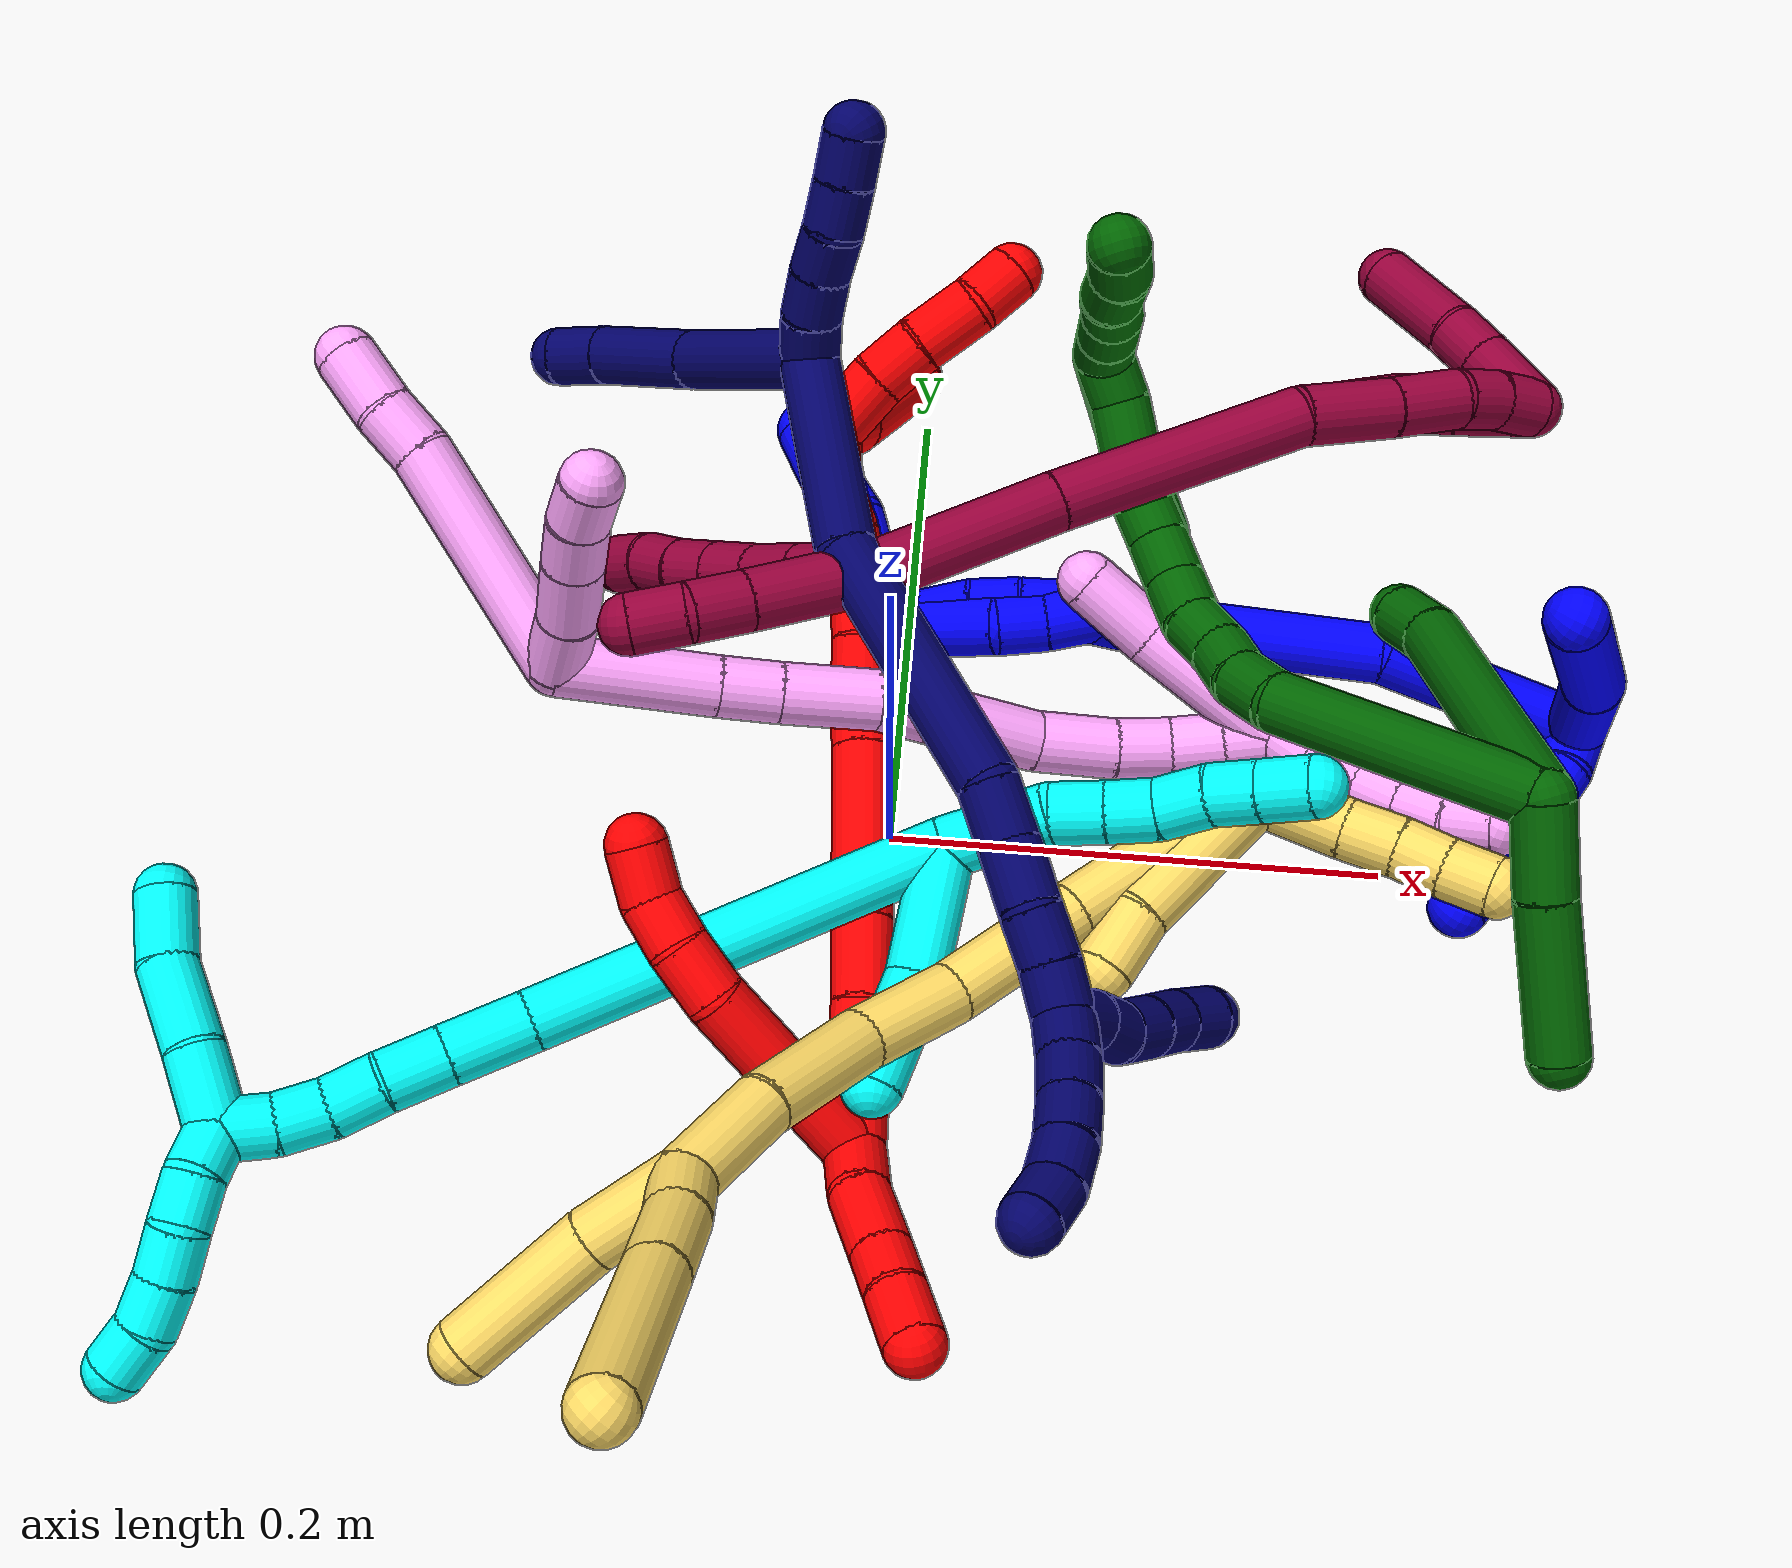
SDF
<sdf version="1.7">
 <world name="default">
  <plugin name="TubeGeneratorPlugin" filename="libtube_generator_plugin.so"/>
  <model name="photoneo_s_sensor">
   <static>1</static>
   <pose>0 0 2 1.57079 1.57079 3.14159</pose>
   <link name="link">
    <inertial><mass>0.1</mass></inertial>
    <sensor name="sensor" type="depth">
     <update_rate>30</update_rate>
     <camera>
      <horizontal_fov>1.22</horizontal_fov>
      <image><width>1920</width><height>1200</height><format>B8G8R8</format></image>
      <clip><near>0.1</near><far>4</far></clip>
      <depth_camera><output>points</output></depth_camera>
     </camera>
     <plugin name="camera_plugin" filename="libgazebo_ros_depth_camera.so">
      <baseline>0.2</baseline>
      <alwaysOn>1</alwaysOn>
      <updateRate>0.0</updateRate>
      <cameraName>camera_ir</cameraName>
      <imageTopicName>/camera/color/image_raw</imageTopicName>
      <cameraInfoTopicName>/camera/color/camera_info</cameraInfoTopicName>
      <depthImageTopicName>/camera/depth/image_raw</depthImageTopicName>
      <depthImageCameraInfoTopicName>/camera/depth/camera_info</depthImageCameraInfoTopicName>
      <pointCloudTopicName>/camera/depth/points</pointCloudTopicName>
      <frameName>fr_optical</frameName>
      <pointCloudCutoff>0.1</pointCloudCutoff>
      <pointCloudCutoffMax>2.0</pointCloudCutoffMax>
      <distortionK1>0</distortionK1>
      <distortionK2>0</distortionK2>
      <distortionK3>0</distortionK3>
      <distortionT1>0</distortionT1>
      <distortionT2>0</distortionT2>
      <CxPrime>0</CxPrime>
      <Cx>0</Cx>
      <Cy>0</Cy>
      <focalLength>0</focalLength>
      <hackBaseline>0</hackBaseline>
     </plugin>
    </sensor>
   </link>
  </model>
  <gravity>0 0 -9.8</gravity>
  <magnetic_field>6e-06 2.3e-05 -4.2e-05</magnetic_field>
  <atmosphere type="adiabatic"/>
  <physics name="default_physics" default="0" type="ode">
   <max_step_size>0.003</max_step_size>
   <real_time_factor>1</real_time_factor>
   <real_time_update_rate>1000</real_time_update_rate>
   <max_contacts>10000</max_contacts>
   <ode>
    <solver>
     <type>quick</type>
     <iters>100</iters>
     <sor>1.3</sor>
     <use_dynamic_moi_rescaling>0</use_dynamic_moi_rescaling>
    </solver>
    <constraints>
     <contact_max_correcting_vel>0</contact_max_correcting_vel>
     <contact_surface_layer>0.001</contact_surface_layer>
     <cfm>0</cfm>
     <erp>0.2</erp>
    </constraints>
   </ode>
  </physics>
  <scene><ambient>0.4 0.4 0.4 1</ambient><background>0.7 0.7 0.7 1</background><shadows>0</shadows></scene>
  <audio><device>default</device></audio>
  <spherical_coordinates>
   <surface_model>EARTH_WGS84</surface_model>
   <latitude_deg>0</latitude_deg>
   <longitude_deg>0</longitude_deg>
   <elevation>0</elevation>
   <heading_deg>0</heading_deg>
  </spherical_coordinates>
  <model name="bin">
   <static>1</static>
   <link name="bottom">
    <collision name="collision-bottom">
     <pose>0 0 -0.01 0 -0 0</pose>
     <geometry><box><size>0.8 0.6 0.02</size></box></geometry>
     <surface>
      <friction><ode><mu>100</mu><mu2>100</mu2></ode></friction>
      <contact><collide_bitmask>65535</collide_bitmask></contact>
     </surface>
    </collision>
   </link>
   <link name="west_wall">
    <collision name="collision-west_wall">
     <pose>-0.41 0 0.1 0 -0 0</pose>
     <geometry><box><size>0.02 0.6 0.2</size></box></geometry>
     <surface>
      <friction><ode><mu>100</mu><mu2>100</mu2></ode></friction>
      <contact><collide_bitmask>65535</collide_bitmask></contact>
     </surface>
    </collision>
   </link>
   <link name="east_wall">
    <collision name="collision-east_wall">
     <pose>0.41 0 0.1 0 -0 0</pose>
     <geometry><box><size>0.02 0.6 0.2</size></box></geometry>
     <surface>
      <friction><ode><mu>100</mu><mu2>100</mu2></ode></friction>
      <contact><collide_bitmask>65535</collide_bitmask></contact>
     </surface>
    </collision>
   </link>
   <link name="south_wall">
    <collision name="collision-south_wall">
     <pose>0 -0.31 0.1 0 -0 0</pose>
     <geometry><box><size>0.8 0.02 0.2</size></box></geometry>
     <surface>
      <friction><ode><mu>100</mu><mu2>100</mu2></ode></friction>
      <contact><collide_bitmask>65535</collide_bitmask></contact>
     </surface>
    </collision>
   </link>
   <link name="north_wall">
    <collision name="collision-north_wall">
     <pose>0 0.31 0.1 0 -0 0</pose>
     <geometry><box><size>0.8 0.02 0.2</size></box></geometry>
     <surface>
      <friction><ode><mu>100</mu><mu2>100</mu2></ode></friction>
      <contact><collide_bitmask>65535</collide_bitmask></contact>
     </surface>
    </collision>
   </link>
  </model>
  <model name="1">
   <static>0</static>
   <link name="1">
    <collision name="collision-cylinder-e_1_2_8">
     <pose>0.026634 -0.021279 -0.012299 2.09486 0.825533 1.29837</pose>
     <geometry><cylinder><radius>0.0125</radius><length>0.072483</length></cylinder></geometry>
     <surface>
      <friction><ode><mu>1.16</mu><mu2>1.16</mu2><slip1>0</slip1><slip2>0</slip2></ode></friction>
      <contact><ode><kp>1e+06</kp><kd>1</kd><max_vel>0</max_vel><min_depth>0.001</min_depth></ode></contact>
     </surface>
    </collision>
    <visual name="visual-cylinder-e_1_2_8">
     <pose>0.026634 -0.021279 -0.012299 2.09486 0.825533 1.29837</pose>
     <geometry><cylinder><radius>0.0125</radius><length>0.072483</length></cylinder></geometry>
     <material><ambient>0 0 1 1</ambient></material>
    </visual>
    <collision name="collision-cylinder-e_2_8_6">
     <pose>0.080164 -0.062558 -0.044062 2.34263 0.766929 1.5254</pose>
     <geometry><cylinder><radius>0.0125</radius><length>0.077517</length></cylinder></geometry>
     <surface>
      <friction><ode><mu>1.16</mu><mu2>1.16</mu2><slip1>0</slip1><slip2>0</slip2></ode></friction>
      <contact><ode><kp>1e+06</kp><kd>1</kd><max_vel>0</max_vel><min_depth>0.001</min_depth></ode></contact>
     </surface>
    </collision>
    <visual name="visual-cylinder-e_2_8_6">
     <pose>0.080164 -0.062558 -0.044062 2.34263 0.766929 1.5254</pose>
     <geometry><cylinder><radius>0.0125</radius><length>0.077517</length></cylinder></geometry>
     <material><ambient>0 0 1 1</ambient></material>
    </visual>
    <collision name="collision-cylinder-e_1_2_9">
     <pose>0.008308 0.005526 -0.000657 -1.68917 0.980616 -1.08235</pose>
     <geometry><cylinder><radius>0.0125</radius><length>0.02</length></cylinder></geometry>
     <surface>
      <friction><ode><mu>1.16</mu><mu2>1.16</mu2><slip1>0</slip1><slip2>0</slip2></ode></friction>
      <contact><ode><kp>1e+06</kp><kd>1</kd><max_vel>0</max_vel><min_depth>0.001</min_depth></ode></contact>
     </surface>
    </collision>
    <visual name="visual-cylinder-e_1_2_9">
     <pose>0.008308 0.005526 -0.000657 -1.68917 0.980616 -1.08235</pose>
     <geometry><cylinder><radius>0.0125</radius><length>0.02</length></cylinder></geometry>
     <material><ambient>0 0 1 1</ambient></material>
    </visual>
    <collision name="collision-cylinder-e_2_9_10">
     <pose>0.023541 0.017884 -0.003634 -1.89811 0.76483 -1.023</pose>
     <geometry><cylinder><radius>0.0125</radius><length>0.02</length></cylinder></geometry>
     <surface>
      <friction><ode><mu>1.16</mu><mu2>1.16</mu2><slip1>0</slip1><slip2>0</slip2></ode></friction>
      <contact><ode><kp>1e+06</kp><kd>1</kd><max_vel>0</max_vel><min_depth>0.001</min_depth></ode></contact>
     </surface>
    </collision>
    <visual name="visual-cylinder-e_2_9_10">
     <pose>0.023541 0.017884 -0.003634 -1.89811 0.76483 -1.023</pose>
     <geometry><cylinder><radius>0.0125</radius><length>0.02</length></cylinder></geometry>
     <material><ambient>0 0 1 1</ambient></material>
    </visual>
    <collision name="collision-cylinder-e_3_10_11">
     <pose>0.038088 0.030378 -0.009091 -2.0768 0.866841 -1.33167</pose>
     <geometry><cylinder><radius>0.0125</radius><length>0.02</length></cylinder></geometry>
     <surface>
      <friction><ode><mu>1.16</mu><mu2>1.16</mu2><slip1>0</slip1><slip2>0</slip2></ode></friction>
      <contact><ode><kp>1e+06</kp><kd>1</kd><max_vel>0</max_vel><min_depth>0.001</min_depth></ode></contact>
     </surface>
    </collision>
    <visual name="visual-cylinder-e_3_10_11">
     <pose>0.038088 0.030378 -0.009091 -2.0768 0.866841 -1.33167</pose>
     <geometry><cylinder><radius>0.0125</radius><length>0.02</length></cylinder></geometry>
     <material><ambient>0 0 1 1</ambient></material>
    </visual>
    <collision name="collision-cylinder-e_4_11_12">
     <pose>0.053344 0.041622 -0.015477 -2.09779 0.868477 -1.35728</pose>
     <geometry><cylinder><radius>0.0125</radius><length>0.02</length></cylinder></geometry>
     <surface>
      <friction><ode><mu>1.16</mu><mu2>1.16</mu2><slip1>0</slip1><slip2>0</slip2></ode></friction>
      <contact><ode><kp>1e+06</kp><kd>1</kd><max_vel>0</max_vel><min_depth>0.001</min_depth></ode></contact>
     </surface>
    </collision>
    <visual name="visual-cylinder-e_4_11_12">
     <pose>0.053344 0.041622 -0.015477 -2.09779 0.868477 -1.35728</pose>
     <geometry><cylinder><radius>0.0125</radius><length>0.02</length></cylinder></geometry>
     <material><ambient>0 0 1 1</ambient></material>
    </visual>
    <collision name="collision-cylinder-e_5_12_5">
     <pose>0.067535 0.054055 -0.021903 -2.00517 0.715116 -1.05893</pose>
     <geometry><cylinder><radius>0.0125</radius><length>0.02</length></cylinder></geometry>
     <surface>
      <friction><ode><mu>1.16</mu><mu2>1.16</mu2><slip1>0</slip1><slip2>0</slip2></ode></friction>
      <contact><ode><kp>1e+06</kp><kd>1</kd><max_vel>0</max_vel><min_depth>0.001</min_depth></ode></contact>
     </surface>
    </collision>
    <visual name="visual-cylinder-e_5_12_5">
     <pose>0.067535 0.054055 -0.021903 -2.00517 0.715116 -1.05893</pose>
     <geometry><cylinder><radius>0.0125</radius><length>0.02</length></cylinder></geometry>
     <material><ambient>0 0 1 1</ambient></material>
    </visual>
    <collision name="collision-cylinder-e_1_2_13">
     <pose>0.000186 0.003854 -0.043642 -3.0535 0.004255 -0.096465</pose>
     <geometry><cylinder><radius>0.0125</radius><length>0.087624</length></cylinder></geometry>
     <surface>
      <friction><ode><mu>1.16</mu><mu2>1.16</mu2><slip1>0</slip1><slip2>0</slip2></ode></friction>
      <contact><ode><kp>1e+06</kp><kd>1</kd><max_vel>0</max_vel><min_depth>0.001</min_depth></ode></contact>
     </surface>
    </collision>
    <visual name="visual-cylinder-e_1_2_13">
     <pose>0.000186 0.003854 -0.043642 -3.0535 0.004255 -0.096465</pose>
     <geometry><cylinder><radius>0.0125</radius><length>0.087624</length></cylinder></geometry>
     <material><ambient>0 0 1 1</ambient></material>
    </visual>
    <collision name="collision-cylinder-e_2_13_14">
     <pose>-0.004652 0.028697 -0.135924 -2.73423 -0.09457 0.450437</pose>
     <geometry><cylinder><radius>0.0125</radius><length>0.106427</length></cylinder></geometry>
     <surface>
      <friction><ode><mu>1.16</mu><mu2>1.16</mu2><slip1>0</slip1><slip2>0</slip2></ode></friction>
      <contact><ode><kp>1e+06</kp><kd>1</kd><max_vel>0</max_vel><min_depth>0.001</min_depth></ode></contact>
     </surface>
    </collision>
    <visual name="visual-cylinder-e_2_13_14">
     <pose>-0.004652 0.028697 -0.135924 -2.73423 -0.09457 0.450437</pose>
     <geometry><cylinder><radius>0.0125</radius><length>0.106427</length></cylinder></geometry>
     <material><ambient>0 0 1 1</ambient></material>
    </visual>
    <collision name="collision-cylinder-e_3_14_15">
     <pose>-0.012417 0.053967 -0.19534 -2.76334 -0.232073 1.09394</pose>
     <geometry><cylinder><radius>0.0125</radius><length>0.023828</length></cylinder></geometry>
     <surface>
      <friction><ode><mu>1.16</mu><mu2>1.16</mu2><slip1>0</slip1><slip2>0</slip2></ode></friction>
      <contact><ode><kp>1e+06</kp><kd>1</kd><max_vel>0</max_vel><min_depth>0.001</min_depth></ode></contact>
     </surface>
    </collision>
    <visual name="visual-cylinder-e_3_14_15">
     <pose>-0.012417 0.053967 -0.19534 -2.76334 -0.232073 1.09394</pose>
     <geometry><cylinder><radius>0.0125</radius><length>0.023828</length></cylinder></geometry>
     <material><ambient>0 0 1 1</ambient></material>
    </visual>
    <collision name="collision-cylinder-e_4_15_16">
     <pose>-0.015026 0.062614 -0.215735 -2.71562 0.0124 -0.05732</pose>
     <geometry><cylinder><radius>0.0125</radius><length>0.021129</length></cylinder></geometry>
     <surface>
      <friction><ode><mu>1.16</mu><mu2>1.16</mu2><slip1>0</slip1><slip2>0</slip2></ode></friction>
      <contact><ode><kp>1e+06</kp><kd>1</kd><max_vel>0</max_vel><min_depth>0.001</min_depth></ode></contact>
     </surface>
    </collision>
    <visual name="visual-cylinder-e_4_15_16">
     <pose>-0.015026 0.062614 -0.215735 -2.71562 0.0124 -0.05732</pose>
     <geometry><cylinder><radius>0.0125</radius><length>0.021129</length></cylinder></geometry>
     <material><ambient>0 0 1 1</ambient></material>
    </visual>
    <collision name="collision-cylinder-e_5_16_17">
     <pose>-0.015094 0.072252 -0.233978 -2.59281 -0.019628 0.069705</pose>
     <geometry><cylinder><radius>0.0125</radius><length>0.020219</length></cylinder></geometry>
     <surface>
      <friction><ode><mu>1.16</mu><mu2>1.16</mu2><slip1>0</slip1><slip2>0</slip2></ode></friction>
      <contact><ode><kp>1e+06</kp><kd>1</kd><max_vel>0</max_vel><min_depth>0.001</min_depth></ode></contact>
     </surface>
    </collision>
    <visual name="visual-cylinder-e_5_16_17">
     <pose>-0.015094 0.072252 -0.233978 -2.59281 -0.019628 0.069705</pose>
     <geometry><cylinder><radius>0.0125</radius><length>0.020219</length></cylinder></geometry>
     <material><ambient>0 0 1 1</ambient></material>
    </visual>
    <collision name="collision-cylinder-e_6_17_18">
     <pose>-0.014743 0.084284 -0.250446 -2.43032 0.052941 -0.142325</pose>
     <geometry><cylinder><radius>0.0125</radius><length>0.020739</length></cylinder></geometry>
     <surface>
      <friction><ode><mu>1.16</mu><mu2>1.16</mu2><slip1>0</slip1><slip2>0</slip2></ode></friction>
      <contact><ode><kp>1e+06</kp><kd>1</kd><max_vel>0</max_vel><min_depth>0.001</min_depth></ode></contact>
     </surface>
    </collision>
    <visual name="visual-cylinder-e_6_17_18">
     <pose>-0.014743 0.084284 -0.250446 -2.43032 0.052941 -0.142325</pose>
     <geometry><cylinder><radius>0.0125</radius><length>0.020739</length></cylinder></geometry>
     <material><ambient>0 0 1 1</ambient></material>
    </visual>
    <collision name="collision-cylinder-e_7_18_1">
     <pose>-0.013457 0.097325 -0.266058 -2.46156 0.073677 -0.207617</pose>
     <geometry><cylinder><radius>0.0125</radius><length>0.020033</length></cylinder></geometry>
     <surface>
      <friction><ode><mu>1.16</mu><mu2>1.16</mu2><slip1>0</slip1><slip2>0</slip2></ode></friction>
      <contact><ode><kp>1e+06</kp><kd>1</kd><max_vel>0</max_vel><min_depth>0.001</min_depth></ode></contact>
     </surface>
    </collision>
    <visual name="visual-cylinder-e_7_18_1">
     <pose>-0.013457 0.097325 -0.266058 -2.46156 0.073677 -0.207617</pose>
     <geometry><cylinder><radius>0.0125</radius><length>0.020033</length></cylinder></geometry>
     <material><ambient>0 0 1 1</ambient></material>
    </visual>
    <collision name="collision-cylinder-e_1_1_19">
     <pose>-0.018576 0.096173 -0.279589 2.23038 -0.55681 -1.05615</pose>
     <geometry><cylinder><radius>0.0125</radius><length>0.02216</length></cylinder></geometry>
     <surface>
      <friction><ode><mu>1.16</mu><mu2>1.16</mu2><slip1>0</slip1><slip2>0</slip2></ode></friction>
      <contact><ode><kp>1e+06</kp><kd>1</kd><max_vel>0</max_vel><min_depth>0.001</min_depth></ode></contact>
     </surface>
    </collision>
    <visual name="visual-cylinder-e_1_1_19">
     <pose>-0.018576 0.096173 -0.279589 2.23038 -0.55681 -1.05615</pose>
     <geometry><cylinder><radius>0.0125</radius><length>0.02216</length></cylinder></geometry>
     <material><ambient>0 0 1 1</ambient></material>
    </visual>
    <collision name="collision-cylinder-e_2_19_20">
     <pose>-0.034488 0.082728 -0.293251 2.49096 -0.791958 -1.78382</pose>
     <geometry><cylinder><radius>0.0125</radius><length>0.028259</length></cylinder></geometry>
     <surface>
      <friction><ode><mu>1.16</mu><mu2>1.16</mu2><slip1>0</slip1><slip2>0</slip2></ode></friction>
      <contact><ode><kp>1e+06</kp><kd>1</kd><max_vel>0</max_vel><min_depth>0.001</min_depth></ode></contact>
     </surface>
    </collision>
    <visual name="visual-cylinder-e_2_19_20">
     <pose>-0.034488 0.082728 -0.293251 2.49096 -0.791958 -1.78382</pose>
     <geometry><cylinder><radius>0.0125</radius><length>0.028259</length></cylinder></geometry>
     <material><ambient>0 0 1 1</ambient></material>
    </visual>
    <collision name="collision-cylinder-e_3_20_21">
     <pose>-0.053994 0.074684 -0.309989 2.91566 -0.805814 -2.62132</pose>
     <geometry><cylinder><radius>0.0125</radius><length>0.026199</length></cylinder></geometry>
     <surface>
      <friction><ode><mu>1.16</mu><mu2>1.16</mu2><slip1>0</slip1><slip2>0</slip2></ode></friction>
      <contact><ode><kp>1e+06</kp><kd>1</kd><max_vel>0</max_vel><min_depth>0.001</min_depth></ode></contact>
     </surface>
    </collision>
    <visual name="visual-cylinder-e_3_20_21">
     <pose>-0.053994 0.074684 -0.309989 2.91566 -0.805814 -2.62132</pose>
     <geometry><cylinder><radius>0.0125</radius><length>0.026199</length></cylinder></geometry>
     <material><ambient>0 0 1 1</ambient></material>
    </visual>
    <collision name="collision-cylinder-e_4_21_4">
     <pose>-0.071789 0.069436 -0.32636 2.73793 -0.794909 -2.23452</pose>
     <geometry><cylinder><radius>0.0125</radius><length>0.023382</length></cylinder></geometry>
     <surface>
      <friction><ode><mu>1.16</mu><mu2>1.16</mu2><slip1>0</slip1><slip2>0</slip2></ode></friction>
      <contact><ode><kp>1e+06</kp><kd>1</kd><max_vel>0</max_vel><min_depth>0.001</min_depth></ode></contact>
     </surface>
    </collision>
    <visual name="visual-cylinder-e_4_21_4">
     <pose>-0.071789 0.069436 -0.32636 2.73793 -0.794909 -2.23452</pose>
     <geometry><cylinder><radius>0.0125</radius><length>0.023382</length></cylinder></geometry>
     <material><ambient>0 0 1 1</ambient></material>
    </visual>
    <collision name="collision-cylinder-e_1_1_22">
     <pose>-0.008502 0.089296 -0.252895 0.599736 0.164841 0.051072</pose>
     <geometry><cylinder><radius>0.0125</radius><length>0.051407</length></cylinder></geometry>
     <surface>
      <friction><ode><mu>1.16</mu><mu2>1.16</mu2><slip1>0</slip1><slip2>0</slip2></ode></friction>
      <contact><ode><kp>1e+06</kp><kd>1</kd><max_vel>0</max_vel><min_depth>0.001</min_depth></ode></contact>
     </surface>
    </collision>
    <visual name="visual-cylinder-e_1_1_22">
     <pose>-0.008502 0.089296 -0.252895 0.599736 0.164841 0.051072</pose>
     <geometry><cylinder><radius>0.0125</radius><length>0.051407</length></cylinder></geometry>
     <material><ambient>0 0 1 1</ambient></material>
    </visual>
    <collision name="collision-cylinder-e_2_22_23">
     <pose>-0.006043 0.06987 -0.222932 0.515216 -0.167875 -0.044326</pose>
     <geometry><cylinder><radius>0.0125</radius><length>0.021055</length></cylinder></geometry>
     <surface>
      <friction><ode><mu>1.16</mu><mu2>1.16</mu2><slip1>0</slip1><slip2>0</slip2></ode></friction>
      <contact><ode><kp>1e+06</kp><kd>1</kd><max_vel>0</max_vel><min_depth>0.001</min_depth></ode></contact>
     </surface>
    </collision>
    <visual name="visual-cylinder-e_2_22_23">
     <pose>-0.006043 0.06987 -0.222932 0.515216 -0.167875 -0.044326</pose>
     <geometry><cylinder><radius>0.0125</radius><length>0.021055</length></cylinder></geometry>
     <material><ambient>0 0 1 1</ambient></material>
    </visual>
    <collision name="collision-cylinder-e_3_23_3">
     <pose>-0.009082 0.056183 -0.203202 0.675555 -0.09304 -0.0327</pose>
     <geometry><cylinder><radius>0.0125</radius><length>0.027538</length></cylinder></geometry>
     <surface>
      <friction><ode><mu>1.16</mu><mu2>1.16</mu2><slip1>0</slip1><slip2>0</slip2></ode></friction>
      <contact><ode><kp>1e+06</kp><kd>1</kd><max_vel>0</max_vel><min_depth>0.001</min_depth></ode></contact>
     </surface>
    </collision>
    <visual name="visual-cylinder-e_3_23_3">
     <pose>-0.009082 0.056183 -0.203202 0.675555 -0.09304 -0.0327</pose>
     <geometry><cylinder><radius>0.0125</radius><length>0.027538</length></cylinder></geometry>
     <material><ambient>0 0 1 1</ambient></material>
    </visual>
    <collision name="collision-sphere-3">
     <pose>-0.010361 0.04761 -0.192504 0 -0 0</pose>
     <geometry><sphere><radius>0.0125</radius></sphere></geometry>
     <surface>
      <friction><ode><mu>1.16</mu><mu2>1.16</mu2><slip1>0</slip1><slip2>0</slip2></ode></friction>
      <contact><ode><kp>1e+06</kp><kd>1</kd><max_vel>0</max_vel><min_depth>0.001</min_depth></ode></contact>
     </surface>
    </collision>
    <visual name="visual-sphere-3">
     <pose>-0.010361 0.04761 -0.192504 0 -0 0</pose>
     <geometry><sphere><radius>0.0125</radius></sphere></geometry>
     <material><ambient>0 0 1 1</ambient></material>
    </visual>
    <collision name="collision-sphere-23">
     <pose>-0.007802 0.064756 -0.2139 0 -0 0</pose>
     <geometry><sphere><radius>0.0125</radius></sphere></geometry>
     <surface>
      <friction><ode><mu>1.16</mu><mu2>1.16</mu2><slip1>0</slip1><slip2>0</slip2></ode></friction>
      <contact><ode><kp>1e+06</kp><kd>1</kd><max_vel>0</max_vel><min_depth>0.001</min_depth></ode></contact>
     </surface>
    </collision>
    <visual name="visual-sphere-23">
     <pose>-0.007802 0.064756 -0.2139 0 -0 0</pose>
     <geometry><sphere><radius>0.0125</radius></sphere></geometry>
     <material><ambient>0 0 1 1</ambient></material>
    </visual>
    <collision name="collision-sphere-22">
     <pose>-0.004284 0.074985 -0.231964 0 -0 0</pose>
     <geometry><sphere><radius>0.0125</radius></sphere></geometry>
     <surface>
      <friction><ode><mu>1.16</mu><mu2>1.16</mu2><slip1>0</slip1><slip2>0</slip2></ode></friction>
      <contact><ode><kp>1e+06</kp><kd>1</kd><max_vel>0</max_vel><min_depth>0.001</min_depth></ode></contact>
     </surface>
    </collision>
    <visual name="visual-sphere-22">
     <pose>-0.004284 0.074985 -0.231964 0 -0 0</pose>
     <geometry><sphere><radius>0.0125</radius></sphere></geometry>
     <material><ambient>0 0 1 1</ambient></material>
    </visual>
    <collision name="collision-sphere-4">
     <pose>-0.080134 0.06622 -0.33389 0 -0 0</pose>
     <geometry><sphere><radius>0.0125</radius></sphere></geometry>
     <surface>
      <friction><ode><mu>1.16</mu><mu2>1.16</mu2><slip1>0</slip1><slip2>0</slip2></ode></friction>
      <contact><ode><kp>1e+06</kp><kd>1</kd><max_vel>0</max_vel><min_depth>0.001</min_depth></ode></contact>
     </surface>
    </collision>
    <visual name="visual-sphere-4">
     <pose>-0.080134 0.06622 -0.33389 0 -0 0</pose>
     <geometry><sphere><radius>0.0125</radius></sphere></geometry>
     <material><ambient>0 0 1 1</ambient></material>
    </visual>
    <collision name="collision-sphere-21">
     <pose>-0.063444 0.072652 -0.318831 0 -0 0</pose>
     <geometry><sphere><radius>0.0125</radius></sphere></geometry>
     <surface>
      <friction><ode><mu>1.16</mu><mu2>1.16</mu2><slip1>0</slip1><slip2>0</slip2></ode></friction>
      <contact><ode><kp>1e+06</kp><kd>1</kd><max_vel>0</max_vel><min_depth>0.001</min_depth></ode></contact>
     </surface>
    </collision>
    <visual name="visual-sphere-21">
     <pose>-0.063444 0.072652 -0.318831 0 -0 0</pose>
     <geometry><sphere><radius>0.0125</radius></sphere></geometry>
     <material><ambient>0 0 1 1</ambient></material>
    </visual>
    <collision name="collision-sphere-20">
     <pose>-0.044544 0.076717 -0.301148 0 -0 0</pose>
     <geometry><sphere><radius>0.0125</radius></sphere></geometry>
     <surface>
      <friction><ode><mu>1.16</mu><mu2>1.16</mu2><slip1>0</slip1><slip2>0</slip2></ode></friction>
      <contact><ode><kp>1e+06</kp><kd>1</kd><max_vel>0</max_vel><min_depth>0.001</min_depth></ode></contact>
     </surface>
    </collision>
    <visual name="visual-sphere-20">
     <pose>-0.044544 0.076717 -0.301148 0 -0 0</pose>
     <geometry><sphere><radius>0.0125</radius></sphere></geometry>
     <material><ambient>0 0 1 1</ambient></material>
    </visual>
    <collision name="collision-sphere-11">
     <pose>0.045711 0.036039 -0.012228 0 -0 0</pose>
     <geometry><sphere><radius>0.0125</radius></sphere></geometry>
     <surface>
      <friction><ode><mu>1.16</mu><mu2>1.16</mu2><slip1>0</slip1><slip2>0</slip2></ode></friction>
      <contact><ode><kp>1e+06</kp><kd>1</kd><max_vel>0</max_vel><min_depth>0.001</min_depth></ode></contact>
     </surface>
    </collision>
    <visual name="visual-sphere-11">
     <pose>0.045711 0.036039 -0.012228 0 -0 0</pose>
     <geometry><sphere><radius>0.0125</radius></sphere></geometry>
     <material><ambient>0 0 1 1</ambient></material>
    </visual>
    <collision name="collision-sphere-10">
     <pose>0.030465 0.024716 -0.005954 0 -0 0</pose>
     <geometry><sphere><radius>0.0125</radius></sphere></geometry>
     <surface>
      <friction><ode><mu>1.16</mu><mu2>1.16</mu2><slip1>0</slip1><slip2>0</slip2></ode></friction>
      <contact><ode><kp>1e+06</kp><kd>1</kd><max_vel>0</max_vel><min_depth>0.001</min_depth></ode></contact>
     </surface>
    </collision>
    <visual name="visual-sphere-10">
     <pose>0.030465 0.024716 -0.005954 0 -0 0</pose>
     <geometry><sphere><radius>0.0125</radius></sphere></geometry>
     <material><ambient>0 0 1 1</ambient></material>
    </visual>
    <collision name="collision-sphere-6">
     <pose>0.10706 -0.082558 -0.063527 0 -0 0</pose>
     <geometry><sphere><radius>0.0125</radius></sphere></geometry>
     <surface>
      <friction><ode><mu>1.16</mu><mu2>1.16</mu2><slip1>0</slip1><slip2>0</slip2></ode></friction>
      <contact><ode><kp>1e+06</kp><kd>1</kd><max_vel>0</max_vel><min_depth>0.001</min_depth></ode></contact>
     </surface>
    </collision>
    <visual name="visual-sphere-6">
     <pose>0.10706 -0.082558 -0.063527 0 -0 0</pose>
     <geometry><sphere><radius>0.0125</radius></sphere></geometry>
     <material><ambient>0 0 1 1</ambient></material>
    </visual>
    <collision name="collision-sphere-9">
     <pose>0.016617 0.011052 -0.001314 0 -0 0</pose>
     <geometry><sphere><radius>0.0125</radius></sphere></geometry>
     <surface>
      <friction><ode><mu>1.16</mu><mu2>1.16</mu2><slip1>0</slip1><slip2>0</slip2></ode></friction>
      <contact><ode><kp>1e+06</kp><kd>1</kd><max_vel>0</max_vel><min_depth>0.001</min_depth></ode></contact>
     </surface>
    </collision>
    <visual name="visual-sphere-9">
     <pose>0.016617 0.011052 -0.001314 0 -0 0</pose>
     <geometry><sphere><radius>0.0125</radius></sphere></geometry>
     <material><ambient>0 0 1 1</ambient></material>
    </visual>
    <collision name="collision-sphere-2">
     <geometry><sphere><radius>0.0125</radius></sphere></geometry>
     <surface>
      <friction><ode><mu>1.16</mu><mu2>1.16</mu2><slip1>0</slip1><slip2>0</slip2></ode></friction>
      <contact><ode><kp>1e+06</kp><kd>1</kd><max_vel>0</max_vel><min_depth>0.001</min_depth></ode></contact>
     </surface>
    </collision>
    <visual name="visual-sphere-2">
     <geometry><sphere><radius>0.0125</radius></sphere></geometry>
     <material><ambient>0 0 1 1</ambient></material>
    </visual>
    <collision name="collision-sphere-19">
     <pose>-0.024431 0.08874 -0.285353 0 -0 0</pose>
     <geometry><sphere><radius>0.0125</radius></sphere></geometry>
     <surface>
      <friction><ode><mu>1.16</mu><mu2>1.16</mu2><slip1>0</slip1><slip2>0</slip2></ode></friction>
      <contact><ode><kp>1e+06</kp><kd>1</kd><max_vel>0</max_vel><min_depth>0.001</min_depth></ode></contact>
     </surface>
    </collision>
    <visual name="visual-sphere-19">
     <pose>-0.024431 0.08874 -0.285353 0 -0 0</pose>
     <geometry><sphere><radius>0.0125</radius></sphere></geometry>
     <material><ambient>0 0 1 1</ambient></material>
    </visual>
    <collision name="collision-sphere-8">
     <pose>0.053268 -0.042558 -0.024598 0 -0 0</pose>
     <geometry><sphere><radius>0.0125</radius></sphere></geometry>
     <surface>
      <friction><ode><mu>1.16</mu><mu2>1.16</mu2><slip1>0</slip1><slip2>0</slip2></ode></friction>
      <contact><ode><kp>1e+06</kp><kd>1</kd><max_vel>0</max_vel><min_depth>0.001</min_depth></ode></contact>
     </surface>
    </collision>
    <visual name="visual-sphere-8">
     <pose>0.053268 -0.042558 -0.024598 0 -0 0</pose>
     <geometry><sphere><radius>0.0125</radius></sphere></geometry>
     <material><ambient>0 0 1 1</ambient></material>
    </visual>
    <collision name="collision-sphere-12">
     <pose>0.060978 0.047206 -0.018726 0 -0 0</pose>
     <geometry><sphere><radius>0.0125</radius></sphere></geometry>
     <surface>
      <friction><ode><mu>1.16</mu><mu2>1.16</mu2><slip1>0</slip1><slip2>0</slip2></ode></friction>
      <contact><ode><kp>1e+06</kp><kd>1</kd><max_vel>0</max_vel><min_depth>0.001</min_depth></ode></contact>
     </surface>
    </collision>
    <visual name="visual-sphere-12">
     <pose>0.060978 0.047206 -0.018726 0 -0 0</pose>
     <geometry><sphere><radius>0.0125</radius></sphere></geometry>
     <material><ambient>0 0 1 1</ambient></material>
    </visual>
    <collision name="collision-sphere-5">
     <pose>0.074092 0.060904 -0.025081 0 -0 0</pose>
     <geometry><sphere><radius>0.0125</radius></sphere></geometry>
     <surface>
      <friction><ode><mu>1.16</mu><mu2>1.16</mu2><slip1>0</slip1><slip2>0</slip2></ode></friction>
      <contact><ode><kp>1e+06</kp><kd>1</kd><max_vel>0</max_vel><min_depth>0.001</min_depth></ode></contact>
     </surface>
    </collision>
    <visual name="visual-sphere-5">
     <pose>0.074092 0.060904 -0.025081 0 -0 0</pose>
     <geometry><sphere><radius>0.0125</radius></sphere></geometry>
     <material><ambient>0 0 1 1</ambient></material>
    </visual>
    <collision name="collision-sphere-13">
     <pose>0.000373 0.007709 -0.087283 0 -0 0</pose>
     <geometry><sphere><radius>0.0125</radius></sphere></geometry>
     <surface>
      <friction><ode><mu>1.16</mu><mu2>1.16</mu2><slip1>0</slip1><slip2>0</slip2></ode></friction>
      <contact><ode><kp>1e+06</kp><kd>1</kd><max_vel>0</max_vel><min_depth>0.001</min_depth></ode></contact>
     </surface>
    </collision>
    <visual name="visual-sphere-13">
     <pose>0.000373 0.007709 -0.087283 0 -0 0</pose>
     <geometry><sphere><radius>0.0125</radius></sphere></geometry>
     <material><ambient>0 0 1 1</ambient></material>
    </visual>
    <collision name="collision-sphere-14">
     <pose>-0.009677 0.049685 -0.184565 0 -0 0</pose>
     <geometry><sphere><radius>0.0125</radius></sphere></geometry>
     <surface>
      <friction><ode><mu>1.16</mu><mu2>1.16</mu2><slip1>0</slip1><slip2>0</slip2></ode></friction>
      <contact><ode><kp>1e+06</kp><kd>1</kd><max_vel>0</max_vel><min_depth>0.001</min_depth></ode></contact>
     </surface>
    </collision>
    <visual name="visual-sphere-14">
     <pose>-0.009677 0.049685 -0.184565 0 -0 0</pose>
     <geometry><sphere><radius>0.0125</radius></sphere></geometry>
     <material><ambient>0 0 1 1</ambient></material>
    </visual>
    <collision name="collision-sphere-15">
     <pose>-0.015157 0.058249 -0.206115 0 -0 0</pose>
     <geometry><sphere><radius>0.0125</radius></sphere></geometry>
     <surface>
      <friction><ode><mu>1.16</mu><mu2>1.16</mu2><slip1>0</slip1><slip2>0</slip2></ode></friction>
      <contact><ode><kp>1e+06</kp><kd>1</kd><max_vel>0</max_vel><min_depth>0.001</min_depth></ode></contact>
     </surface>
    </collision>
    <visual name="visual-sphere-15">
     <pose>-0.015157 0.058249 -0.206115 0 -0 0</pose>
     <geometry><sphere><radius>0.0125</radius></sphere></geometry>
     <material><ambient>0 0 1 1</ambient></material>
    </visual>
    <collision name="collision-sphere-16">
     <pose>-0.014895 0.066979 -0.225355 0 -0 0</pose>
     <geometry><sphere><radius>0.0125</radius></sphere></geometry>
     <surface>
      <friction><ode><mu>1.16</mu><mu2>1.16</mu2><slip1>0</slip1><slip2>0</slip2></ode></friction>
      <contact><ode><kp>1e+06</kp><kd>1</kd><max_vel>0</max_vel><min_depth>0.001</min_depth></ode></contact>
     </surface>
    </collision>
    <visual name="visual-sphere-16">
     <pose>-0.014895 0.066979 -0.225355 0 -0 0</pose>
     <geometry><sphere><radius>0.0125</radius></sphere></geometry>
     <material><ambient>0 0 1 1</ambient></material>
    </visual>
    <collision name="collision-sphere-17">
     <pose>-0.015292 0.077524 -0.242602 0 -0 0</pose>
     <geometry><sphere><radius>0.0125</radius></sphere></geometry>
     <surface>
      <friction><ode><mu>1.16</mu><mu2>1.16</mu2><slip1>0</slip1><slip2>0</slip2></ode></friction>
      <contact><ode><kp>1e+06</kp><kd>1</kd><max_vel>0</max_vel><min_depth>0.001</min_depth></ode></contact>
     </surface>
    </collision>
    <visual name="visual-sphere-17">
     <pose>-0.015292 0.077524 -0.242602 0 -0 0</pose>
     <geometry><sphere><radius>0.0125</radius></sphere></geometry>
     <material><ambient>0 0 1 1</ambient></material>
    </visual>
    <collision name="collision-sphere-18">
     <pose>-0.014195 0.091044 -0.25829 0 -0 0</pose>
     <geometry><sphere><radius>0.0125</radius></sphere></geometry>
     <surface>
      <friction><ode><mu>1.16</mu><mu2>1.16</mu2><slip1>0</slip1><slip2>0</slip2></ode></friction>
      <contact><ode><kp>1e+06</kp><kd>1</kd><max_vel>0</max_vel><min_depth>0.001</min_depth></ode></contact>
     </surface>
    </collision>
    <visual name="visual-sphere-18">
     <pose>-0.014195 0.091044 -0.25829 0 -0 0</pose>
     <geometry><sphere><radius>0.0125</radius></sphere></geometry>
     <material><ambient>0 0 1 1</ambient></material>
    </visual>
    <collision name="collision-sphere-1">
     <pose>-0.01272 0.103607 -0.273825 0 -0 0</pose>
     <geometry><sphere><radius>0.0125</radius></sphere></geometry>
     <surface>
      <friction><ode><mu>1.16</mu><mu2>1.16</mu2><slip1>0</slip1><slip2>0</slip2></ode></friction>
      <contact><ode><kp>1e+06</kp><kd>1</kd><max_vel>0</max_vel><min_depth>0.001</min_depth></ode></contact>
     </surface>
    </collision>
    <visual name="visual-sphere-1">
     <pose>-0.01272 0.103607 -0.273825 0 -0 0</pose>
     <geometry><sphere><radius>0.0125</radius></sphere></geometry>
     <material><ambient>0 0 1 1</ambient></material>
    </visual>
    <inertial>
     <pose>0.006259 0.03122 -0.135474 0 -0 0</pose>
     <mass>0.75</mass>
     <inertia><ixx>0.000277</ixx><ixy>0</ixy><ixz>0</ixz><iyy>-6e-06</iyy><iyz>0</iyz><izz>-7.2e-05</izz></inertia>
    </inertial>
   </link>
   <pose>0.279304 0.068497 0.011523 -1.96202 -0.598567 -1.60006</pose>
  </model>
  <model name="2">
   <static>0</static>
   <link name="2">
    <collision name="collision-cylinder-e_1_2_8">
     <pose>-0.021645 -0.002136 0.035648 0.05984 -0.544892 -0.016723</pose>
     <geometry><cylinder><radius>0.0125</radius><length>0.083518</length></cylinder></geometry>
     <surface>
      <friction><ode><mu>1.16</mu><mu2>1.16</mu2><slip1>0</slip1><slip2>0</slip2></ode></friction>
      <contact><ode><kp>1e+06</kp><kd>1</kd><max_vel>0</max_vel><min_depth>0.001</min_depth></ode></contact>
     </surface>
    </collision>
    <visual name="visual-cylinder-e_1_2_8">
     <pose>-0.021645 -0.002136 0.035648 0.05984 -0.544892 -0.016723</pose>
     <geometry><cylinder><radius>0.0125</radius><length>0.083518</length></cylinder></geometry>
     <material><ambient>1 0 0 1</ambient></material>
    </visual>
    <collision name="collision-cylinder-e_2_8_9">
     <pose>-0.050026 -0.001764 0.080783 -0.258385 -0.601605 0.08056</pose>
     <geometry><cylinder><radius>0.0125</radius><length>0.023805</length></cylinder></geometry>
     <surface>
      <friction><ode><mu>1.16</mu><mu2>1.16</mu2><slip1>0</slip1><slip2>0</slip2></ode></friction>
      <contact><ode><kp>1e+06</kp><kd>1</kd><max_vel>0</max_vel><min_depth>0.001</min_depth></ode></contact>
     </surface>
    </collision>
    <visual name="visual-cylinder-e_2_8_9">
     <pose>-0.050026 -0.001764 0.080783 -0.258385 -0.601605 0.08056</pose>
     <geometry><cylinder><radius>0.0125</radius><length>0.023805</length></cylinder></geometry>
     <material><ambient>1 0 0 1</ambient></material>
    </visual>
    <collision name="collision-cylinder-e_3_9_10">
     <pose>-0.062545 0.004807 0.097766 -0.496737 -0.595877 0.155439</pose>
     <geometry><cylinder><radius>0.0125</radius><length>0.020605</length></cylinder></geometry>
     <surface>
      <friction><ode><mu>1.16</mu><mu2>1.16</mu2><slip1>0</slip1><slip2>0</slip2></ode></friction>
      <contact><ode><kp>1e+06</kp><kd>1</kd><max_vel>0</max_vel><min_depth>0.001</min_depth></ode></contact>
     </surface>
    </collision>
    <visual name="visual-cylinder-e_3_9_10">
     <pose>-0.062545 0.004807 0.097766 -0.496737 -0.595877 0.155439</pose>
     <geometry><cylinder><radius>0.0125</radius><length>0.020605</length></cylinder></geometry>
     <material><ambient>1 0 0 1</ambient></material>
    </visual>
    <collision name="collision-cylinder-e_4_10_6">
     <pose>-0.071147 0.013019 0.115092 -0.399385 -0.258442 0.052587</pose>
     <geometry><cylinder><radius>0.0125</radius><length>0.022072</length></cylinder></geometry>
     <surface>
      <friction><ode><mu>1.16</mu><mu2>1.16</mu2><slip1>0</slip1><slip2>0</slip2></ode></friction>
      <contact><ode><kp>1e+06</kp><kd>1</kd><max_vel>0</max_vel><min_depth>0.001</min_depth></ode></contact>
     </surface>
    </collision>
    <visual name="visual-cylinder-e_4_10_6">
     <pose>-0.071147 0.013019 0.115092 -0.399385 -0.258442 0.052587</pose>
     <geometry><cylinder><radius>0.0125</radius><length>0.022072</length></cylinder></geometry>
     <material><ambient>1 0 0 1</ambient></material>
    </visual>
    <collision name="collision-cylinder-e_1_2_11">
     <pose>0.004972 -0.011969 -0.001146 1.66623 0.392115 0.430293</pose>
     <geometry><cylinder><radius>0.0125</radius><length>0.026021</length></cylinder></geometry>
     <surface>
      <friction><ode><mu>1.16</mu><mu2>1.16</mu2><slip1>0</slip1><slip2>0</slip2></ode></friction>
      <contact><ode><kp>1e+06</kp><kd>1</kd><max_vel>0</max_vel><min_depth>0.001</min_depth></ode></contact>
     </surface>
    </collision>
    <visual name="visual-cylinder-e_1_2_11">
     <pose>0.004972 -0.011969 -0.001146 1.66623 0.392115 0.430293</pose>
     <geometry><cylinder><radius>0.0125</radius><length>0.026021</length></cylinder></geometry>
     <material><ambient>1 0 0 1</ambient></material>
    </visual>
    <collision name="collision-cylinder-e_2_11_12">
     <pose>0.018027 -0.036073 -0.005689 1.84377 0.570289 0.737576</pose>
     <geometry><cylinder><radius>0.0125</radius><length>0.029945</length></cylinder></geometry>
     <surface>
      <friction><ode><mu>1.16</mu><mu2>1.16</mu2><slip1>0</slip1><slip2>0</slip2></ode></friction>
      <contact><ode><kp>1e+06</kp><kd>1</kd><max_vel>0</max_vel><min_depth>0.001</min_depth></ode></contact>
     </surface>
    </collision>
    <visual name="visual-cylinder-e_2_11_12">
     <pose>0.018027 -0.036073 -0.005689 1.84377 0.570289 0.737576</pose>
     <geometry><cylinder><radius>0.0125</radius><length>0.029945</length></cylinder></geometry>
     <material><ambient>1 0 0 1</ambient></material>
    </visual>
    <collision name="collision-cylinder-e_3_12_13">
     <pose>0.031449 -0.056567 -0.010867 1.78068 0.558421 0.680831</pose>
     <geometry><cylinder><radius>0.0125</radius><length>0.020151</length></cylinder></geometry>
     <surface>
      <friction><ode><mu>1.16</mu><mu2>1.16</mu2><slip1>0</slip1><slip2>0</slip2></ode></friction>
      <contact><ode><kp>1e+06</kp><kd>1</kd><max_vel>0</max_vel><min_depth>0.001</min_depth></ode></contact>
     </surface>
    </collision>
    <visual name="visual-cylinder-e_3_12_13">
     <pose>0.031449 -0.056567 -0.010867 1.78068 0.558421 0.680831</pose>
     <geometry><cylinder><radius>0.0125</radius><length>0.020151</length></cylinder></geometry>
     <material><ambient>1 0 0 1</ambient></material>
    </visual>
    <collision name="collision-cylinder-e_4_13_5">
     <pose>0.043067 -0.074444 -0.01619 1.92704 0.553711 0.776358</pose>
     <geometry><cylinder><radius>0.0125</radius><length>0.023883</length></cylinder></geometry>
     <surface>
      <friction><ode><mu>1.16</mu><mu2>1.16</mu2><slip1>0</slip1><slip2>0</slip2></ode></friction>
      <contact><ode><kp>1e+06</kp><kd>1</kd><max_vel>0</max_vel><min_depth>0.001</min_depth></ode></contact>
     </surface>
    </collision>
    <visual name="visual-cylinder-e_4_13_5">
     <pose>0.043067 -0.074444 -0.01619 1.92704 0.553711 0.776358</pose>
     <geometry><cylinder><radius>0.0125</radius><length>0.023883</length></cylinder></geometry>
     <material><ambient>1 0 0 1</ambient></material>
    </visual>
    <collision name="collision-cylinder-e_1_2_14">
     <pose>-0.002404 0.020836 0.019638 -0.814973 -0.083781 0.036181</pose>
     <geometry><cylinder><radius>0.0125</radius><length>0.057466</length></cylinder></geometry>
     <surface>
      <friction><ode><mu>1.16</mu><mu2>1.16</mu2><slip1>0</slip1><slip2>0</slip2></ode></friction>
      <contact><ode><kp>1e+06</kp><kd>1</kd><max_vel>0</max_vel><min_depth>0.001</min_depth></ode></contact>
     </surface>
    </collision>
    <visual name="visual-cylinder-e_1_2_14">
     <pose>-0.002404 0.020836 0.019638 -0.814973 -0.083781 0.036181</pose>
     <geometry><cylinder><radius>0.0125</radius><length>0.057466</length></cylinder></geometry>
     <material><ambient>1 0 0 1</ambient></material>
    </visual>
    <collision name="collision-cylinder-e_2_14_15">
     <pose>-0.007609 0.054976 0.049455 -0.917732 -0.165602 0.081955</pose>
     <geometry><cylinder><radius>0.0125</radius><length>0.033968</length></cylinder></geometry>
     <surface>
      <friction><ode><mu>1.16</mu><mu2>1.16</mu2><slip1>0</slip1><slip2>0</slip2></ode></friction>
      <contact><ode><kp>1e+06</kp><kd>1</kd><max_vel>0</max_vel><min_depth>0.001</min_depth></ode></contact>
     </surface>
    </collision>
    <visual name="visual-cylinder-e_2_14_15">
     <pose>-0.007609 0.054976 0.049455 -0.917732 -0.165602 0.081955</pose>
     <geometry><cylinder><radius>0.0125</radius><length>0.033968</length></cylinder></geometry>
     <material><ambient>1 0 0 1</ambient></material>
    </visual>
    <collision name="collision-cylinder-e_3_15_16">
     <pose>-0.016616 0.096834 0.081895 -0.908594 -0.169798 0.083075</pose>
     <geometry><cylinder><radius>0.0125</radius><length>0.073469</length></cylinder></geometry>
     <surface>
      <friction><ode><mu>1.16</mu><mu2>1.16</mu2><slip1>0</slip1><slip2>0</slip2></ode></friction>
      <contact><ode><kp>1e+06</kp><kd>1</kd><max_vel>0</max_vel><min_depth>0.001</min_depth></ode></contact>
     </surface>
    </collision>
    <visual name="visual-cylinder-e_3_15_16">
     <pose>-0.016616 0.096834 0.081895 -0.908594 -0.169798 0.083075</pose>
     <geometry><cylinder><radius>0.0125</radius><length>0.073469</length></cylinder></geometry>
     <material><ambient>1 0 0 1</ambient></material>
    </visual>
    <collision name="collision-cylinder-e_4_16_17">
     <pose>-0.024939 0.134395 0.111814 -0.866265 -0.177051 0.08204</pose>
     <geometry><cylinder><radius>0.0125</radius><length>0.024021</length></cylinder></geometry>
     <surface>
      <friction><ode><mu>1.16</mu><mu2>1.16</mu2><slip1>0</slip1><slip2>0</slip2></ode></friction>
      <contact><ode><kp>1e+06</kp><kd>1</kd><max_vel>0</max_vel><min_depth>0.001</min_depth></ode></contact>
     </surface>
    </collision>
    <visual name="visual-cylinder-e_4_16_17">
     <pose>-0.024939 0.134395 0.111814 -0.866265 -0.177051 0.08204</pose>
     <geometry><cylinder><radius>0.0125</radius><length>0.024021</length></cylinder></geometry>
     <material><ambient>1 0 0 1</ambient></material>
    </visual>
    <collision name="collision-cylinder-e_5_17_18">
     <pose>-0.027762 0.150576 0.128278 -0.683469 -0.062219 0.022137</pose>
     <geometry><cylinder><radius>0.0125</radius><length>0.02276</length></cylinder></geometry>
     <surface>
      <friction><ode><mu>1.16</mu><mu2>1.16</mu2><slip1>0</slip1><slip2>0</slip2></ode></friction>
      <contact><ode><kp>1e+06</kp><kd>1</kd><max_vel>0</max_vel><min_depth>0.001</min_depth></ode></contact>
     </surface>
    </collision>
    <visual name="visual-cylinder-e_5_17_18">
     <pose>-0.027762 0.150576 0.128278 -0.683469 -0.062219 0.022137</pose>
     <geometry><cylinder><radius>0.0125</radius><length>0.02276</length></cylinder></geometry>
     <material><ambient>1 0 0 1</ambient></material>
    </visual>
    <collision name="collision-cylinder-e_6_18_19">
     <pose>-0.030325 0.164913 0.143847 -0.814349 -0.186165 0.080478</pose>
     <geometry><cylinder><radius>0.0125</radius><length>0.02005</length></cylinder></geometry>
     <surface>
      <friction><ode><mu>1.16</mu><mu2>1.16</mu2><slip1>0</slip1><slip2>0</slip2></ode></friction>
      <contact><ode><kp>1e+06</kp><kd>1</kd><max_vel>0</max_vel><min_depth>0.001</min_depth></ode></contact>
     </surface>
    </collision>
    <visual name="visual-cylinder-e_6_18_19">
     <pose>-0.030325 0.164913 0.143847 -0.814349 -0.186165 0.080478</pose>
     <geometry><cylinder><radius>0.0125</radius><length>0.02005</length></cylinder></geometry>
     <material><ambient>1 0 0 1</ambient></material>
    </visual>
    <collision name="collision-cylinder-e_7_19_20">
     <pose>-0.035253 0.179433 0.160786 -0.625772 -0.240007 0.077981</pose>
     <geometry><cylinder><radius>0.0125</radius><length>0.025853</length></cylinder></geometry>
     <surface>
      <friction><ode><mu>1.16</mu><mu2>1.16</mu2><slip1>0</slip1><slip2>0</slip2></ode></friction>
      <contact><ode><kp>1e+06</kp><kd>1</kd><max_vel>0</max_vel><min_depth>0.001</min_depth></ode></contact>
     </surface>
    </collision>
    <visual name="visual-cylinder-e_7_19_20">
     <pose>-0.035253 0.179433 0.160786 -0.625772 -0.240007 0.077981</pose>
     <geometry><cylinder><radius>0.0125</radius><length>0.025853</length></cylinder></geometry>
     <material><ambient>1 0 0 1</ambient></material>
    </visual>
    <collision name="collision-cylinder-e_8_20_21">
     <pose>-0.042051 0.190673 0.18041 -0.390238 -0.349674 0.069792</pose>
     <geometry><cylinder><radius>0.0125</radius><length>0.021747</length></cylinder></geometry>
     <surface>
      <friction><ode><mu>1.16</mu><mu2>1.16</mu2><slip1>0</slip1><slip2>0</slip2></ode></friction>
      <contact><ode><kp>1e+06</kp><kd>1</kd><max_vel>0</max_vel><min_depth>0.001</min_depth></ode></contact>
     </surface>
    </collision>
    <visual name="visual-cylinder-e_8_20_21">
     <pose>-0.042051 0.190673 0.18041 -0.390238 -0.349674 0.069792</pose>
     <geometry><cylinder><radius>0.0125</radius><length>0.021747</length></cylinder></geometry>
     <material><ambient>1 0 0 1</ambient></material>
    </visual>
    <collision name="collision-cylinder-e_9_21_1">
     <pose>-0.04596 0.199279 0.199048 -0.474419 -0.017776 0.004298</pose>
     <geometry><cylinder><radius>0.0125</radius><length>0.020667</length></cylinder></geometry>
     <surface>
      <friction><ode><mu>1.16</mu><mu2>1.16</mu2><slip1>0</slip1><slip2>0</slip2></ode></friction>
      <contact><ode><kp>1e+06</kp><kd>1</kd><max_vel>0</max_vel><min_depth>0.001</min_depth></ode></contact>
     </surface>
    </collision>
    <visual name="visual-cylinder-e_9_21_1">
     <pose>-0.04596 0.199279 0.199048 -0.474419 -0.017776 0.004298</pose>
     <geometry><cylinder><radius>0.0125</radius><length>0.020667</length></cylinder></geometry>
     <material><ambient>1 0 0 1</ambient></material>
    </visual>
    <collision name="collision-cylinder-e_1_1_22">
     <pose>-0.036628 0.210923 0.217014 -0.668018 0.705215 -0.254015</pose>
     <geometry><cylinder><radius>0.0125</radius><length>0.02936</length></cylinder></geometry>
     <surface>
      <friction><ode><mu>1.16</mu><mu2>1.16</mu2><slip1>0</slip1><slip2>0</slip2></ode></friction>
      <contact><ode><kp>1e+06</kp><kd>1</kd><max_vel>0</max_vel><min_depth>0.001</min_depth></ode></contact>
     </surface>
    </collision>
    <visual name="visual-cylinder-e_1_1_22">
     <pose>-0.036628 0.210923 0.217014 -0.668018 0.705215 -0.254015</pose>
     <geometry><cylinder><radius>0.0125</radius><length>0.02936</length></cylinder></geometry>
     <material><ambient>1 0 0 1</ambient></material>
    </visual>
    <collision name="collision-cylinder-e_2_22_23">
     <pose>-0.018898 0.222834 0.231147 -0.749553 0.842982 -0.349152</pose>
     <geometry><cylinder><radius>0.0125</radius><length>0.022005</length></cylinder></geometry>
     <surface>
      <friction><ode><mu>1.16</mu><mu2>1.16</mu2><slip1>0</slip1><slip2>0</slip2></ode></friction>
      <contact><ode><kp>1e+06</kp><kd>1</kd><max_vel>0</max_vel><min_depth>0.001</min_depth></ode></contact>
     </surface>
    </collision>
    <visual name="visual-cylinder-e_2_22_23">
     <pose>-0.018898 0.222834 0.231147 -0.749553 0.842982 -0.349152</pose>
     <geometry><cylinder><radius>0.0125</radius><length>0.022005</length></cylinder></geometry>
     <material><ambient>1 0 0 1</ambient></material>
    </visual>
    <collision name="collision-cylinder-e_3_23_24">
     <pose>-0.000363 0.235085 0.241838 -0.937499 0.852965 -0.452308</pose>
     <geometry><cylinder><radius>0.0125</radius><length>0.027401</length></cylinder></geometry>
     <surface>
      <friction><ode><mu>1.16</mu><mu2>1.16</mu2><slip1>0</slip1><slip2>0</slip2></ode></friction>
      <contact><ode><kp>1e+06</kp><kd>1</kd><max_vel>0</max_vel><min_depth>0.001</min_depth></ode></contact>
     </surface>
    </collision>
    <visual name="visual-cylinder-e_3_23_24">
     <pose>-0.000363 0.235085 0.241838 -0.937499 0.852965 -0.452308</pose>
     <geometry><cylinder><radius>0.0125</radius><length>0.027401</length></cylinder></geometry>
     <material><ambient>1 0 0 1</ambient></material>
    </visual>
    <collision name="collision-cylinder-e_4_24_4">
     <pose>0.016229 0.250174 0.250655 -1.15191 0.632062 -0.418481</pose>
     <geometry><cylinder><radius>0.0125</radius><length>0.021234</length></cylinder></geometry>
     <surface>
      <friction><ode><mu>1.16</mu><mu2>1.16</mu2><slip1>0</slip1><slip2>0</slip2></ode></friction>
      <contact><ode><kp>1e+06</kp><kd>1</kd><max_vel>0</max_vel><min_depth>0.001</min_depth></ode></contact>
     </surface>
    </collision>
    <visual name="visual-cylinder-e_4_24_4">
     <pose>0.016229 0.250174 0.250655 -1.15191 0.632062 -0.418481</pose>
     <geometry><cylinder><radius>0.0125</radius><length>0.021234</length></cylinder></geometry>
     <material><ambient>1 0 0 1</ambient></material>
    </visual>
    <collision name="collision-cylinder-e_1_1_25">
     <pose>-0.04758 0.219148 0.202349 -1.94157 -0.088172 0.128783</pose>
     <geometry><cylinder><radius>0.0125</radius><length>0.032635</length></cylinder></geometry>
     <surface>
      <friction><ode><mu>1.16</mu><mu2>1.16</mu2><slip1>0</slip1><slip2>0</slip2></ode></friction>
      <contact><ode><kp>1e+06</kp><kd>1</kd><max_vel>0</max_vel><min_depth>0.001</min_depth></ode></contact>
     </surface>
    </collision>
    <visual name="visual-cylinder-e_1_1_25">
     <pose>-0.04758 0.219148 0.202349 -1.94157 -0.088172 0.128783</pose>
     <geometry><cylinder><radius>0.0125</radius><length>0.032635</length></cylinder></geometry>
     <material><ambient>1 0 0 1</ambient></material>
    </visual>
    <collision name="collision-cylinder-e_2_25_3">
     <pose>-0.046911 0.26756 0.191592 -1.71612 0.062571 -0.072387</pose>
     <geometry><cylinder><radius>0.0125</radius><length>0.067365</length></cylinder></geometry>
     <surface>
      <friction><ode><mu>1.16</mu><mu2>1.16</mu2><slip1>0</slip1><slip2>0</slip2></ode></friction>
      <contact><ode><kp>1e+06</kp><kd>1</kd><max_vel>0</max_vel><min_depth>0.001</min_depth></ode></contact>
     </surface>
    </collision>
    <visual name="visual-cylinder-e_2_25_3">
     <pose>-0.046911 0.26756 0.191592 -1.71612 0.062571 -0.072387</pose>
     <geometry><cylinder><radius>0.0125</radius><length>0.067365</length></cylinder></geometry>
     <material><ambient>1 0 0 1</ambient></material>
    </visual>
    <collision name="collision-sphere-3">
     <pose>-0.044805 0.300822 0.186723 0 -0 0</pose>
     <geometry><sphere><radius>0.0125</radius></sphere></geometry>
     <surface>
      <friction><ode><mu>1.16</mu><mu2>1.16</mu2><slip1>0</slip1><slip2>0</slip2></ode></friction>
      <contact><ode><kp>1e+06</kp><kd>1</kd><max_vel>0</max_vel><min_depth>0.001</min_depth></ode></contact>
     </surface>
    </collision>
    <visual name="visual-sphere-3">
     <pose>-0.044805 0.300822 0.186723 0 -0 0</pose>
     <geometry><sphere><radius>0.0125</radius></sphere></geometry>
     <material><ambient>1 0 0 1</ambient></material>
    </visual>
    <collision name="collision-sphere-25">
     <pose>-0.049017 0.234298 0.19646 0 -0 0</pose>
     <geometry><sphere><radius>0.0125</radius></sphere></geometry>
     <surface>
      <friction><ode><mu>1.16</mu><mu2>1.16</mu2><slip1>0</slip1><slip2>0</slip2></ode></friction>
      <contact><ode><kp>1e+06</kp><kd>1</kd><max_vel>0</max_vel><min_depth>0.001</min_depth></ode></contact>
     </surface>
    </collision>
    <visual name="visual-sphere-25">
     <pose>-0.049017 0.234298 0.19646 0 -0 0</pose>
     <geometry><sphere><radius>0.0125</radius></sphere></geometry>
     <material><ambient>1 0 0 1</ambient></material>
    </visual>
    <collision name="collision-sphere-4">
     <pose>0.022502 0.258 0.254139 0 -0 0</pose>
     <geometry><sphere><radius>0.0125</radius></sphere></geometry>
     <surface>
      <friction><ode><mu>1.16</mu><mu2>1.16</mu2><slip1>0</slip1><slip2>0</slip2></ode></friction>
      <contact><ode><kp>1e+06</kp><kd>1</kd><max_vel>0</max_vel><min_depth>0.001</min_depth></ode></contact>
     </surface>
    </collision>
    <visual name="visual-sphere-4">
     <pose>0.022502 0.258 0.254139 0 -0 0</pose>
     <geometry><sphere><radius>0.0125</radius></sphere></geometry>
     <material><ambient>1 0 0 1</ambient></material>
    </visual>
    <collision name="collision-sphere-24">
     <pose>0.009956 0.242349 0.247171 0 -0 0</pose>
     <geometry><sphere><radius>0.0125</radius></sphere></geometry>
     <surface>
      <friction><ode><mu>1.16</mu><mu2>1.16</mu2><slip1>0</slip1><slip2>0</slip2></ode></friction>
      <contact><ode><kp>1e+06</kp><kd>1</kd><max_vel>0</max_vel><min_depth>0.001</min_depth></ode></contact>
     </surface>
    </collision>
    <visual name="visual-sphere-24">
     <pose>0.009956 0.242349 0.247171 0 -0 0</pose>
     <geometry><sphere><radius>0.0125</radius></sphere></geometry>
     <material><ambient>1 0 0 1</ambient></material>
    </visual>
    <collision name="collision-sphere-23">
     <pose>-0.010683 0.22782 0.236505 0 -0 0</pose>
     <geometry><sphere><radius>0.0125</radius></sphere></geometry>
     <surface>
      <friction><ode><mu>1.16</mu><mu2>1.16</mu2><slip1>0</slip1><slip2>0</slip2></ode></friction>
      <contact><ode><kp>1e+06</kp><kd>1</kd><max_vel>0</max_vel><min_depth>0.001</min_depth></ode></contact>
     </surface>
    </collision>
    <visual name="visual-sphere-23">
     <pose>-0.010683 0.22782 0.236505 0 -0 0</pose>
     <geometry><sphere><radius>0.0125</radius></sphere></geometry>
     <material><ambient>1 0 0 1</ambient></material>
    </visual>
    <collision name="collision-sphere-22">
     <pose>-0.027113 0.217847 0.22579 0 -0 0</pose>
     <geometry><sphere><radius>0.0125</radius></sphere></geometry>
     <surface>
      <friction><ode><mu>1.16</mu><mu2>1.16</mu2><slip1>0</slip1><slip2>0</slip2></ode></friction>
      <contact><ode><kp>1e+06</kp><kd>1</kd><max_vel>0</max_vel><min_depth>0.001</min_depth></ode></contact>
     </surface>
    </collision>
    <visual name="visual-sphere-22">
     <pose>-0.027113 0.217847 0.22579 0 -0 0</pose>
     <geometry><sphere><radius>0.0125</radius></sphere></geometry>
     <material><ambient>1 0 0 1</ambient></material>
    </visual>
    <collision name="collision-sphere-1">
     <pose>-0.046144 0.203999 0.208239 0 -0 0</pose>
     <geometry><sphere><radius>0.0125</radius></sphere></geometry>
     <surface>
      <friction><ode><mu>1.16</mu><mu2>1.16</mu2><slip1>0</slip1><slip2>0</slip2></ode></friction>
      <contact><ode><kp>1e+06</kp><kd>1</kd><max_vel>0</max_vel><min_depth>0.001</min_depth></ode></contact>
     </surface>
    </collision>
    <visual name="visual-sphere-1">
     <pose>-0.046144 0.203999 0.208239 0 -0 0</pose>
     <geometry><sphere><radius>0.0125</radius></sphere></geometry>
     <material><ambient>1 0 0 1</ambient></material>
    </visual>
    <collision name="collision-sphere-21">
     <pose>-0.045776 0.194559 0.189857 0 -0 0</pose>
     <geometry><sphere><radius>0.0125</radius></sphere></geometry>
     <surface>
      <friction><ode><mu>1.16</mu><mu2>1.16</mu2><slip1>0</slip1><slip2>0</slip2></ode></friction>
      <contact><ode><kp>1e+06</kp><kd>1</kd><max_vel>0</max_vel><min_depth>0.001</min_depth></ode></contact>
     </surface>
    </collision>
    <visual name="visual-sphere-21">
     <pose>-0.045776 0.194559 0.189857 0 -0 0</pose>
     <geometry><sphere><radius>0.0125</radius></sphere></geometry>
     <material><ambient>1 0 0 1</ambient></material>
    </visual>
    <collision name="collision-sphere-11">
     <pose>0.009944 -0.023937 -0.002291 0 -0 0</pose>
     <geometry><sphere><radius>0.0125</radius></sphere></geometry>
     <surface>
      <friction><ode><mu>1.16</mu><mu2>1.16</mu2><slip1>0</slip1><slip2>0</slip2></ode></friction>
      <contact><ode><kp>1e+06</kp><kd>1</kd><max_vel>0</max_vel><min_depth>0.001</min_depth></ode></contact>
     </surface>
    </collision>
    <visual name="visual-sphere-11">
     <pose>0.009944 -0.023937 -0.002291 0 -0 0</pose>
     <geometry><sphere><radius>0.0125</radius></sphere></geometry>
     <material><ambient>1 0 0 1</ambient></material>
    </visual>
    <collision name="collision-sphere-6">
     <pose>-0.073968 0.017168 0.124922 0 -0 0</pose>
     <geometry><sphere><radius>0.0125</radius></sphere></geometry>
     <surface>
      <friction><ode><mu>1.16</mu><mu2>1.16</mu2><slip1>0</slip1><slip2>0</slip2></ode></friction>
      <contact><ode><kp>1e+06</kp><kd>1</kd><max_vel>0</max_vel><min_depth>0.001</min_depth></ode></contact>
     </surface>
    </collision>
    <visual name="visual-sphere-6">
     <pose>-0.073968 0.017168 0.124922 0 -0 0</pose>
     <geometry><sphere><radius>0.0125</radius></sphere></geometry>
     <material><ambient>1 0 0 1</ambient></material>
    </visual>
    <collision name="collision-sphere-10">
     <pose>-0.068327 0.00887 0.105262 0 -0 0</pose>
     <geometry><sphere><radius>0.0125</radius></sphere></geometry>
     <surface>
      <friction><ode><mu>1.16</mu><mu2>1.16</mu2><slip1>0</slip1><slip2>0</slip2></ode></friction>
      <contact><ode><kp>1e+06</kp><kd>1</kd><max_vel>0</max_vel><min_depth>0.001</min_depth></ode></contact>
     </surface>
    </collision>
    <visual name="visual-sphere-10">
     <pose>-0.068327 0.00887 0.105262 0 -0 0</pose>
     <geometry><sphere><radius>0.0125</radius></sphere></geometry>
     <material><ambient>1 0 0 1</ambient></material>
    </visual>
    <collision name="collision-sphere-9">
     <pose>-0.056763 0.000743 0.09027 0 -0 0</pose>
     <geometry><sphere><radius>0.0125</radius></sphere></geometry>
     <surface>
      <friction><ode><mu>1.16</mu><mu2>1.16</mu2><slip1>0</slip1><slip2>0</slip2></ode></friction>
      <contact><ode><kp>1e+06</kp><kd>1</kd><max_vel>0</max_vel><min_depth>0.001</min_depth></ode></contact>
     </surface>
    </collision>
    <visual name="visual-sphere-9">
     <pose>-0.056763 0.000743 0.09027 0 -0 0</pose>
     <geometry><sphere><radius>0.0125</radius></sphere></geometry>
     <material><ambient>1 0 0 1</ambient></material>
    </visual>
    <collision name="collision-sphere-2">
     <geometry><sphere><radius>0.0125</radius></sphere></geometry>
     <surface>
      <friction><ode><mu>1.16</mu><mu2>1.16</mu2><slip1>0</slip1><slip2>0</slip2></ode></friction>
      <contact><ode><kp>1e+06</kp><kd>1</kd><max_vel>0</max_vel><min_depth>0.001</min_depth></ode></contact>
     </surface>
    </collision>
    <visual name="visual-sphere-2">
     <geometry><sphere><radius>0.0125</radius></sphere></geometry>
     <material><ambient>1 0 0 1</ambient></material>
    </visual>
    <collision name="collision-sphere-19">
     <pose>-0.03218 0.172079 0.150609 0 -0 0</pose>
     <geometry><sphere><radius>0.0125</radius></sphere></geometry>
     <surface>
      <friction><ode><mu>1.16</mu><mu2>1.16</mu2><slip1>0</slip1><slip2>0</slip2></ode></friction>
      <contact><ode><kp>1e+06</kp><kd>1</kd><max_vel>0</max_vel><min_depth>0.001</min_depth></ode></contact>
     </surface>
    </collision>
    <visual name="visual-sphere-19">
     <pose>-0.03218 0.172079 0.150609 0 -0 0</pose>
     <geometry><sphere><radius>0.0125</radius></sphere></geometry>
     <material><ambient>1 0 0 1</ambient></material>
    </visual>
    <collision name="collision-sphere-8">
     <pose>-0.04329 -0.004271 0.071296 0 -0 0</pose>
     <geometry><sphere><radius>0.0125</radius></sphere></geometry>
     <surface>
      <friction><ode><mu>1.16</mu><mu2>1.16</mu2><slip1>0</slip1><slip2>0</slip2></ode></friction>
      <contact><ode><kp>1e+06</kp><kd>1</kd><max_vel>0</max_vel><min_depth>0.001</min_depth></ode></contact>
     </surface>
    </collision>
    <visual name="visual-sphere-8">
     <pose>-0.04329 -0.004271 0.071296 0 -0 0</pose>
     <geometry><sphere><radius>0.0125</radius></sphere></geometry>
     <material><ambient>1 0 0 1</ambient></material>
    </visual>
    <collision name="collision-sphere-12">
     <pose>0.02611 -0.04821 -0.009087 0 -0 0</pose>
     <geometry><sphere><radius>0.0125</radius></sphere></geometry>
     <surface>
      <friction><ode><mu>1.16</mu><mu2>1.16</mu2><slip1>0</slip1><slip2>0</slip2></ode></friction>
      <contact><ode><kp>1e+06</kp><kd>1</kd><max_vel>0</max_vel><min_depth>0.001</min_depth></ode></contact>
     </surface>
    </collision>
    <visual name="visual-sphere-12">
     <pose>0.02611 -0.04821 -0.009087 0 -0 0</pose>
     <geometry><sphere><radius>0.0125</radius></sphere></geometry>
     <material><ambient>1 0 0 1</ambient></material>
    </visual>
    <collision name="collision-sphere-13">
     <pose>0.036787 -0.064924 -0.012647 0 -0 0</pose>
     <geometry><sphere><radius>0.0125</radius></sphere></geometry>
     <surface>
      <friction><ode><mu>1.16</mu><mu2>1.16</mu2><slip1>0</slip1><slip2>0</slip2></ode></friction>
      <contact><ode><kp>1e+06</kp><kd>1</kd><max_vel>0</max_vel><min_depth>0.001</min_depth></ode></contact>
     </surface>
    </collision>
    <visual name="visual-sphere-13">
     <pose>0.036787 -0.064924 -0.012647 0 -0 0</pose>
     <geometry><sphere><radius>0.0125</radius></sphere></geometry>
     <material><ambient>1 0 0 1</ambient></material>
    </visual>
    <collision name="collision-sphere-5">
     <pose>0.049346 -0.083963 -0.019732 0 -0 0</pose>
     <geometry><sphere><radius>0.0125</radius></sphere></geometry>
     <surface>
      <friction><ode><mu>1.16</mu><mu2>1.16</mu2><slip1>0</slip1><slip2>0</slip2></ode></friction>
      <contact><ode><kp>1e+06</kp><kd>1</kd><max_vel>0</max_vel><min_depth>0.001</min_depth></ode></contact>
     </surface>
    </collision>
    <visual name="visual-sphere-5">
     <pose>0.049346 -0.083963 -0.019732 0 -0 0</pose>
     <geometry><sphere><radius>0.0125</radius></sphere></geometry>
     <material><ambient>1 0 0 1</ambient></material>
    </visual>
    <collision name="collision-sphere-14">
     <pose>-0.004809 0.041672 0.039277 0 -0 0</pose>
     <geometry><sphere><radius>0.0125</radius></sphere></geometry>
     <surface>
      <friction><ode><mu>1.16</mu><mu2>1.16</mu2><slip1>0</slip1><slip2>0</slip2></ode></friction>
      <contact><ode><kp>1e+06</kp><kd>1</kd><max_vel>0</max_vel><min_depth>0.001</min_depth></ode></contact>
     </surface>
    </collision>
    <visual name="visual-sphere-14">
     <pose>-0.004809 0.041672 0.039277 0 -0 0</pose>
     <geometry><sphere><radius>0.0125</radius></sphere></geometry>
     <material><ambient>1 0 0 1</ambient></material>
    </visual>
    <collision name="collision-sphere-15">
     <pose>-0.010408 0.06828 0.059634 0 -0 0</pose>
     <geometry><sphere><radius>0.0125</radius></sphere></geometry>
     <surface>
      <friction><ode><mu>1.16</mu><mu2>1.16</mu2><slip1>0</slip1><slip2>0</slip2></ode></friction>
      <contact><ode><kp>1e+06</kp><kd>1</kd><max_vel>0</max_vel><min_depth>0.001</min_depth></ode></contact>
     </surface>
    </collision>
    <visual name="visual-sphere-15">
     <pose>-0.010408 0.06828 0.059634 0 -0 0</pose>
     <geometry><sphere><radius>0.0125</radius></sphere></geometry>
     <material><ambient>1 0 0 1</ambient></material>
    </visual>
    <collision name="collision-sphere-16">
     <pose>-0.022823 0.125387 0.104157 0 -0 0</pose>
     <geometry><sphere><radius>0.0125</radius></sphere></geometry>
     <surface>
      <friction><ode><mu>1.16</mu><mu2>1.16</mu2><slip1>0</slip1><slip2>0</slip2></ode></friction>
      <contact><ode><kp>1e+06</kp><kd>1</kd><max_vel>0</max_vel><min_depth>0.001</min_depth></ode></contact>
     </surface>
    </collision>
    <visual name="visual-sphere-16">
     <pose>-0.022823 0.125387 0.104157 0 -0 0</pose>
     <geometry><sphere><radius>0.0125</radius></sphere></geometry>
     <material><ambient>1 0 0 1</ambient></material>
    </visual>
    <collision name="collision-sphere-17">
     <pose>-0.027054 0.143403 0.119472 0 -0 0</pose>
     <geometry><sphere><radius>0.0125</radius></sphere></geometry>
     <surface>
      <friction><ode><mu>1.16</mu><mu2>1.16</mu2><slip1>0</slip1><slip2>0</slip2></ode></friction>
      <contact><ode><kp>1e+06</kp><kd>1</kd><max_vel>0</max_vel><min_depth>0.001</min_depth></ode></contact>
     </surface>
    </collision>
    <visual name="visual-sphere-17">
     <pose>-0.027054 0.143403 0.119472 0 -0 0</pose>
     <geometry><sphere><radius>0.0125</radius></sphere></geometry>
     <material><ambient>1 0 0 1</ambient></material>
    </visual>
    <collision name="collision-sphere-18">
     <pose>-0.028469 0.157748 0.137085 0 -0 0</pose>
     <geometry><sphere><radius>0.0125</radius></sphere></geometry>
     <surface>
      <friction><ode><mu>1.16</mu><mu2>1.16</mu2><slip1>0</slip1><slip2>0</slip2></ode></friction>
      <contact><ode><kp>1e+06</kp><kd>1</kd><max_vel>0</max_vel><min_depth>0.001</min_depth></ode></contact>
     </surface>
    </collision>
    <visual name="visual-sphere-18">
     <pose>-0.028469 0.157748 0.137085 0 -0 0</pose>
     <geometry><sphere><radius>0.0125</radius></sphere></geometry>
     <material><ambient>1 0 0 1</ambient></material>
    </visual>
    <collision name="collision-sphere-20">
     <pose>-0.038326 0.186787 0.170963 0 -0 0</pose>
     <geometry><sphere><radius>0.0125</radius></sphere></geometry>
     <surface>
      <friction><ode><mu>1.16</mu><mu2>1.16</mu2><slip1>0</slip1><slip2>0</slip2></ode></friction>
      <contact><ode><kp>1e+06</kp><kd>1</kd><max_vel>0</max_vel><min_depth>0.001</min_depth></ode></contact>
     </surface>
    </collision>
    <visual name="visual-sphere-20">
     <pose>-0.038326 0.186787 0.170963 0 -0 0</pose>
     <geometry><sphere><radius>0.0125</radius></sphere></geometry>
     <material><ambient>1 0 0 1</ambient></material>
    </visual>
    <inertial>
     <pose>-0.020837 0.10257 0.1081 0 -0 0</pose>
     <mass>0.75</mass>
     <inertia>
      <ixx>0.000168</ixx>
      <ixy>0</ixy>
      <ixz>0</ixz>
      <iyy>0.000134</iyy>
      <iyz>0</iyz>
      <izz>-2.5e-05</izz>
     </inertia>
    </inertial>
   </link>
   <pose>-0.002182 -0.138733 0.011459 -0.516149 -0.301491 -0.117688</pose>
  </model>
  <model name="3">
   <static>0</static>
   <link name="3">
    <collision name="collision-cylinder-e_1_2_8">
     <pose>0.021438 0.005071 -0.004015 -2.2406 1.27777 -1.98725</pose>
     <geometry><cylinder><radius>0.0125</radius><length>0.044784</length></cylinder></geometry>
     <surface>
      <friction><ode><mu>1.16</mu><mu2>1.16</mu2><slip1>0</slip1><slip2>0</slip2></ode></friction>
      <contact><ode><kp>1e+06</kp><kd>1</kd><max_vel>0</max_vel><min_depth>0.001</min_depth></ode></contact>
     </surface>
    </collision>
    <visual name="visual-cylinder-e_1_2_8">
     <pose>0.021438 0.005071 -0.004015 -2.2406 1.27777 -1.98725</pose>
     <geometry><cylinder><radius>0.0125</radius><length>0.044784</length></cylinder></geometry>
     <material><ambient>0.003922 1 0.996078 1</ambient></material>
    </visual>
    <collision name="collision-cylinder-e_2_8_9">
     <pose>0.053793 0.010164 -0.007885 -0.152832 1.55724 -0.150782</pose>
     <geometry><cylinder><radius>0.0125</radius><length>0.021837</length></cylinder></geometry>
     <surface>
      <friction><ode><mu>1.16</mu><mu2>1.16</mu2><slip1>0</slip1><slip2>0</slip2></ode></friction>
      <contact><ode><kp>1e+06</kp><kd>1</kd><max_vel>0</max_vel><min_depth>0.001</min_depth></ode></contact>
     </surface>
    </collision>
    <visual name="visual-cylinder-e_2_8_9">
     <pose>0.053793 0.010164 -0.007885 -0.152832 1.55724 -0.150782</pose>
     <geometry><cylinder><radius>0.0125</radius><length>0.021837</length></cylinder></geometry>
     <material><ambient>0.003922 1 0.996078 1</ambient></material>
    </visual>
    <collision name="collision-cylinder-e_3_9_10">
     <pose>0.074806 0.010453 -0.007837 -1.92469 1.54263 -1.89814</pose>
     <geometry><cylinder><radius>0.0125</radius><length>0.020199</length></cylinder></geometry>
     <surface>
      <friction><ode><mu>1.16</mu><mu2>1.16</mu2><slip1>0</slip1><slip2>0</slip2></ode></friction>
      <contact><ode><kp>1e+06</kp><kd>1</kd><max_vel>0</max_vel><min_depth>0.001</min_depth></ode></contact>
     </surface>
    </collision>
    <visual name="visual-cylinder-e_3_9_10">
     <pose>0.074806 0.010453 -0.007837 -1.92469 1.54263 -1.89814</pose>
     <geometry><cylinder><radius>0.0125</radius><length>0.020199</length></cylinder></geometry>
     <material><ambient>0.003922 1 0.996078 1</ambient></material>
    </visual>
    <collision name="collision-cylinder-e_4_10_11">
     <pose>0.095262 0.013651 -0.009044 -1.93231 1.27707 -1.64235</pose>
     <geometry><cylinder><radius>0.0125</radius><length>0.021649</length></cylinder></geometry>
     <surface>
      <friction><ode><mu>1.16</mu><mu2>1.16</mu2><slip1>0</slip1><slip2>0</slip2></ode></friction>
      <contact><ode><kp>1e+06</kp><kd>1</kd><max_vel>0</max_vel><min_depth>0.001</min_depth></ode></contact>
     </surface>
    </collision>
    <visual name="visual-cylinder-e_4_10_11">
     <pose>0.095262 0.013651 -0.009044 -1.93231 1.27707 -1.64235</pose>
     <geometry><cylinder><radius>0.0125</radius><length>0.021649</length></cylinder></geometry>
     <material><ambient>0.003922 1 0.996078 1</ambient></material>
    </visual>
    <collision name="collision-cylinder-e_5_11_12">
     <pose>0.115382 0.018758 -0.009391 -1.23418 1.33885 -1.0232</pose>
     <geometry><cylinder><radius>0.0125</radius><length>0.020054</length></cylinder></geometry>
     <surface>
      <friction><ode><mu>1.16</mu><mu2>1.16</mu2><slip1>0</slip1><slip2>0</slip2></ode></friction>
      <contact><ode><kp>1e+06</kp><kd>1</kd><max_vel>0</max_vel><min_depth>0.001</min_depth></ode></contact>
     </surface>
    </collision>
    <visual name="visual-cylinder-e_5_11_12">
     <pose>0.115382 0.018758 -0.009391 -1.23418 1.33885 -1.0232</pose>
     <geometry><cylinder><radius>0.0125</radius><length>0.020054</length></cylinder></geometry>
     <material><ambient>0.003922 1 0.996078 1</ambient></material>
    </visual>
    <collision name="collision-cylinder-e_6_12_6">
     <pose>0.135589 0.023284 -0.007845 -1.24862 1.33796 -1.03548</pose>
     <geometry><cylinder><radius>0.0125</radius><length>0.021477</length></cylinder></geometry>
     <surface>
      <friction><ode><mu>1.16</mu><mu2>1.16</mu2><slip1>0</slip1><slip2>0</slip2></ode></friction>
      <contact><ode><kp>1e+06</kp><kd>1</kd><max_vel>0</max_vel><min_depth>0.001</min_depth></ode></contact>
     </surface>
    </collision>
    <visual name="visual-cylinder-e_6_12_6">
     <pose>0.135589 0.023284 -0.007845 -1.24862 1.33796 -1.03548</pose>
     <geometry><cylinder><radius>0.0125</radius><length>0.021477</length></cylinder></geometry>
     <material><ambient>0.003922 1 0.996078 1</ambient></material>
    </visual>
    <collision name="collision-cylinder-e_1_2_13">
     <pose>-0.005129 -0.004913 0.026054 0.186393 -0.191086 -0.017914</pose>
     <geometry><cylinder><radius>0.0125</radius><length>0.05401</length></cylinder></geometry>
     <surface>
      <friction><ode><mu>1.16</mu><mu2>1.16</mu2><slip1>0</slip1><slip2>0</slip2></ode></friction>
      <contact><ode><kp>1e+06</kp><kd>1</kd><max_vel>0</max_vel><min_depth>0.001</min_depth></ode></contact>
     </surface>
    </collision>
    <visual name="visual-cylinder-e_1_2_13">
     <pose>-0.005129 -0.004913 0.026054 0.186393 -0.191086 -0.017914</pose>
     <geometry><cylinder><radius>0.0125</radius><length>0.05401</length></cylinder></geometry>
     <material><ambient>0.003922 1 0.996078 1</ambient></material>
    </visual>
    <collision name="collision-cylinder-e_2_13_5">
     <pose>-0.018026 -0.011765 0.073665 0.089668 -0.344592 -0.015614</pose>
     <geometry><cylinder><radius>0.0125</radius><length>0.04599</length></cylinder></geometry>
     <surface>
      <friction><ode><mu>1.16</mu><mu2>1.16</mu2><slip1>0</slip1><slip2>0</slip2></ode></friction>
      <contact><ode><kp>1e+06</kp><kd>1</kd><max_vel>0</max_vel><min_depth>0.001</min_depth></ode></contact>
     </surface>
    </collision>
    <visual name="visual-cylinder-e_2_13_5">
     <pose>-0.018026 -0.011765 0.073665 0.089668 -0.344592 -0.015614</pose>
     <geometry><cylinder><radius>0.0125</radius><length>0.04599</length></cylinder></geometry>
     <material><ambient>0.003922 1 0.996078 1</ambient></material>
    </visual>
    <collision name="collision-cylinder-e_1_2_14">
     <pose>-0.077976 0.005439 0.038109 -0.141764 -1.11222 0.088203</pose>
     <geometry><cylinder><radius>0.0125</radius><length>0.173921</length></cylinder></geometry>
     <surface>
      <friction><ode><mu>1.16</mu><mu2>1.16</mu2><slip1>0</slip1><slip2>0</slip2></ode></friction>
      <contact><ode><kp>1e+06</kp><kd>1</kd><max_vel>0</max_vel><min_depth>0.001</min_depth></ode></contact>
     </surface>
    </collision>
    <visual name="visual-cylinder-e_1_2_14">
     <pose>-0.077976 0.005439 0.038109 -0.141764 -1.11222 0.088203</pose>
     <geometry><cylinder><radius>0.0125</radius><length>0.173921</length></cylinder></geometry>
     <material><ambient>0.003922 1 0.996078 1</ambient></material>
    </visual>
    <collision name="collision-cylinder-e_2_14_15">
     <pose>-0.171291 0.012824 0.084156 -0.240425 -1.08123 0.144765</pose>
     <geometry><cylinder><radius>0.0125</radius><length>0.03476</length></cylinder></geometry>
     <surface>
      <friction><ode><mu>1.16</mu><mu2>1.16</mu2><slip1>0</slip1><slip2>0</slip2></ode></friction>
      <contact><ode><kp>1e+06</kp><kd>1</kd><max_vel>0</max_vel><min_depth>0.001</min_depth></ode></contact>
     </surface>
    </collision>
    <visual name="visual-cylinder-e_2_14_15">
     <pose>-0.171291 0.012824 0.084156 -0.240425 -1.08123 0.144765</pose>
     <geometry><cylinder><radius>0.0125</radius><length>0.03476</length></cylinder></geometry>
     <material><ambient>0.003922 1 0.996078 1</ambient></material>
    </visual>
    <collision name="collision-cylinder-e_3_15_16">
     <pose>-0.19796 0.01648 0.098217 -0.272366 -1.05946 0.160136</pose>
     <geometry><cylinder><radius>0.0125</radius><length>0.025985</length></cylinder></geometry>
     <surface>
      <friction><ode><mu>1.16</mu><mu2>1.16</mu2><slip1>0</slip1><slip2>0</slip2></ode></friction>
      <contact><ode><kp>1e+06</kp><kd>1</kd><max_vel>0</max_vel><min_depth>0.001</min_depth></ode></contact>
     </surface>
    </collision>
    <visual name="visual-cylinder-e_3_15_16">
     <pose>-0.19796 0.01648 0.098217 -0.272366 -1.05946 0.160136</pose>
     <geometry><cylinder><radius>0.0125</radius><length>0.025985</length></cylinder></geometry>
     <material><ambient>0.003922 1 0.996078 1</ambient></material>
    </visual>
    <collision name="collision-cylinder-e_4_16_17">
     <pose>-0.219228 0.017882 0.109332 0.061768 -1.10449 -0.038069</pose>
     <geometry><cylinder><radius>0.0125</radius><length>0.022249</length></cylinder></geometry>
     <surface>
      <friction><ode><mu>1.16</mu><mu2>1.16</mu2><slip1>0</slip1><slip2>0</slip2></ode></friction>
      <contact><ode><kp>1e+06</kp><kd>1</kd><max_vel>0</max_vel><min_depth>0.001</min_depth></ode></contact>
     </surface>
    </collision>
    <visual name="visual-cylinder-e_4_16_17">
     <pose>-0.219228 0.017882 0.109332 0.061768 -1.10449 -0.038069</pose>
     <geometry><cylinder><radius>0.0125</radius><length>0.022249</length></cylinder></geometry>
     <material><ambient>0.003922 1 0.996078 1</ambient></material>
    </visual>
    <collision name="collision-cylinder-e_5_17_18">
     <pose>-0.238889 0.019211 0.118309 -0.389991 -1.15372 0.255627</pose>
     <geometry><cylinder><radius>0.0125</radius><length>0.021272</length></cylinder></geometry>
     <surface>
      <friction><ode><mu>1.16</mu><mu2>1.16</mu2><slip1>0</slip1><slip2>0</slip2></ode></friction>
      <contact><ode><kp>1e+06</kp><kd>1</kd><max_vel>0</max_vel><min_depth>0.001</min_depth></ode></contact>
     </surface>
    </collision>
    <visual name="visual-cylinder-e_5_17_18">
     <pose>-0.238889 0.019211 0.118309 -0.389991 -1.15372 0.255627</pose>
     <geometry><cylinder><radius>0.0125</radius><length>0.021272</length></cylinder></geometry>
     <material><ambient>0.003922 1 0.996078 1</ambient></material>
    </visual>
    <collision name="collision-cylinder-e_6_18_1">
     <pose>-0.258705 0.024158 0.124775 -0.927495 -1.18191 0.647493</pose>
     <geometry><cylinder><radius>0.0125</radius><length>0.021813</length></cylinder></geometry>
     <surface>
      <friction><ode><mu>1.16</mu><mu2>1.16</mu2><slip1>0</slip1><slip2>0</slip2></ode></friction>
      <contact><ode><kp>1e+06</kp><kd>1</kd><max_vel>0</max_vel><min_depth>0.001</min_depth></ode></contact>
     </surface>
    </collision>
    <visual name="visual-cylinder-e_6_18_1">
     <pose>-0.258705 0.024158 0.124775 -0.927495 -1.18191 0.647493</pose>
     <geometry><cylinder><radius>0.0125</radius><length>0.021813</length></cylinder></geometry>
     <material><ambient>0.003922 1 0.996078 1</ambient></material>
    </visual>
    <collision name="collision-cylinder-e_1_1_19">
     <pose>-0.274214 0.032077 0.112633 -2.83618 -0.339659 1.67872</pose>
     <geometry><cylinder><radius>0.0125</radius><length>0.032522</length></cylinder></geometry>
     <surface>
      <friction><ode><mu>1.16</mu><mu2>1.16</mu2><slip1>0</slip1><slip2>0</slip2></ode></friction>
      <contact><ode><kp>1e+06</kp><kd>1</kd><max_vel>0</max_vel><min_depth>0.001</min_depth></ode></contact>
     </surface>
    </collision>
    <visual name="visual-cylinder-e_1_1_19">
     <pose>-0.274214 0.032077 0.112633 -2.83618 -0.339659 1.67872</pose>
     <geometry><cylinder><radius>0.0125</radius><length>0.032522</length></cylinder></geometry>
     <material><ambient>0.003922 1 0.996078 1</ambient></material>
    </visual>
    <collision name="collision-cylinder-e_2_19_20">
     <pose>-0.287208 0.039088 0.08094 -3.00183 -0.414066 2.49827</pose>
     <geometry><cylinder><radius>0.0125</radius><length>0.03766</length></cylinder></geometry>
     <surface>
      <friction><ode><mu>1.16</mu><mu2>1.16</mu2><slip1>0</slip1><slip2>0</slip2></ode></friction>
      <contact><ode><kp>1e+06</kp><kd>1</kd><max_vel>0</max_vel><min_depth>0.001</min_depth></ode></contact>
     </surface>
    </collision>
    <visual name="visual-cylinder-e_2_19_20">
     <pose>-0.287208 0.039088 0.08094 -3.00183 -0.414066 2.49827</pose>
     <geometry><cylinder><radius>0.0125</radius><length>0.03766</length></cylinder></geometry>
     <material><ambient>0.003922 1 0.996078 1</ambient></material>
    </visual>
    <collision name="collision-cylinder-e_3_20_4">
     <pose>-0.297209 0.043268 0.049267 -3.0204 -0.163434 1.86643</pose>
     <geometry><cylinder><radius>0.0125</radius><length>0.029818</length></cylinder></geometry>
     <surface>
      <friction><ode><mu>1.16</mu><mu2>1.16</mu2><slip1>0</slip1><slip2>0</slip2></ode></friction>
      <contact><ode><kp>1e+06</kp><kd>1</kd><max_vel>0</max_vel><min_depth>0.001</min_depth></ode></contact>
     </surface>
    </collision>
    <visual name="visual-cylinder-e_3_20_4">
     <pose>-0.297209 0.043268 0.049267 -3.0204 -0.163434 1.86643</pose>
     <geometry><cylinder><radius>0.0125</radius><length>0.029818</length></cylinder></geometry>
     <material><ambient>0.003922 1 0.996078 1</ambient></material>
    </visual>
    <collision name="collision-cylinder-e_1_1_21">
     <pose>-0.271244 0.028479 0.136898 -0.104595 -0.247295 0.013011</pose>
     <geometry><cylinder><radius>0.0125</radius><length>0.02</length></cylinder></geometry>
     <surface>
      <friction><ode><mu>1.16</mu><mu2>1.16</mu2><slip1>0</slip1><slip2>0</slip2></ode></friction>
      <contact><ode><kp>1e+06</kp><kd>1</kd><max_vel>0</max_vel><min_depth>0.001</min_depth></ode></contact>
     </surface>
    </collision>
    <visual name="visual-cylinder-e_1_1_21">
     <pose>-0.271244 0.028479 0.136898 -0.104595 -0.247295 0.013011</pose>
     <geometry><cylinder><radius>0.0125</radius><length>0.02</length></cylinder></geometry>
     <material><ambient>0.003922 1 0.996078 1</ambient></material>
    </visual>
    <collision name="collision-cylinder-e_2_21_22">
     <pose>-0.275887 0.02753 0.156098 0.202444 -0.221262 -0.022565</pose>
     <geometry><cylinder><radius>0.0125</radius><length>0.02</length></cylinder></geometry>
     <surface>
      <friction><ode><mu>1.16</mu><mu2>1.16</mu2><slip1>0</slip1><slip2>0</slip2></ode></friction>
      <contact><ode><kp>1e+06</kp><kd>1</kd><max_vel>0</max_vel><min_depth>0.001</min_depth></ode></contact>
     </surface>
    </collision>
    <visual name="visual-cylinder-e_2_21_22">
     <pose>-0.275887 0.02753 0.156098 0.202444 -0.221262 -0.022565</pose>
     <geometry><cylinder><radius>0.0125</radius><length>0.02</length></cylinder></geometry>
     <material><ambient>0.003922 1 0.996078 1</ambient></material>
    </visual>
    <collision name="collision-cylinder-e_3_22_23">
     <pose>-0.281153 0.020817 0.173901 0.522689 -0.31223 -0.084145</pose>
     <geometry><cylinder><radius>0.0125</radius><length>0.02</length></cylinder></geometry>
     <surface>
      <friction><ode><mu>1.16</mu><mu2>1.16</mu2><slip1>0</slip1><slip2>0</slip2></ode></friction>
      <contact><ode><kp>1e+06</kp><kd>1</kd><max_vel>0</max_vel><min_depth>0.001</min_depth></ode></contact>
     </surface>
    </collision>
    <visual name="visual-cylinder-e_3_22_23">
     <pose>-0.281153 0.020817 0.173901 0.522689 -0.31223 -0.084145</pose>
     <geometry><cylinder><radius>0.0125</radius><length>0.02</length></cylinder></geometry>
     <material><ambient>0.003922 1 0.996078 1</ambient></material>
    </visual>
    <collision name="collision-cylinder-e_4_23_24">
     <pose>-0.288285 0.011775 0.190215 0.488875 -0.418108 -0.105734</pose>
     <geometry><cylinder><radius>0.0125</radius><length>0.02</length></cylinder></geometry>
     <surface>
      <friction><ode><mu>1.16</mu><mu2>1.16</mu2><slip1>0</slip1><slip2>0</slip2></ode></friction>
      <contact><ode><kp>1e+06</kp><kd>1</kd><max_vel>0</max_vel><min_depth>0.001</min_depth></ode></contact>
     </surface>
    </collision>
    <visual name="visual-cylinder-e_4_23_24">
     <pose>-0.288285 0.011775 0.190215 0.488875 -0.418108 -0.105734</pose>
     <geometry><cylinder><radius>0.0125</radius><length>0.02</length></cylinder></geometry>
     <material><ambient>0.003922 1 0.996078 1</ambient></material>
    </visual>
    <collision name="collision-cylinder-e_5_24_3">
     <pose>-0.298855 0.003286 0.204608 0.585754 -0.708828 -0.22225</pose>
     <geometry><cylinder><radius>0.0125</radius><length>0.02</length></cylinder></geometry>
     <surface>
      <friction><ode><mu>1.16</mu><mu2>1.16</mu2><slip1>0</slip1><slip2>0</slip2></ode></friction>
      <contact><ode><kp>1e+06</kp><kd>1</kd><max_vel>0</max_vel><min_depth>0.001</min_depth></ode></contact>
     </surface>
    </collision>
    <visual name="visual-cylinder-e_5_24_3">
     <pose>-0.298855 0.003286 0.204608 0.585754 -0.708828 -0.22225</pose>
     <geometry><cylinder><radius>0.0125</radius><length>0.02</length></cylinder></geometry>
     <material><ambient>0.003922 1 0.996078 1</ambient></material>
    </visual>
    <collision name="collision-sphere-3">
     <pose>-0.305365 -0.00091 0.210934 0 -0 0</pose>
     <geometry><sphere><radius>0.0125</radius></sphere></geometry>
     <surface>
      <friction><ode><mu>1.16</mu><mu2>1.16</mu2><slip1>0</slip1><slip2>0</slip2></ode></friction>
      <contact><ode><kp>1e+06</kp><kd>1</kd><max_vel>0</max_vel><min_depth>0.001</min_depth></ode></contact>
     </surface>
    </collision>
    <visual name="visual-sphere-3">
     <pose>-0.305365 -0.00091 0.210934 0 -0 0</pose>
     <geometry><sphere><radius>0.0125</radius></sphere></geometry>
     <material><ambient>0.003922 1 0.996078 1</ambient></material>
    </visual>
    <collision name="collision-sphere-24">
     <pose>-0.292346 0.007483 0.198283 0 -0 0</pose>
     <geometry><sphere><radius>0.0125</radius></sphere></geometry>
     <surface>
      <friction><ode><mu>1.16</mu><mu2>1.16</mu2><slip1>0</slip1><slip2>0</slip2></ode></friction>
      <contact><ode><kp>1e+06</kp><kd>1</kd><max_vel>0</max_vel><min_depth>0.001</min_depth></ode></contact>
     </surface>
    </collision>
    <visual name="visual-sphere-24">
     <pose>-0.292346 0.007483 0.198283 0 -0 0</pose>
     <geometry><sphere><radius>0.0125</radius></sphere></geometry>
     <material><ambient>0.003922 1 0.996078 1</ambient></material>
    </visual>
    <collision name="collision-sphere-23">
     <pose>-0.284225 0.016067 0.182146 0 -0 0</pose>
     <geometry><sphere><radius>0.0125</radius></sphere></geometry>
     <surface>
      <friction><ode><mu>1.16</mu><mu2>1.16</mu2><slip1>0</slip1><slip2>0</slip2></ode></friction>
      <contact><ode><kp>1e+06</kp><kd>1</kd><max_vel>0</max_vel><min_depth>0.001</min_depth></ode></contact>
     </surface>
    </collision>
    <visual name="visual-sphere-23">
     <pose>-0.284225 0.016067 0.182146 0 -0 0</pose>
     <geometry><sphere><radius>0.0125</radius></sphere></geometry>
     <material><ambient>0.003922 1 0.996078 1</ambient></material>
    </visual>
    <collision name="collision-sphere-22">
     <pose>-0.278081 0.025568 0.165655 0 -0 0</pose>
     <geometry><sphere><radius>0.0125</radius></sphere></geometry>
     <surface>
      <friction><ode><mu>1.16</mu><mu2>1.16</mu2><slip1>0</slip1><slip2>0</slip2></ode></friction>
      <contact><ode><kp>1e+06</kp><kd>1</kd><max_vel>0</max_vel><min_depth>0.001</min_depth></ode></contact>
     </surface>
    </collision>
    <visual name="visual-sphere-22">
     <pose>-0.278081 0.025568 0.165655 0 -0 0</pose>
     <geometry><sphere><radius>0.0125</radius></sphere></geometry>
     <material><ambient>0.003922 1 0.996078 1</ambient></material>
    </visual>
    <collision name="collision-sphere-21">
     <pose>-0.273692 0.029491 0.146541 0 -0 0</pose>
     <geometry><sphere><radius>0.0125</radius></sphere></geometry>
     <surface>
      <friction><ode><mu>1.16</mu><mu2>1.16</mu2><slip1>0</slip1><slip2>0</slip2></ode></friction>
      <contact><ode><kp>1e+06</kp><kd>1</kd><max_vel>0</max_vel><min_depth>0.001</min_depth></ode></contact>
     </surface>
    </collision>
    <visual name="visual-sphere-21">
     <pose>-0.273692 0.029491 0.146541 0 -0 0</pose>
     <geometry><sphere><radius>0.0125</radius></sphere></geometry>
     <material><ambient>0.003922 1 0.996078 1</ambient></material>
    </visual>
    <collision name="collision-sphere-4">
     <pose>-0.299635 0.045047 0.034664 0 -0 0</pose>
     <geometry><sphere><radius>0.0125</radius></sphere></geometry>
     <surface>
      <friction><ode><mu>1.16</mu><mu2>1.16</mu2><slip1>0</slip1><slip2>0</slip2></ode></friction>
      <contact><ode><kp>1e+06</kp><kd>1</kd><max_vel>0</max_vel><min_depth>0.001</min_depth></ode></contact>
     </surface>
    </collision>
    <visual name="visual-sphere-4">
     <pose>-0.299635 0.045047 0.034664 0 -0 0</pose>
     <geometry><sphere><radius>0.0125</radius></sphere></geometry>
     <material><ambient>0.003922 1 0.996078 1</ambient></material>
    </visual>
    <collision name="collision-sphere-20">
     <pose>-0.294784 0.04149 0.063869 0 -0 0</pose>
     <geometry><sphere><radius>0.0125</radius></sphere></geometry>
     <surface>
      <friction><ode><mu>1.16</mu><mu2>1.16</mu2><slip1>0</slip1><slip2>0</slip2></ode></friction>
      <contact><ode><kp>1e+06</kp><kd>1</kd><max_vel>0</max_vel><min_depth>0.001</min_depth></ode></contact>
     </surface>
    </collision>
    <visual name="visual-sphere-20">
     <pose>-0.294784 0.04149 0.063869 0 -0 0</pose>
     <geometry><sphere><radius>0.0125</radius></sphere></geometry>
     <material><ambient>0.003922 1 0.996078 1</ambient></material>
    </visual>
    <collision name="collision-sphere-12">
     <pose>0.12514 0.020933 -0.00863 0 -0 0</pose>
     <geometry><sphere><radius>0.0125</radius></sphere></geometry>
     <surface>
      <friction><ode><mu>1.16</mu><mu2>1.16</mu2><slip1>0</slip1><slip2>0</slip2></ode></friction>
      <contact><ode><kp>1e+06</kp><kd>1</kd><max_vel>0</max_vel><min_depth>0.001</min_depth></ode></contact>
     </surface>
    </collision>
    <visual name="visual-sphere-12">
     <pose>0.12514 0.020933 -0.00863 0 -0 0</pose>
     <geometry><sphere><radius>0.0125</radius></sphere></geometry>
     <material><ambient>0.003922 1 0.996078 1</ambient></material>
    </visual>
    <collision name="collision-sphere-11">
     <pose>0.105623 0.016582 -0.010152 0 -0 0</pose>
     <geometry><sphere><radius>0.0125</radius></sphere></geometry>
     <surface>
      <friction><ode><mu>1.16</mu><mu2>1.16</mu2><slip1>0</slip1><slip2>0</slip2></ode></friction>
      <contact><ode><kp>1e+06</kp><kd>1</kd><max_vel>0</max_vel><min_depth>0.001</min_depth></ode></contact>
     </surface>
    </collision>
    <visual name="visual-sphere-11">
     <pose>0.105623 0.016582 -0.010152 0 -0 0</pose>
     <geometry><sphere><radius>0.0125</radius></sphere></geometry>
     <material><ambient>0.003922 1 0.996078 1</ambient></material>
    </visual>
    <collision name="collision-sphere-10">
     <pose>0.084901 0.01072 -0.007936 0 -0 0</pose>
     <geometry><sphere><radius>0.0125</radius></sphere></geometry>
     <surface>
      <friction><ode><mu>1.16</mu><mu2>1.16</mu2><slip1>0</slip1><slip2>0</slip2></ode></friction>
      <contact><ode><kp>1e+06</kp><kd>1</kd><max_vel>0</max_vel><min_depth>0.001</min_depth></ode></contact>
     </surface>
    </collision>
    <visual name="visual-sphere-10">
     <pose>0.084901 0.01072 -0.007936 0 -0 0</pose>
     <geometry><sphere><radius>0.0125</radius></sphere></geometry>
     <material><ambient>0.003922 1 0.996078 1</ambient></material>
    </visual>
    <collision name="collision-sphere-9">
     <pose>0.064711 0.010186 -0.007738 0 -0 0</pose>
     <geometry><sphere><radius>0.0125</radius></sphere></geometry>
     <surface>
      <friction><ode><mu>1.16</mu><mu2>1.16</mu2><slip1>0</slip1><slip2>0</slip2></ode></friction>
      <contact><ode><kp>1e+06</kp><kd>1</kd><max_vel>0</max_vel><min_depth>0.001</min_depth></ode></contact>
     </surface>
    </collision>
    <visual name="visual-sphere-9">
     <pose>0.064711 0.010186 -0.007738 0 -0 0</pose>
     <geometry><sphere><radius>0.0125</radius></sphere></geometry>
     <material><ambient>0.003922 1 0.996078 1</ambient></material>
    </visual>
    <collision name="collision-sphere-2">
     <geometry><sphere><radius>0.0125</radius></sphere></geometry>
     <surface>
      <friction><ode><mu>1.16</mu><mu2>1.16</mu2><slip1>0</slip1><slip2>0</slip2></ode></friction>
      <contact><ode><kp>1e+06</kp><kd>1</kd><max_vel>0</max_vel><min_depth>0.001</min_depth></ode></contact>
     </surface>
    </collision>
    <visual name="visual-sphere-2">
     <geometry><sphere><radius>0.0125</radius></sphere></geometry>
     <material><ambient>0.003922 1 0.996078 1</ambient></material>
    </visual>
    <collision name="collision-sphere-19">
     <pose>-0.279632 0.036687 0.09801 0 -0 0</pose>
     <geometry><sphere><radius>0.0125</radius></sphere></geometry>
     <surface>
      <friction><ode><mu>1.16</mu><mu2>1.16</mu2><slip1>0</slip1><slip2>0</slip2></ode></friction>
      <contact><ode><kp>1e+06</kp><kd>1</kd><max_vel>0</max_vel><min_depth>0.001</min_depth></ode></contact>
     </surface>
    </collision>
    <visual name="visual-sphere-19">
     <pose>-0.279632 0.036687 0.09801 0 -0 0</pose>
     <geometry><sphere><radius>0.0125</radius></sphere></geometry>
     <material><ambient>0.003922 1 0.996078 1</ambient></material>
    </visual>
    <collision name="collision-sphere-8">
     <pose>0.042875 0.010141 -0.008031 0 -0 0</pose>
     <geometry><sphere><radius>0.0125</radius></sphere></geometry>
     <surface>
      <friction><ode><mu>1.16</mu><mu2>1.16</mu2><slip1>0</slip1><slip2>0</slip2></ode></friction>
      <contact><ode><kp>1e+06</kp><kd>1</kd><max_vel>0</max_vel><min_depth>0.001</min_depth></ode></contact>
     </surface>
    </collision>
    <visual name="visual-sphere-8">
     <pose>0.042875 0.010141 -0.008031 0 -0 0</pose>
     <geometry><sphere><radius>0.0125</radius></sphere></geometry>
     <material><ambient>0.003922 1 0.996078 1</ambient></material>
    </visual>
    <collision name="collision-sphere-6">
     <pose>0.146037 0.025634 -0.007061 0 -0 0</pose>
     <geometry><sphere><radius>0.0125</radius></sphere></geometry>
     <surface>
      <friction><ode><mu>1.16</mu><mu2>1.16</mu2><slip1>0</slip1><slip2>0</slip2></ode></friction>
      <contact><ode><kp>1e+06</kp><kd>1</kd><max_vel>0</max_vel><min_depth>0.001</min_depth></ode></contact>
     </surface>
    </collision>
    <visual name="visual-sphere-6">
     <pose>0.146037 0.025634 -0.007061 0 -0 0</pose>
     <geometry><sphere><radius>0.0125</radius></sphere></geometry>
     <material><ambient>0.003922 1 0.996078 1</ambient></material>
    </visual>
    <collision name="collision-sphere-13">
     <pose>-0.010258 -0.009827 0.052109 0 -0 0</pose>
     <geometry><sphere><radius>0.0125</radius></sphere></geometry>
     <surface>
      <friction><ode><mu>1.16</mu><mu2>1.16</mu2><slip1>0</slip1><slip2>0</slip2></ode></friction>
      <contact><ode><kp>1e+06</kp><kd>1</kd><max_vel>0</max_vel><min_depth>0.001</min_depth></ode></contact>
     </surface>
    </collision>
    <visual name="visual-sphere-13">
     <pose>-0.010258 -0.009827 0.052109 0 -0 0</pose>
     <geometry><sphere><radius>0.0125</radius></sphere></geometry>
     <material><ambient>0.003922 1 0.996078 1</ambient></material>
    </visual>
    <collision name="collision-sphere-5">
     <pose>-0.025794 -0.013703 0.095221 0 -0 0</pose>
     <geometry><sphere><radius>0.0125</radius></sphere></geometry>
     <surface>
      <friction><ode><mu>1.16</mu><mu2>1.16</mu2><slip1>0</slip1><slip2>0</slip2></ode></friction>
      <contact><ode><kp>1e+06</kp><kd>1</kd><max_vel>0</max_vel><min_depth>0.001</min_depth></ode></contact>
     </surface>
    </collision>
    <visual name="visual-sphere-5">
     <pose>-0.025794 -0.013703 0.095221 0 -0 0</pose>
     <geometry><sphere><radius>0.0125</radius></sphere></geometry>
     <material><ambient>0.003922 1 0.996078 1</ambient></material>
    </visual>
    <collision name="collision-sphere-14">
     <pose>-0.155952 0.010878 0.076218 0 -0 0</pose>
     <geometry><sphere><radius>0.0125</radius></sphere></geometry>
     <surface>
      <friction><ode><mu>1.16</mu><mu2>1.16</mu2><slip1>0</slip1><slip2>0</slip2></ode></friction>
      <contact><ode><kp>1e+06</kp><kd>1</kd><max_vel>0</max_vel><min_depth>0.001</min_depth></ode></contact>
     </surface>
    </collision>
    <visual name="visual-sphere-14">
     <pose>-0.155952 0.010878 0.076218 0 -0 0</pose>
     <geometry><sphere><radius>0.0125</radius></sphere></geometry>
     <material><ambient>0.003922 1 0.996078 1</ambient></material>
    </visual>
    <collision name="collision-sphere-15">
     <pose>-0.186629 0.01477 0.092094 0 -0 0</pose>
     <geometry><sphere><radius>0.0125</radius></sphere></geometry>
     <surface>
      <friction><ode><mu>1.16</mu><mu2>1.16</mu2><slip1>0</slip1><slip2>0</slip2></ode></friction>
      <contact><ode><kp>1e+06</kp><kd>1</kd><max_vel>0</max_vel><min_depth>0.001</min_depth></ode></contact>
     </surface>
    </collision>
    <visual name="visual-sphere-15">
     <pose>-0.186629 0.01477 0.092094 0 -0 0</pose>
     <geometry><sphere><radius>0.0125</radius></sphere></geometry>
     <material><ambient>0.003922 1 0.996078 1</ambient></material>
    </visual>
    <collision name="collision-sphere-16">
     <pose>-0.209291 0.018191 0.104341 0 -0 0</pose>
     <geometry><sphere><radius>0.0125</radius></sphere></geometry>
     <surface>
      <friction><ode><mu>1.16</mu><mu2>1.16</mu2><slip1>0</slip1><slip2>0</slip2></ode></friction>
      <contact><ode><kp>1e+06</kp><kd>1</kd><max_vel>0</max_vel><min_depth>0.001</min_depth></ode></contact>
     </surface>
    </collision>
    <visual name="visual-sphere-16">
     <pose>-0.209291 0.018191 0.104341 0 -0 0</pose>
     <geometry><sphere><radius>0.0125</radius></sphere></geometry>
     <material><ambient>0.003922 1 0.996078 1</ambient></material>
    </visual>
    <collision name="collision-sphere-17">
     <pose>-0.229164 0.017573 0.114324 0 -0 0</pose>
     <geometry><sphere><radius>0.0125</radius></sphere></geometry>
     <surface>
      <friction><ode><mu>1.16</mu><mu2>1.16</mu2><slip1>0</slip1><slip2>0</slip2></ode></friction>
      <contact><ode><kp>1e+06</kp><kd>1</kd><max_vel>0</max_vel><min_depth>0.001</min_depth></ode></contact>
     </surface>
    </collision>
    <visual name="visual-sphere-17">
     <pose>-0.229164 0.017573 0.114324 0 -0 0</pose>
     <geometry><sphere><radius>0.0125</radius></sphere></geometry>
     <material><ambient>0.003922 1 0.996078 1</ambient></material>
    </visual>
    <collision name="collision-sphere-18">
     <pose>-0.248613 0.020849 0.122294 0 -0 0</pose>
     <geometry><sphere><radius>0.0125</radius></sphere></geometry>
     <surface>
      <friction><ode><mu>1.16</mu><mu2>1.16</mu2><slip1>0</slip1><slip2>0</slip2></ode></friction>
      <contact><ode><kp>1e+06</kp><kd>1</kd><max_vel>0</max_vel><min_depth>0.001</min_depth></ode></contact>
     </surface>
    </collision>
    <visual name="visual-sphere-18">
     <pose>-0.248613 0.020849 0.122294 0 -0 0</pose>
     <geometry><sphere><radius>0.0125</radius></sphere></geometry>
     <material><ambient>0.003922 1 0.996078 1</ambient></material>
    </visual>
    <collision name="collision-sphere-1">
     <pose>-0.268797 0.027467 0.127255 0 -0 0</pose>
     <geometry><sphere><radius>0.0125</radius></sphere></geometry>
     <surface>
      <friction><ode><mu>1.16</mu><mu2>1.16</mu2><slip1>0</slip1><slip2>0</slip2></ode></friction>
      <contact><ode><kp>1e+06</kp><kd>1</kd><max_vel>0</max_vel><min_depth>0.001</min_depth></ode></contact>
     </surface>
    </collision>
    <visual name="visual-sphere-1">
     <pose>-0.268797 0.027467 0.127255 0 -0 0</pose>
     <geometry><sphere><radius>0.0125</radius></sphere></geometry>
     <material><ambient>0.003922 1 0.996078 1</ambient></material>
    </visual>
    <inertial>
     <pose>-0.116452 0.013096 0.065231 0 -0 0</pose>
     <mass>0.75</mass>
     <inertia>
      <ixx>0.000233</ixx>
      <ixy>0</ixy>
      <ixz>0</ixz>
      <iyy>0.000537</iyy>
      <iyz>0</iyz>
      <izz>0.000394</izz>
     </inertia>
    </inertial>
   </link>
   <pose>0.023573 -0.026787 0.052831 1.51309 -0.17115 0.038409</pose>
  </model>
  <model name="4">
   <static>0</static>
   <link name="4">
    <collision name="collision-cylinder-e_1_2_8">
     <pose>-0.034343 0.031121 0.018334 -1.03842 -0.760177 0.448963</pose>
     <geometry><cylinder><radius>0.0125</radius><length>0.099682</length></cylinder></geometry>
     <surface>
      <friction><ode><mu>1.16</mu><mu2>1.16</mu2><slip1>0</slip1><slip2>0</slip2></ode></friction>
      <contact><ode><kp>1e+06</kp><kd>1</kd><max_vel>0</max_vel><min_depth>0.001</min_depth></ode></contact>
     </surface>
    </collision>
    <visual name="visual-cylinder-e_1_2_8">
     <pose>-0.034343 0.031121 0.018334 -1.03842 -0.760177 0.448963</pose>
     <geometry><cylinder><radius>0.0125</radius><length>0.099682</length></cylinder></geometry>
     <material><ambient>1 0.65098 0.996078 1</ambient></material>
    </visual>
    <collision name="collision-cylinder-e_2_8_9">
     <pose>-0.077709 0.068438 0.039784 -1.10468 -0.915539 0.589606</pose>
     <geometry><cylinder><radius>0.0125</radius><length>0.022761</length></cylinder></geometry>
     <surface>
      <friction><ode><mu>1.16</mu><mu2>1.16</mu2><slip1>0</slip1><slip2>0</slip2></ode></friction>
      <contact><ode><kp>1e+06</kp><kd>1</kd><max_vel>0</max_vel><min_depth>0.001</min_depth></ode></contact>
     </surface>
    </collision>
    <visual name="visual-cylinder-e_2_8_9">
     <pose>-0.077709 0.068438 0.039784 -1.10468 -0.915539 0.589606</pose>
     <geometry><cylinder><radius>0.0125</radius><length>0.022761</length></cylinder></geometry>
     <material><ambient>1 0.65098 0.996078 1</ambient></material>
    </visual>
    <collision name="collision-cylinder-e_3_9_6">
     <pose>-0.096449 0.083834 0.046186 -1.22786 -0.782669 0.566002</pose>
     <geometry><cylinder><radius>0.0125</radius><length>0.027557</length></cylinder></geometry>
     <surface>
      <friction><ode><mu>1.16</mu><mu2>1.16</mu2><slip1>0</slip1><slip2>0</slip2></ode></friction>
      <contact><ode><kp>1e+06</kp><kd>1</kd><max_vel>0</max_vel><min_depth>0.001</min_depth></ode></contact>
     </surface>
    </collision>
    <visual name="visual-cylinder-e_3_9_6">
     <pose>-0.096449 0.083834 0.046186 -1.22786 -0.782669 0.566002</pose>
     <geometry><cylinder><radius>0.0125</radius><length>0.027557</length></cylinder></geometry>
     <material><ambient>1 0.65098 0.996078 1</ambient></material>
    </visual>
    <collision name="collision-cylinder-e_1_2_10">
     <pose>0.000257 3.4e-05 0.014039 -0.002412 0.018307 -2.2e-05</pose>
     <geometry><cylinder><radius>0.0125</radius><length>0.028082</length></cylinder></geometry>
     <surface>
      <friction><ode><mu>1.16</mu><mu2>1.16</mu2><slip1>0</slip1><slip2>0</slip2></ode></friction>
      <contact><ode><kp>1e+06</kp><kd>1</kd><max_vel>0</max_vel><min_depth>0.001</min_depth></ode></contact>
     </surface>
    </collision>
    <visual name="visual-cylinder-e_1_2_10">
     <pose>0.000257 3.4e-05 0.014039 -0.002412 0.018307 -2.2e-05</pose>
     <geometry><cylinder><radius>0.0125</radius><length>0.028082</length></cylinder></geometry>
     <material><ambient>1 0.65098 0.996078 1</ambient></material>
    </visual>
    <collision name="collision-cylinder-e_2_10_11">
     <pose>-0.000883 0.000282 0.042665 -0.014667 -0.095443 0.0007</pose>
     <geometry><cylinder><radius>0.0125</radius><length>0.029311</length></cylinder></geometry>
     <surface>
      <friction><ode><mu>1.16</mu><mu2>1.16</mu2><slip1>0</slip1><slip2>0</slip2></ode></friction>
      <contact><ode><kp>1e+06</kp><kd>1</kd><max_vel>0</max_vel><min_depth>0.001</min_depth></ode></contact>
     </surface>
    </collision>
    <visual name="visual-cylinder-e_2_10_11">
     <pose>-0.000883 0.000282 0.042665 -0.014667 -0.095443 0.0007</pose>
     <geometry><cylinder><radius>0.0125</radius><length>0.029311</length></cylinder></geometry>
     <material><ambient>1 0.65098 0.996078 1</ambient></material>
    </visual>
    <collision name="collision-cylinder-e_3_11_12">
     <pose>-0.003107 0.00055 0.068196 -0.004948 -0.075532 0.000187</pose>
     <geometry><cylinder><radius>0.0125</radius><length>0.021951</length></cylinder></geometry>
     <surface>
      <friction><ode><mu>1.16</mu><mu2>1.16</mu2><slip1>0</slip1><slip2>0</slip2></ode></friction>
      <contact><ode><kp>1e+06</kp><kd>1</kd><max_vel>0</max_vel><min_depth>0.001</min_depth></ode></contact>
     </surface>
    </collision>
    <visual name="visual-cylinder-e_3_11_12">
     <pose>-0.003107 0.00055 0.068196 -0.004948 -0.075532 0.000187</pose>
     <geometry><cylinder><radius>0.0125</radius><length>0.021951</length></cylinder></geometry>
     <material><ambient>1 0.65098 0.996078 1</ambient></material>
    </visual>
    <collision name="collision-cylinder-e_4_12_5">
     <pose>-0.003267 0.000798 0.089444 -0.018791 0.064816 -0.000609</pose>
     <geometry><cylinder><radius>0.0125</radius><length>0.020656</length></cylinder></geometry>
     <surface>
      <friction><ode><mu>1.16</mu><mu2>1.16</mu2><slip1>0</slip1><slip2>0</slip2></ode></friction>
      <contact><ode><kp>1e+06</kp><kd>1</kd><max_vel>0</max_vel><min_depth>0.001</min_depth></ode></contact>
     </surface>
    </collision>
    <visual name="visual-cylinder-e_4_12_5">
     <pose>-0.003267 0.000798 0.089444 -0.018791 0.064816 -0.000609</pose>
     <geometry><cylinder><radius>0.0125</radius><length>0.020656</length></cylinder></geometry>
     <material><ambient>1 0.65098 0.996078 1</ambient></material>
    </visual>
    <collision name="collision-cylinder-e_1_2_13">
     <pose>0.0323 0.003898 -6.5e-05 -1.5875 1.45068 -1.46728</pose>
     <geometry><cylinder><radius>0.0125</radius><length>0.065069</length></cylinder></geometry>
     <surface>
      <friction><ode><mu>1.16</mu><mu2>1.16</mu2><slip1>0</slip1><slip2>0</slip2></ode></friction>
      <contact><ode><kp>1e+06</kp><kd>1</kd><max_vel>0</max_vel><min_depth>0.001</min_depth></ode></contact>
     </surface>
    </collision>
    <visual name="visual-cylinder-e_1_2_13">
     <pose>0.0323 0.003898 -6.5e-05 -1.5875 1.45068 -1.46728</pose>
     <geometry><cylinder><radius>0.0125</radius><length>0.065069</length></cylinder></geometry>
     <material><ambient>1 0.65098 0.996078 1</ambient></material>
    </visual>
    <collision name="collision-cylinder-e_2_13_14">
     <pose>0.077022 0.009305 0.000277 -1.3075 1.44563 -1.18857</pose>
     <geometry><cylinder><radius>0.0125</radius><length>0.025039</length></cylinder></geometry>
     <surface>
      <friction><ode><mu>1.16</mu><mu2>1.16</mu2><slip1>0</slip1><slip2>0</slip2></ode></friction>
      <contact><ode><kp>1e+06</kp><kd>1</kd><max_vel>0</max_vel><min_depth>0.001</min_depth></ode></contact>
     </surface>
    </collision>
    <visual name="visual-cylinder-e_2_13_14">
     <pose>0.077022 0.009305 0.000277 -1.3075 1.44563 -1.18857</pose>
     <geometry><cylinder><radius>0.0125</radius><length>0.025039</length></cylinder></geometry>
     <material><ambient>1 0.65098 0.996078 1</ambient></material>
    </visual>
    <collision name="collision-cylinder-e_3_14_15">
     <pose>0.109208 0.013242 0.002181 -1.01822 1.42744 -0.900567</pose>
     <geometry><cylinder><radius>0.0125</radius><length>0.039939</length></cylinder></geometry>
     <surface>
      <friction><ode><mu>1.16</mu><mu2>1.16</mu2><slip1>0</slip1><slip2>0</slip2></ode></friction>
      <contact><ode><kp>1e+06</kp><kd>1</kd><max_vel>0</max_vel><min_depth>0.001</min_depth></ode></contact>
     </surface>
    </collision>
    <visual name="visual-cylinder-e_3_14_15">
     <pose>0.109208 0.013242 0.002181 -1.01822 1.42744 -0.900567</pose>
     <geometry><cylinder><radius>0.0125</radius><length>0.039939</length></cylinder></geometry>
     <material><ambient>1 0.65098 0.996078 1</ambient></material>
    </visual>
    <collision name="collision-cylinder-e_4_15_16">
     <pose>0.139167 0.016898 0.001775 -2.56872 1.35219 -2.43785</pose>
     <geometry><cylinder><radius>0.0125</radius><length>0.020887</length></cylinder></geometry>
     <surface>
      <friction><ode><mu>1.16</mu><mu2>1.16</mu2><slip1>0</slip1><slip2>0</slip2></ode></friction>
      <contact><ode><kp>1e+06</kp><kd>1</kd><max_vel>0</max_vel><min_depth>0.001</min_depth></ode></contact>
     </surface>
    </collision>
    <visual name="visual-cylinder-e_4_15_16">
     <pose>0.139167 0.016898 0.001775 -2.56872 1.35219 -2.43785</pose>
     <geometry><cylinder><radius>0.0125</radius><length>0.020887</length></cylinder></geometry>
     <material><ambient>1 0.65098 0.996078 1</ambient></material>
    </visual>
    <collision name="collision-cylinder-e_5_16_17">
     <pose>0.172902 0.021031 -0.004473 -2.55222 1.35232 -2.41827</pose>
     <geometry><cylinder><radius>0.0125</radius><length>0.048227</length></cylinder></geometry>
     <surface>
      <friction><ode><mu>1.16</mu><mu2>1.16</mu2><slip1>0</slip1><slip2>0</slip2></ode></friction>
      <contact><ode><kp>1e+06</kp><kd>1</kd><max_vel>0</max_vel><min_depth>0.001</min_depth></ode></contact>
     </surface>
    </collision>
    <visual name="visual-cylinder-e_5_16_17">
     <pose>0.172902 0.021031 -0.004473 -2.55222 1.35232 -2.41827</pose>
     <geometry><cylinder><radius>0.0125</radius><length>0.048227</length></cylinder></geometry>
     <material><ambient>1 0.65098 0.996078 1</ambient></material>
    </visual>
    <collision name="collision-cylinder-e_6_17_18">
     <pose>0.212966 0.025688 -0.007788 -1.03932 1.44843 -0.936972</pose>
     <geometry><cylinder><radius>0.0125</radius><length>0.033297</length></cylinder></geometry>
     <surface>
      <friction><ode><mu>1.16</mu><mu2>1.16</mu2><slip1>0</slip1><slip2>0</slip2></ode></friction>
      <contact><ode><kp>1e+06</kp><kd>1</kd><max_vel>0</max_vel><min_depth>0.001</min_depth></ode></contact>
     </surface>
    </collision>
    <visual name="visual-cylinder-e_6_17_18">
     <pose>0.212966 0.025688 -0.007788 -1.03932 1.44843 -0.936972</pose>
     <geometry><cylinder><radius>0.0125</radius><length>0.033297</length></cylinder></geometry>
     <material><ambient>1 0.65098 0.996078 1</ambient></material>
    </visual>
    <collision name="collision-cylinder-e_7_18_19">
     <pose>0.240962 0.029286 -0.004778 -0.750519 1.33909 -0.604493</pose>
     <geometry><cylinder><radius>0.0125</radius><length>0.023574</length></cylinder></geometry>
     <surface>
      <friction><ode><mu>1.16</mu><mu2>1.16</mu2><slip1>0</slip1><slip2>0</slip2></ode></friction>
      <contact><ode><kp>1e+06</kp><kd>1</kd><max_vel>0</max_vel><min_depth>0.001</min_depth></ode></contact>
     </surface>
    </collision>
    <visual name="visual-cylinder-e_7_18_19">
     <pose>0.240962 0.029286 -0.004778 -0.750519 1.33909 -0.604493</pose>
     <geometry><cylinder><radius>0.0125</radius><length>0.023574</length></cylinder></geometry>
     <material><ambient>1 0.65098 0.996078 1</ambient></material>
    </visual>
    <collision name="collision-cylinder-e_8_19_20">
     <pose>0.262975 0.031195 0.002242 -0.012497 1.12469 -0.007876</pose>
     <geometry><cylinder><radius>0.0125</radius><length>0.023368</length></cylinder></geometry>
     <surface>
      <friction><ode><mu>1.16</mu><mu2>1.16</mu2><slip1>0</slip1><slip2>0</slip2></ode></friction>
      <contact><ode><kp>1e+06</kp><kd>1</kd><max_vel>0</max_vel><min_depth>0.001</min_depth></ode></contact>
     </surface>
    </collision>
    <visual name="visual-cylinder-e_8_19_20">
     <pose>0.262975 0.031195 0.002242 -0.012497 1.12469 -0.007876</pose>
     <geometry><cylinder><radius>0.0125</radius><length>0.023368</length></cylinder></geometry>
     <material><ambient>1 0.65098 0.996078 1</ambient></material>
    </visual>
    <collision name="collision-cylinder-e_9_20_1">
     <pose>0.282466 0.030902 0.012369 0.069935 1.05299 0.040659</pose>
     <geometry><cylinder><radius>0.0125</radius><length>0.020601</length></cylinder></geometry>
     <surface>
      <friction><ode><mu>1.16</mu><mu2>1.16</mu2><slip1>0</slip1><slip2>0</slip2></ode></friction>
      <contact><ode><kp>1e+06</kp><kd>1</kd><max_vel>0</max_vel><min_depth>0.001</min_depth></ode></contact>
     </surface>
    </collision>
    <visual name="visual-cylinder-e_9_20_1">
     <pose>0.282466 0.030902 0.012369 0.069935 1.05299 0.040659</pose>
     <geometry><cylinder><radius>0.0125</radius><length>0.020601</length></cylinder></geometry>
     <material><ambient>1 0.65098 0.996078 1</ambient></material>
    </visual>
    <collision name="collision-cylinder-e_1_1_21">
     <pose>0.298493 0.023794 0.019534 1.27203 0.786299 0.59433</pose>
     <geometry><cylinder><radius>0.0125</radius><length>0.02</length></cylinder></geometry>
     <surface>
      <friction><ode><mu>1.16</mu><mu2>1.16</mu2><slip1>0</slip1><slip2>0</slip2></ode></friction>
      <contact><ode><kp>1e+06</kp><kd>1</kd><max_vel>0</max_vel><min_depth>0.001</min_depth></ode></contact>
     </surface>
    </collision>
    <visual name="visual-cylinder-e_1_1_21">
     <pose>0.298493 0.023794 0.019534 1.27203 0.786299 0.59433</pose>
     <geometry><cylinder><radius>0.0125</radius><length>0.02</length></cylinder></geometry>
     <material><ambient>1 0.65098 0.996078 1</ambient></material>
    </visual>
    <collision name="collision-cylinder-e_2_21_22">
     <pose>0.31436 0.012457 0.022928 1.29152 1.07362 0.843091</pose>
     <geometry><cylinder><radius>0.0125</radius><length>0.02</length></cylinder></geometry>
     <surface>
      <friction><ode><mu>1.16</mu><mu2>1.16</mu2><slip1>0</slip1><slip2>0</slip2></ode></friction>
      <contact><ode><kp>1e+06</kp><kd>1</kd><max_vel>0</max_vel><min_depth>0.001</min_depth></ode></contact>
     </surface>
    </collision>
    <visual name="visual-cylinder-e_2_21_22">
     <pose>0.31436 0.012457 0.022928 1.29152 1.07362 0.843091</pose>
     <geometry><cylinder><radius>0.0125</radius><length>0.02</length></cylinder></geometry>
     <material><ambient>1 0.65098 0.996078 1</ambient></material>
    </visual>
    <collision name="collision-cylinder-e_3_22_23">
     <pose>0.330984 0.002431 0.027245 1.06673 0.900194 0.555811</pose>
     <geometry><cylinder><radius>0.0125</radius><length>0.02</length></cylinder></geometry>
     <surface>
      <friction><ode><mu>1.16</mu><mu2>1.16</mu2><slip1>0</slip1><slip2>0</slip2></ode></friction>
      <contact><ode><kp>1e+06</kp><kd>1</kd><max_vel>0</max_vel><min_depth>0.001</min_depth></ode></contact>
     </surface>
    </collision>
    <visual name="visual-cylinder-e_3_22_23">
     <pose>0.330984 0.002431 0.027245 1.06673 0.900194 0.555811</pose>
     <geometry><cylinder><radius>0.0125</radius><length>0.02</length></cylinder></geometry>
     <material><ambient>1 0.65098 0.996078 1</ambient></material>
    </visual>
    <collision name="collision-cylinder-e_4_23_24">
     <pose>0.346653 -0.00805 0.033883 0.945689 0.900228 0.484643</pose>
     <geometry><cylinder><radius>0.0125</radius><length>0.02</length></cylinder></geometry>
     <surface>
      <friction><ode><mu>1.16</mu><mu2>1.16</mu2><slip1>0</slip1><slip2>0</slip2></ode></friction>
      <contact><ode><kp>1e+06</kp><kd>1</kd><max_vel>0</max_vel><min_depth>0.001</min_depth></ode></contact>
     </surface>
    </collision>
    <visual name="visual-cylinder-e_4_23_24">
     <pose>0.346653 -0.00805 0.033883 0.945689 0.900228 0.484643</pose>
     <geometry><cylinder><radius>0.0125</radius><length>0.02</length></cylinder></geometry>
     <material><ambient>1 0.65098 0.996078 1</ambient></material>
    </visual>
    <collision name="collision-cylinder-e_5_24_4">
     <pose>0.362806 -0.016199 0.042116 0.594852 0.982474 0.325068</pose>
     <geometry><cylinder><radius>0.0125</radius><length>0.02</length></cylinder></geometry>
     <surface>
      <friction><ode><mu>1.16</mu><mu2>1.16</mu2><slip1>0</slip1><slip2>0</slip2></ode></friction>
      <contact><ode><kp>1e+06</kp><kd>1</kd><max_vel>0</max_vel><min_depth>0.001</min_depth></ode></contact>
     </surface>
    </collision>
    <visual name="visual-cylinder-e_5_24_4">
     <pose>0.362806 -0.016199 0.042116 0.594852 0.982474 0.325068</pose>
     <geometry><cylinder><radius>0.0125</radius><length>0.02</length></cylinder></geometry>
     <material><ambient>1 0.65098 0.996078 1</ambient></material>
    </visual>
    <collision name="collision-cylinder-e_1_1_25">
     <pose>0.262356 0.045254 0.022965 -1.21236 -1.07526 0.783881</pose>
     <geometry><cylinder><radius>0.0125</radius><length>0.066067</length></cylinder></geometry>
     <surface>
      <friction><ode><mu>1.16</mu><mu2>1.16</mu2><slip1>0</slip1><slip2>0</slip2></ode></friction>
      <contact><ode><kp>1e+06</kp><kd>1</kd><max_vel>0</max_vel><min_depth>0.001</min_depth></ode></contact>
     </surface>
    </collision>
    <visual name="visual-cylinder-e_1_1_25">
     <pose>0.262356 0.045254 0.022965 -1.21236 -1.07526 0.783881</pose>
     <geometry><cylinder><radius>0.0125</radius><length>0.066067</length></cylinder></geometry>
     <material><ambient>1 0.65098 0.996078 1</ambient></material>
    </visual>
    <collision name="collision-cylinder-e_2_25_3">
     <pose>0.218401 0.066379 0.033463 -0.909952 -1.07137 0.565224</pose>
     <geometry><cylinder><radius>0.0125</radius><length>0.033933</length></cylinder></geometry>
     <surface>
      <friction><ode><mu>1.16</mu><mu2>1.16</mu2><slip1>0</slip1><slip2>0</slip2></ode></friction>
      <contact><ode><kp>1e+06</kp><kd>1</kd><max_vel>0</max_vel><min_depth>0.001</min_depth></ode></contact>
     </surface>
    </collision>
    <visual name="visual-cylinder-e_2_25_3">
     <pose>0.218401 0.066379 0.033463 -0.909952 -1.07137 0.565224</pose>
     <geometry><cylinder><radius>0.0125</radius><length>0.033933</length></cylinder></geometry>
     <material><ambient>1 0.65098 0.996078 1</ambient></material>
    </visual>
    <collision name="collision-sphere-3">
     <pose>0.203507 0.072793 0.03845 0 -0 0</pose>
     <geometry><sphere><radius>0.0125</radius></sphere></geometry>
     <surface>
      <friction><ode><mu>1.16</mu><mu2>1.16</mu2><slip1>0</slip1><slip2>0</slip2></ode></friction>
      <contact><ode><kp>1e+06</kp><kd>1</kd><max_vel>0</max_vel><min_depth>0.001</min_depth></ode></contact>
     </surface>
    </collision>
    <visual name="visual-sphere-3">
     <pose>0.203507 0.072793 0.03845 0 -0 0</pose>
     <geometry><sphere><radius>0.0125</radius></sphere></geometry>
     <material><ambient>1 0.65098 0.996078 1</ambient></material>
    </visual>
    <collision name="collision-sphere-25">
     <pose>0.233295 0.059964 0.028475 0 -0 0</pose>
     <geometry><sphere><radius>0.0125</radius></sphere></geometry>
     <surface>
      <friction><ode><mu>1.16</mu><mu2>1.16</mu2><slip1>0</slip1><slip2>0</slip2></ode></friction>
      <contact><ode><kp>1e+06</kp><kd>1</kd><max_vel>0</max_vel><min_depth>0.001</min_depth></ode></contact>
     </surface>
    </collision>
    <visual name="visual-sphere-25">
     <pose>0.233295 0.059964 0.028475 0 -0 0</pose>
     <geometry><sphere><radius>0.0125</radius></sphere></geometry>
     <material><ambient>1 0.65098 0.996078 1</ambient></material>
    </visual>
    <collision name="collision-sphere-4">
     <pose>0.371125 -0.019309 0.046712 0 -0 0</pose>
     <geometry><sphere><radius>0.0125</radius></sphere></geometry>
     <surface>
      <friction><ode><mu>1.16</mu><mu2>1.16</mu2><slip1>0</slip1><slip2>0</slip2></ode></friction>
      <contact><ode><kp>1e+06</kp><kd>1</kd><max_vel>0</max_vel><min_depth>0.001</min_depth></ode></contact>
     </surface>
    </collision>
    <visual name="visual-sphere-4">
     <pose>0.371125 -0.019309 0.046712 0 -0 0</pose>
     <geometry><sphere><radius>0.0125</radius></sphere></geometry>
     <material><ambient>1 0.65098 0.996078 1</ambient></material>
    </visual>
    <collision name="collision-sphere-24">
     <pose>0.354487 -0.013089 0.037519 0 -0 0</pose>
     <geometry><sphere><radius>0.0125</radius></sphere></geometry>
     <surface>
      <friction><ode><mu>1.16</mu><mu2>1.16</mu2><slip1>0</slip1><slip2>0</slip2></ode></friction>
      <contact><ode><kp>1e+06</kp><kd>1</kd><max_vel>0</max_vel><min_depth>0.001</min_depth></ode></contact>
     </surface>
    </collision>
    <visual name="visual-sphere-24">
     <pose>0.354487 -0.013089 0.037519 0 -0 0</pose>
     <geometry><sphere><radius>0.0125</radius></sphere></geometry>
     <material><ambient>1 0.65098 0.996078 1</ambient></material>
    </visual>
    <collision name="collision-sphere-23">
     <pose>0.338818 -0.003011 0.030246 0 -0 0</pose>
     <geometry><sphere><radius>0.0125</radius></sphere></geometry>
     <surface>
      <friction><ode><mu>1.16</mu><mu2>1.16</mu2><slip1>0</slip1><slip2>0</slip2></ode></friction>
      <contact><ode><kp>1e+06</kp><kd>1</kd><max_vel>0</max_vel><min_depth>0.001</min_depth></ode></contact>
     </surface>
    </collision>
    <visual name="visual-sphere-23">
     <pose>0.338818 -0.003011 0.030246 0 -0 0</pose>
     <geometry><sphere><radius>0.0125</radius></sphere></geometry>
     <material><ambient>1 0.65098 0.996078 1</ambient></material>
    </visual>
    <collision name="collision-sphere-22">
     <pose>0.323149 0.007872 0.024243 0 -0 0</pose>
     <geometry><sphere><radius>0.0125</radius></sphere></geometry>
     <surface>
      <friction><ode><mu>1.16</mu><mu2>1.16</mu2><slip1>0</slip1><slip2>0</slip2></ode></friction>
      <contact><ode><kp>1e+06</kp><kd>1</kd><max_vel>0</max_vel><min_depth>0.001</min_depth></ode></contact>
     </surface>
    </collision>
    <visual name="visual-sphere-22">
     <pose>0.323149 0.007872 0.024243 0 -0 0</pose>
     <geometry><sphere><radius>0.0125</radius></sphere></geometry>
     <material><ambient>1 0.65098 0.996078 1</ambient></material>
    </visual>
    <collision name="collision-sphere-21">
     <pose>0.305571 0.017042 0.021614 0 -0 0</pose>
     <geometry><sphere><radius>0.0125</radius></sphere></geometry>
     <surface>
      <friction><ode><mu>1.16</mu><mu2>1.16</mu2><slip1>0</slip1><slip2>0</slip2></ode></friction>
      <contact><ode><kp>1e+06</kp><kd>1</kd><max_vel>0</max_vel><min_depth>0.001</min_depth></ode></contact>
     </surface>
    </collision>
    <visual name="visual-sphere-21">
     <pose>0.305571 0.017042 0.021614 0 -0 0</pose>
     <geometry><sphere><radius>0.0125</radius></sphere></geometry>
     <material><ambient>1 0.65098 0.996078 1</ambient></material>
    </visual>
    <collision name="collision-sphere-1">
     <pose>0.291416 0.030545 0.017455 0 -0 0</pose>
     <geometry><sphere><radius>0.0125</radius></sphere></geometry>
     <surface>
      <friction><ode><mu>1.16</mu><mu2>1.16</mu2><slip1>0</slip1><slip2>0</slip2></ode></friction>
      <contact><ode><kp>1e+06</kp><kd>1</kd><max_vel>0</max_vel><min_depth>0.001</min_depth></ode></contact>
     </surface>
    </collision>
    <visual name="visual-sphere-1">
     <pose>0.291416 0.030545 0.017455 0 -0 0</pose>
     <geometry><sphere><radius>0.0125</radius></sphere></geometry>
     <material><ambient>1 0.65098 0.996078 1</ambient></material>
    </visual>
    <collision name="collision-sphere-11">
     <pose>-0.002279 0.000496 0.057252 0 -0 0</pose>
     <geometry><sphere><radius>0.0125</radius></sphere></geometry>
     <surface>
      <friction><ode><mu>1.16</mu><mu2>1.16</mu2><slip1>0</slip1><slip2>0</slip2></ode></friction>
      <contact><ode><kp>1e+06</kp><kd>1</kd><max_vel>0</max_vel><min_depth>0.001</min_depth></ode></contact>
     </surface>
    </collision>
    <visual name="visual-sphere-11">
     <pose>-0.002279 0.000496 0.057252 0 -0 0</pose>
     <geometry><sphere><radius>0.0125</radius></sphere></geometry>
     <material><ambient>1 0.65098 0.996078 1</ambient></material>
    </visual>
    <collision name="collision-sphere-10">
     <pose>0.000514 6.8e-05 0.028077 0 -0 0</pose>
     <geometry><sphere><radius>0.0125</radius></sphere></geometry>
     <surface>
      <friction><ode><mu>1.16</mu><mu2>1.16</mu2><slip1>0</slip1><slip2>0</slip2></ode></friction>
      <contact><ode><kp>1e+06</kp><kd>1</kd><max_vel>0</max_vel><min_depth>0.001</min_depth></ode></contact>
     </surface>
    </collision>
    <visual name="visual-sphere-10">
     <pose>0.000514 6.8e-05 0.028077 0 -0 0</pose>
     <geometry><sphere><radius>0.0125</radius></sphere></geometry>
     <material><ambient>1 0.65098 0.996078 1</ambient></material>
    </visual>
    <collision name="collision-sphere-6">
     <pose>-0.106165 0.093034 0.049471 0 -0 0</pose>
     <geometry><sphere><radius>0.0125</radius></sphere></geometry>
     <surface>
      <friction><ode><mu>1.16</mu><mu2>1.16</mu2><slip1>0</slip1><slip2>0</slip2></ode></friction>
      <contact><ode><kp>1e+06</kp><kd>1</kd><max_vel>0</max_vel><min_depth>0.001</min_depth></ode></contact>
     </surface>
    </collision>
    <visual name="visual-sphere-6">
     <pose>-0.106165 0.093034 0.049471 0 -0 0</pose>
     <geometry><sphere><radius>0.0125</radius></sphere></geometry>
     <material><ambient>1 0.65098 0.996078 1</ambient></material>
    </visual>
    <collision name="collision-sphere-9">
     <pose>-0.086733 0.074633 0.042901 0 -0 0</pose>
     <geometry><sphere><radius>0.0125</radius></sphere></geometry>
     <surface>
      <friction><ode><mu>1.16</mu><mu2>1.16</mu2><slip1>0</slip1><slip2>0</slip2></ode></friction>
      <contact><ode><kp>1e+06</kp><kd>1</kd><max_vel>0</max_vel><min_depth>0.001</min_depth></ode></contact>
     </surface>
    </collision>
    <visual name="visual-sphere-9">
     <pose>-0.086733 0.074633 0.042901 0 -0 0</pose>
     <geometry><sphere><radius>0.0125</radius></sphere></geometry>
     <material><ambient>1 0.65098 0.996078 1</ambient></material>
    </visual>
    <collision name="collision-sphere-2">
     <geometry><sphere><radius>0.0125</radius></sphere></geometry>
     <surface>
      <friction><ode><mu>1.16</mu><mu2>1.16</mu2><slip1>0</slip1><slip2>0</slip2></ode></friction>
      <contact><ode><kp>1e+06</kp><kd>1</kd><max_vel>0</max_vel><min_depth>0.001</min_depth></ode></contact>
     </surface>
    </collision>
    <visual name="visual-sphere-2">
     <geometry><sphere><radius>0.0125</radius></sphere></geometry>
     <material><ambient>1 0.65098 0.996078 1</ambient></material>
    </visual>
    <collision name="collision-sphere-19">
     <pose>0.252434 0.031132 -0.002799 0 -0 0</pose>
     <geometry><sphere><radius>0.0125</radius></sphere></geometry>
     <surface>
      <friction><ode><mu>1.16</mu><mu2>1.16</mu2><slip1>0</slip1><slip2>0</slip2></ode></friction>
      <contact><ode><kp>1e+06</kp><kd>1</kd><max_vel>0</max_vel><min_depth>0.001</min_depth></ode></contact>
     </surface>
    </collision>
    <visual name="visual-sphere-19">
     <pose>0.252434 0.031132 -0.002799 0 -0 0</pose>
     <geometry><sphere><radius>0.0125</radius></sphere></geometry>
     <material><ambient>1 0.65098 0.996078 1</ambient></material>
    </visual>
    <collision name="collision-sphere-8">
     <pose>-0.068686 0.062243 0.036668 0 -0 0</pose>
     <geometry><sphere><radius>0.0125</radius></sphere></geometry>
     <surface>
      <friction><ode><mu>1.16</mu><mu2>1.16</mu2><slip1>0</slip1><slip2>0</slip2></ode></friction>
      <contact><ode><kp>1e+06</kp><kd>1</kd><max_vel>0</max_vel><min_depth>0.001</min_depth></ode></contact>
     </surface>
    </collision>
    <visual name="visual-sphere-8">
     <pose>-0.068686 0.062243 0.036668 0 -0 0</pose>
     <geometry><sphere><radius>0.0125</radius></sphere></geometry>
     <material><ambient>1 0.65098 0.996078 1</ambient></material>
    </visual>
    <collision name="collision-sphere-12">
     <pose>-0.003936 0.000604 0.07914 0 -0 0</pose>
     <geometry><sphere><radius>0.0125</radius></sphere></geometry>
     <surface>
      <friction><ode><mu>1.16</mu><mu2>1.16</mu2><slip1>0</slip1><slip2>0</slip2></ode></friction>
      <contact><ode><kp>1e+06</kp><kd>1</kd><max_vel>0</max_vel><min_depth>0.001</min_depth></ode></contact>
     </surface>
    </collision>
    <visual name="visual-sphere-12">
     <pose>-0.003936 0.000604 0.07914 0 -0 0</pose>
     <geometry><sphere><radius>0.0125</radius></sphere></geometry>
     <material><ambient>1 0.65098 0.996078 1</ambient></material>
    </visual>
    <collision name="collision-sphere-5">
     <pose>-0.002598 0.000991 0.099749 0 -0 0</pose>
     <geometry><sphere><radius>0.0125</radius></sphere></geometry>
     <surface>
      <friction><ode><mu>1.16</mu><mu2>1.16</mu2><slip1>0</slip1><slip2>0</slip2></ode></friction>
      <contact><ode><kp>1e+06</kp><kd>1</kd><max_vel>0</max_vel><min_depth>0.001</min_depth></ode></contact>
     </surface>
    </collision>
    <visual name="visual-sphere-5">
     <pose>-0.002598 0.000991 0.099749 0 -0 0</pose>
     <geometry><sphere><radius>0.0125</radius></sphere></geometry>
     <material><ambient>1 0.65098 0.996078 1</ambient></material>
    </visual>
    <collision name="collision-sphere-13">
     <pose>0.0646 0.007796 -0.00013 0 -0 0</pose>
     <geometry><sphere><radius>0.0125</radius></sphere></geometry>
     <surface>
      <friction><ode><mu>1.16</mu><mu2>1.16</mu2><slip1>0</slip1><slip2>0</slip2></ode></friction>
      <contact><ode><kp>1e+06</kp><kd>1</kd><max_vel>0</max_vel><min_depth>0.001</min_depth></ode></contact>
     </surface>
    </collision>
    <visual name="visual-sphere-13">
     <pose>0.0646 0.007796 -0.00013 0 -0 0</pose>
     <geometry><sphere><radius>0.0125</radius></sphere></geometry>
     <material><ambient>1 0.65098 0.996078 1</ambient></material>
    </visual>
    <collision name="collision-sphere-14">
     <pose>0.089443 0.010814 0.000683 0 -0 0</pose>
     <geometry><sphere><radius>0.0125</radius></sphere></geometry>
     <surface>
      <friction><ode><mu>1.16</mu><mu2>1.16</mu2><slip1>0</slip1><slip2>0</slip2></ode></friction>
      <contact><ode><kp>1e+06</kp><kd>1</kd><max_vel>0</max_vel><min_depth>0.001</min_depth></ode></contact>
     </surface>
    </collision>
    <visual name="visual-sphere-14">
     <pose>0.089443 0.010814 0.000683 0 -0 0</pose>
     <geometry><sphere><radius>0.0125</radius></sphere></geometry>
     <material><ambient>1 0.65098 0.996078 1</ambient></material>
    </visual>
    <collision name="collision-sphere-15">
     <pose>0.128972 0.015671 0.003678 0 -0 0</pose>
     <geometry><sphere><radius>0.0125</radius></sphere></geometry>
     <surface>
      <friction><ode><mu>1.16</mu><mu2>1.16</mu2><slip1>0</slip1><slip2>0</slip2></ode></friction>
      <contact><ode><kp>1e+06</kp><kd>1</kd><max_vel>0</max_vel><min_depth>0.001</min_depth></ode></contact>
     </surface>
    </collision>
    <visual name="visual-sphere-15">
     <pose>0.128972 0.015671 0.003678 0 -0 0</pose>
     <geometry><sphere><radius>0.0125</radius></sphere></geometry>
     <material><ambient>1 0.65098 0.996078 1</ambient></material>
    </visual>
    <collision name="collision-sphere-16">
     <pose>0.149362 0.018126 -0.000128 0 -0 0</pose>
     <geometry><sphere><radius>0.0125</radius></sphere></geometry>
     <surface>
      <friction><ode><mu>1.16</mu><mu2>1.16</mu2><slip1>0</slip1><slip2>0</slip2></ode></friction>
      <contact><ode><kp>1e+06</kp><kd>1</kd><max_vel>0</max_vel><min_depth>0.001</min_depth></ode></contact>
     </surface>
    </collision>
    <visual name="visual-sphere-16">
     <pose>0.149362 0.018126 -0.000128 0 -0 0</pose>
     <geometry><sphere><radius>0.0125</radius></sphere></geometry>
     <material><ambient>1 0.65098 0.996078 1</ambient></material>
    </visual>
    <collision name="collision-sphere-17">
     <pose>0.196442 0.023936 -0.008818 0 -0 0</pose>
     <geometry><sphere><radius>0.0125</radius></sphere></geometry>
     <surface>
      <friction><ode><mu>1.16</mu><mu2>1.16</mu2><slip1>0</slip1><slip2>0</slip2></ode></friction>
      <contact><ode><kp>1e+06</kp><kd>1</kd><max_vel>0</max_vel><min_depth>0.001</min_depth></ode></contact>
     </surface>
    </collision>
    <visual name="visual-sphere-17">
     <pose>0.196442 0.023936 -0.008818 0 -0 0</pose>
     <geometry><sphere><radius>0.0125</radius></sphere></geometry>
     <material><ambient>1 0.65098 0.996078 1</ambient></material>
    </visual>
    <collision name="collision-sphere-18">
     <pose>0.22949 0.02744 -0.006758 0 -0 0</pose>
     <geometry><sphere><radius>0.0125</radius></sphere></geometry>
     <surface>
      <friction><ode><mu>1.16</mu><mu2>1.16</mu2><slip1>0</slip1><slip2>0</slip2></ode></friction>
      <contact><ode><kp>1e+06</kp><kd>1</kd><max_vel>0</max_vel><min_depth>0.001</min_depth></ode></contact>
     </surface>
    </collision>
    <visual name="visual-sphere-18">
     <pose>0.22949 0.02744 -0.006758 0 -0 0</pose>
     <geometry><sphere><radius>0.0125</radius></sphere></geometry>
     <material><ambient>1 0.65098 0.996078 1</ambient></material>
    </visual>
    <collision name="collision-sphere-20">
     <pose>0.273516 0.031258 0.007283 0 -0 0</pose>
     <geometry><sphere><radius>0.0125</radius></sphere></geometry>
     <surface>
      <friction><ode><mu>1.16</mu><mu2>1.16</mu2><slip1>0</slip1><slip2>0</slip2></ode></friction>
      <contact><ode><kp>1e+06</kp><kd>1</kd><max_vel>0</max_vel><min_depth>0.001</min_depth></ode></contact>
     </surface>
    </collision>
    <visual name="visual-sphere-20">
     <pose>0.273516 0.031258 0.007283 0 -0 0</pose>
     <geometry><sphere><radius>0.0125</radius></sphere></geometry>
     <material><ambient>1 0.65098 0.996078 1</ambient></material>
    </visual>
    <inertial>
     <pose>0.125571 0.023777 0.019211 0 -0 0</pose>
     <mass>0.75</mass>
     <inertia>
      <ixx>0.000133</ixx>
      <ixy>0</ixy>
      <ixz>0</ixz>
      <iyy>0.000207</iyy>
      <iyz>0</iyz>
      <izz>-2.8e-05</izz>
     </inertia>
    </inertial>
   </link>
   <pose>-0.133966 0.024375 0.084484 -0.275386 0.205685 -0.051946</pose>
  </model>
  <model name="5">
   <static>0</static>
   <link name="5">
    <collision name="collision-cylinder-e_1_2_8">
     <pose>-0.005663 0.011011 0.003284 -1.28091 -0.457915 0.343922</pose>
     <geometry><cylinder><radius>0.0125</radius><length>0.02562</length></cylinder></geometry>
     <surface>
      <friction><ode><mu>1.16</mu><mu2>1.16</mu2><slip1>0</slip1><slip2>0</slip2></ode></friction>
      <contact><ode><kp>1e+06</kp><kd>1</kd><max_vel>0</max_vel><min_depth>0.001</min_depth></ode></contact>
     </surface>
    </collision>
    <visual name="visual-cylinder-e_1_2_8">
     <pose>-0.005663 0.011011 0.003284 -1.28091 -0.457915 0.343922</pose>
     <geometry><cylinder><radius>0.0125</radius><length>0.02562</length></cylinder></geometry>
     <material><ambient>1 0.858824 0.4 1</ambient></material>
    </visual>
    <collision name="collision-cylinder-e_2_8_9">
     <pose>-0.021986 0.037797 0.011697 -1.25651 -0.571206 0.420313</pose>
     <geometry><cylinder><radius>0.0125</radius><length>0.039436</length></cylinder></geometry>
     <surface>
      <friction><ode><mu>1.16</mu><mu2>1.16</mu2><slip1>0</slip1><slip2>0</slip2></ode></friction>
      <contact><ode><kp>1e+06</kp><kd>1</kd><max_vel>0</max_vel><min_depth>0.001</min_depth></ode></contact>
     </surface>
    </collision>
    <visual name="visual-cylinder-e_2_8_9">
     <pose>-0.021986 0.037797 0.011697 -1.25651 -0.571206 0.420313</pose>
     <geometry><cylinder><radius>0.0125</radius><length>0.039436</length></cylinder></geometry>
     <material><ambient>1 0.858824 0.4 1</ambient></material>
    </visual>
    <collision name="collision-cylinder-e_3_9_6">
     <pose>-0.055752 0.087423 0.027967 -1.25281 -0.575193 0.421729</pose>
     <geometry><cylinder><radius>0.0125</radius><length>0.084944</length></cylinder></geometry>
     <surface>
      <friction><ode><mu>1.16</mu><mu2>1.16</mu2><slip1>0</slip1><slip2>0</slip2></ode></friction>
      <contact><ode><kp>1e+06</kp><kd>1</kd><max_vel>0</max_vel><min_depth>0.001</min_depth></ode></contact>
     </surface>
    </collision>
    <visual name="visual-cylinder-e_3_9_6">
     <pose>-0.055752 0.087423 0.027967 -1.25281 -0.575193 0.421729</pose>
     <geometry><cylinder><radius>0.0125</radius><length>0.084944</length></cylinder></geometry>
     <material><ambient>1 0.858824 0.4 1</ambient></material>
    </visual>
    <collision name="collision-cylinder-e_1_2_10">
     <pose>-0.002003 -0.004703 0.01939 0.237964 -0.100042 -0.011969</pose>
     <geometry><cylinder><radius>0.0125</radius><length>0.040105</length></cylinder></geometry>
     <surface>
      <friction><ode><mu>1.16</mu><mu2>1.16</mu2><slip1>0</slip1><slip2>0</slip2></ode></friction>
      <contact><ode><kp>1e+06</kp><kd>1</kd><max_vel>0</max_vel><min_depth>0.001</min_depth></ode></contact>
     </surface>
    </collision>
    <visual name="visual-cylinder-e_1_2_10">
     <pose>-0.002003 -0.004703 0.01939 0.237964 -0.100042 -0.011969</pose>
     <geometry><cylinder><radius>0.0125</radius><length>0.040105</length></cylinder></geometry>
     <material><ambient>1 0.858824 0.4 1</ambient></material>
    </visual>
    <collision name="collision-cylinder-e_2_10_5">
     <pose>-0.007305 -0.01109 0.068497 0.05659 -0.110413 -0.003128</pose>
     <geometry><cylinder><radius>0.0125</radius><length>0.059895</length></cylinder></geometry>
     <surface>
      <friction><ode><mu>1.16</mu><mu2>1.16</mu2><slip1>0</slip1><slip2>0</slip2></ode></friction>
      <contact><ode><kp>1e+06</kp><kd>1</kd><max_vel>0</max_vel><min_depth>0.001</min_depth></ode></contact>
     </surface>
    </collision>
    <visual name="visual-cylinder-e_2_10_5">
     <pose>-0.007305 -0.01109 0.068497 0.05659 -0.110413 -0.003128</pose>
     <geometry><cylinder><radius>0.0125</radius><length>0.059895</length></cylinder></geometry>
     <material><ambient>1 0.858824 0.4 1</ambient></material>
    </visual>
    <collision name="collision-cylinder-e_1_2_11">
     <pose>0.012623 -0.010952 -0.016356 2.55154 0.570232 1.53465</pose>
     <geometry><cylinder><radius>0.0125</radius><length>0.046768</length></cylinder></geometry>
     <surface>
      <friction><ode><mu>1.16</mu><mu2>1.16</mu2><slip1>0</slip1><slip2>0</slip2></ode></friction>
      <contact><ode><kp>1e+06</kp><kd>1</kd><max_vel>0</max_vel><min_depth>0.001</min_depth></ode></contact>
     </surface>
    </collision>
    <visual name="visual-cylinder-e_1_2_11">
     <pose>0.012623 -0.010952 -0.016356 2.55154 0.570232 1.53465</pose>
     <geometry><cylinder><radius>0.0125</radius><length>0.046768</length></cylinder></geometry>
     <material><ambient>1 0.858824 0.4 1</ambient></material>
    </visual>
    <collision name="collision-cylinder-e_2_11_12">
     <pose>0.044137 -0.033625 -0.050397 2.55633 0.727457 1.80257</pose>
     <geometry><cylinder><radius>0.0125</radius><length>0.056816</length></cylinder></geometry>
     <surface>
      <friction><ode><mu>1.16</mu><mu2>1.16</mu2><slip1>0</slip1><slip2>0</slip2></ode></friction>
      <contact><ode><kp>1e+06</kp><kd>1</kd><max_vel>0</max_vel><min_depth>0.001</min_depth></ode></contact>
     </surface>
    </collision>
    <visual name="visual-cylinder-e_2_11_12">
     <pose>0.044137 -0.033625 -0.050397 2.55633 0.727457 1.80257</pose>
     <geometry><cylinder><radius>0.0125</radius><length>0.056816</length></cylinder></geometry>
     <material><ambient>1 0.858824 0.4 1</ambient></material>
    </visual>
    <collision name="collision-cylinder-e_3_12_13">
     <pose>0.0769 -0.049957 -0.084809 2.8726 0.674507 2.40501</pose>
     <geometry><cylinder><radius>0.0125</radius><length>0.044428</length></cylinder></geometry>
     <surface>
      <friction><ode><mu>1.16</mu><mu2>1.16</mu2><slip1>0</slip1><slip2>0</slip2></ode></friction>
      <contact><ode><kp>1e+06</kp><kd>1</kd><max_vel>0</max_vel><min_depth>0.001</min_depth></ode></contact>
     </surface>
    </collision>
    <visual name="visual-cylinder-e_3_12_13">
     <pose>0.0769 -0.049957 -0.084809 2.8726 0.674507 2.40501</pose>
     <geometry><cylinder><radius>0.0125</radius><length>0.044428</length></cylinder></geometry>
     <material><ambient>1 0.858824 0.4 1</ambient></material>
    </visual>
    <collision name="collision-cylinder-e_4_13_14">
     <pose>0.104359 -0.058727 -0.127651 2.98365 0.474539 2.50906</pose>
     <geometry><cylinder><radius>0.0125</radius><length>0.059463</length></cylinder></geometry>
     <surface>
      <friction><ode><mu>1.16</mu><mu2>1.16</mu2><slip1>0</slip1><slip2>0</slip2></ode></friction>
      <contact><ode><kp>1e+06</kp><kd>1</kd><max_vel>0</max_vel><min_depth>0.001</min_depth></ode></contact>
     </surface>
    </collision>
    <visual name="visual-cylinder-e_4_13_14">
     <pose>0.104359 -0.058727 -0.127651 2.98365 0.474539 2.50906</pose>
     <geometry><cylinder><radius>0.0125</radius><length>0.059463</length></cylinder></geometry>
     <material><ambient>1 0.858824 0.4 1</ambient></material>
    </visual>
    <collision name="collision-cylinder-e_5_14_15">
     <pose>0.129261 -0.065956 -0.175805 3.00321 0.470539 2.57872</pose>
     <geometry><cylinder><radius>0.0125</radius><length>0.049925</length></cylinder></geometry>
     <surface>
      <friction><ode><mu>1.16</mu><mu2>1.16</mu2><slip1>0</slip1><slip2>0</slip2></ode></friction>
      <contact><ode><kp>1e+06</kp><kd>1</kd><max_vel>0</max_vel><min_depth>0.001</min_depth></ode></contact>
     </surface>
    </collision>
    <visual name="visual-cylinder-e_5_14_15">
     <pose>0.129261 -0.065956 -0.175805 3.00321 0.470539 2.57872</pose>
     <geometry><cylinder><radius>0.0125</radius><length>0.049925</length></cylinder></geometry>
     <material><ambient>1 0.858824 0.4 1</ambient></material>
    </visual>
    <collision name="collision-cylinder-e_6_15_16">
     <pose>0.145733 -0.069882 -0.207348 3.05172 0.495173 2.78947</pose>
     <geometry><cylinder><radius>0.0125</radius><length>0.021696</length></cylinder></geometry>
     <surface>
      <friction><ode><mu>1.16</mu><mu2>1.16</mu2><slip1>0</slip1><slip2>0</slip2></ode></friction>
      <contact><ode><kp>1e+06</kp><kd>1</kd><max_vel>0</max_vel><min_depth>0.001</min_depth></ode></contact>
     </surface>
    </collision>
    <visual name="visual-cylinder-e_6_15_16">
     <pose>0.145733 -0.069882 -0.207348 3.05172 0.495173 2.78947</pose>
     <geometry><cylinder><radius>0.0125</radius><length>0.021696</length></cylinder></geometry>
     <material><ambient>1 0.858824 0.4 1</ambient></material>
    </visual>
    <collision name="collision-cylinder-e_7_16_1">
     <pose>0.155018 -0.071218 -0.226444 3.09162 0.406234 2.90008</pose>
     <geometry><cylinder><radius>0.0125</radius><length>0.020905</length></cylinder></geometry>
     <surface>
      <friction><ode><mu>1.16</mu><mu2>1.16</mu2><slip1>0</slip1><slip2>0</slip2></ode></friction>
      <contact><ode><kp>1e+06</kp><kd>1</kd><max_vel>0</max_vel><min_depth>0.001</min_depth></ode></contact>
     </surface>
    </collision>
    <visual name="visual-cylinder-e_7_16_1">
     <pose>0.155018 -0.071218 -0.226444 3.09162 0.406234 2.90008</pose>
     <geometry><cylinder><radius>0.0125</radius><length>0.020905</length></cylinder></geometry>
     <material><ambient>1 0.858824 0.4 1</ambient></material>
    </visual>
    <collision name="collision-cylinder-e_1_1_17">
     <pose>0.168646 -0.057143 -0.242643 -1.99701 0.536127 -0.806076</pose>
     <geometry><cylinder><radius>0.0125</radius><length>0.037187</length></cylinder></geometry>
     <surface>
      <friction><ode><mu>1.16</mu><mu2>1.16</mu2><slip1>0</slip1><slip2>0</slip2></ode></friction>
      <contact><ode><kp>1e+06</kp><kd>1</kd><max_vel>0</max_vel><min_depth>0.001</min_depth></ode></contact>
     </surface>
    </collision>
    <visual name="visual-cylinder-e_1_1_17">
     <pose>0.168646 -0.057143 -0.242643 -1.99701 0.536127 -0.806076</pose>
     <geometry><cylinder><radius>0.0125</radius><length>0.037187</length></cylinder></geometry>
     <material><ambient>1 0.858824 0.4 1</ambient></material>
    </visual>
    <collision name="collision-cylinder-e_2_17_18">
     <pose>0.1834 -0.033776 -0.253641 -2.03293 0.49041 -0.768268</pose>
     <geometry><cylinder><radius>0.0125</radius><length>0.022321</length></cylinder></geometry>
     <surface>
      <friction><ode><mu>1.16</mu><mu2>1.16</mu2><slip1>0</slip1><slip2>0</slip2></ode></friction>
      <contact><ode><kp>1e+06</kp><kd>1</kd><max_vel>0</max_vel><min_depth>0.001</min_depth></ode></contact>
     </surface>
    </collision>
    <visual name="visual-cylinder-e_2_17_18">
     <pose>0.1834 -0.033776 -0.253641 -2.03293 0.49041 -0.768268</pose>
     <geometry><cylinder><radius>0.0125</radius><length>0.022321</length></cylinder></geometry>
     <material><ambient>1 0.858824 0.4 1</ambient></material>
    </visual>
    <collision name="collision-cylinder-e_3_18_19">
     <pose>0.19331 -0.016664 -0.261153 -1.93064 0.483259 -0.684071</pose>
     <geometry><cylinder><radius>0.0125</radius><length>0.020029</length></cylinder></geometry>
     <surface>
      <friction><ode><mu>1.16</mu><mu2>1.16</mu2><slip1>0</slip1><slip2>0</slip2></ode></friction>
      <contact><ode><kp>1e+06</kp><kd>1</kd><max_vel>0</max_vel><min_depth>0.001</min_depth></ode></contact>
     </surface>
    </collision>
    <visual name="visual-cylinder-e_3_18_19">
     <pose>0.19331 -0.016664 -0.261153 -1.93064 0.483259 -0.684071</pose>
     <geometry><cylinder><radius>0.0125</radius><length>0.020029</length></cylinder></geometry>
     <material><ambient>1 0.858824 0.4 1</ambient></material>
    </visual>
    <collision name="collision-cylinder-e_4_19_4">
     <pose>0.202018 0.000296 -0.267914 -1.96849 0.407461 -0.602803</pose>
     <geometry><cylinder><radius>0.0125</radius><length>0.020463</length></cylinder></geometry>
     <surface>
      <friction><ode><mu>1.16</mu><mu2>1.16</mu2><slip1>0</slip1><slip2>0</slip2></ode></friction>
      <contact><ode><kp>1e+06</kp><kd>1</kd><max_vel>0</max_vel><min_depth>0.001</min_depth></ode></contact>
     </surface>
    </collision>
    <visual name="visual-cylinder-e_4_19_4">
     <pose>0.202018 0.000296 -0.267914 -1.96849 0.407461 -0.602803</pose>
     <geometry><cylinder><radius>0.0125</radius><length>0.020463</length></cylinder></geometry>
     <material><ambient>1 0.858824 0.4 1</ambient></material>
    </visual>
    <collision name="collision-cylinder-e_1_1_20">
     <pose>0.146488 -0.061528 -0.203263 -0.30091 -0.35347 0.054138</pose>
     <geometry><cylinder><radius>0.0125</radius><length>0.073147</length></cylinder></geometry>
     <surface>
      <friction><ode><mu>1.16</mu><mu2>1.16</mu2><slip1>0</slip1><slip2>0</slip2></ode></friction>
      <contact><ode><kp>1e+06</kp><kd>1</kd><max_vel>0</max_vel><min_depth>0.001</min_depth></ode></contact>
     </surface>
    </collision>
    <visual name="visual-cylinder-e_1_1_20">
     <pose>0.146488 -0.061528 -0.203263 -0.30091 -0.35347 0.054138</pose>
     <geometry><cylinder><radius>0.0125</radius><length>0.073147</length></cylinder></geometry>
     <material><ambient>1 0.858824 0.4 1</ambient></material>
    </visual>
    <collision name="collision-cylinder-e_2_20_3">
     <pose>0.131763 -0.046465 -0.158161 -0.377727 -0.154421 0.029573</pose>
     <geometry><cylinder><radius>0.0125</radius><length>0.026853</length></cylinder></geometry>
     <surface>
      <friction><ode><mu>1.16</mu><mu2>1.16</mu2><slip1>0</slip1><slip2>0</slip2></ode></friction>
      <contact><ode><kp>1e+06</kp><kd>1</kd><max_vel>0</max_vel><min_depth>0.001</min_depth></ode></contact>
     </surface>
    </collision>
    <visual name="visual-cylinder-e_2_20_3">
     <pose>0.131763 -0.046465 -0.158161 -0.377727 -0.154421 0.029573</pose>
     <geometry><cylinder><radius>0.0125</radius><length>0.026853</length></cylinder></geometry>
     <material><ambient>1 0.858824 0.4 1</ambient></material>
    </visual>
    <collision name="collision-sphere-3">
     <pose>0.129697 -0.041572 -0.14583 0 -0 0</pose>
     <geometry><sphere><radius>0.0125</radius></sphere></geometry>
     <surface>
      <friction><ode><mu>1.16</mu><mu2>1.16</mu2><slip1>0</slip1><slip2>0</slip2></ode></friction>
      <contact><ode><kp>1e+06</kp><kd>1</kd><max_vel>0</max_vel><min_depth>0.001</min_depth></ode></contact>
     </surface>
    </collision>
    <visual name="visual-sphere-3">
     <pose>0.129697 -0.041572 -0.14583 0 -0 0</pose>
     <geometry><sphere><radius>0.0125</radius></sphere></geometry>
     <material><ambient>1 0.858824 0.4 1</ambient></material>
    </visual>
    <collision name="collision-sphere-20">
     <pose>0.133828 -0.051358 -0.170493 0 -0 0</pose>
     <geometry><sphere><radius>0.0125</radius></sphere></geometry>
     <surface>
      <friction><ode><mu>1.16</mu><mu2>1.16</mu2><slip1>0</slip1><slip2>0</slip2></ode></friction>
      <contact><ode><kp>1e+06</kp><kd>1</kd><max_vel>0</max_vel><min_depth>0.001</min_depth></ode></contact>
     </surface>
    </collision>
    <visual name="visual-sphere-20">
     <pose>0.133828 -0.051358 -0.170493 0 -0 0</pose>
     <geometry><sphere><radius>0.0125</radius></sphere></geometry>
     <material><ambient>1 0.858824 0.4 1</ambient></material>
    </visual>
    <collision name="collision-sphere-4">
     <pose>0.206072 0.008957 -0.271552 0 -0 0</pose>
     <geometry><sphere><radius>0.0125</radius></sphere></geometry>
     <surface>
      <friction><ode><mu>1.16</mu><mu2>1.16</mu2><slip1>0</slip1><slip2>0</slip2></ode></friction>
      <contact><ode><kp>1e+06</kp><kd>1</kd><max_vel>0</max_vel><min_depth>0.001</min_depth></ode></contact>
     </surface>
    </collision>
    <visual name="visual-sphere-4">
     <pose>0.206072 0.008957 -0.271552 0 -0 0</pose>
     <geometry><sphere><radius>0.0125</radius></sphere></geometry>
     <material><ambient>1 0.858824 0.4 1</ambient></material>
    </visual>
    <collision name="collision-sphere-5">
     <pose>-0.010605 -0.012773 0.098215 0 -0 0</pose>
     <geometry><sphere><radius>0.0125</radius></sphere></geometry>
     <surface>
      <friction><ode><mu>1.16</mu><mu2>1.16</mu2><slip1>0</slip1><slip2>0</slip2></ode></friction>
      <contact><ode><kp>1e+06</kp><kd>1</kd><max_vel>0</max_vel><min_depth>0.001</min_depth></ode></contact>
     </surface>
    </collision>
    <visual name="visual-sphere-5">
     <pose>-0.010605 -0.012773 0.098215 0 -0 0</pose>
     <geometry><sphere><radius>0.0125</radius></sphere></geometry>
     <material><ambient>1 0.858824 0.4 1</ambient></material>
    </visual>
    <collision name="collision-sphere-10">
     <pose>-0.004005 -0.009406 0.03878 0 -0 0</pose>
     <geometry><sphere><radius>0.0125</radius></sphere></geometry>
     <surface>
      <friction><ode><mu>1.16</mu><mu2>1.16</mu2><slip1>0</slip1><slip2>0</slip2></ode></friction>
      <contact><ode><kp>1e+06</kp><kd>1</kd><max_vel>0</max_vel><min_depth>0.001</min_depth></ode></contact>
     </surface>
    </collision>
    <visual name="visual-sphere-10">
     <pose>-0.004005 -0.009406 0.03878 0 -0 0</pose>
     <geometry><sphere><radius>0.0125</radius></sphere></geometry>
     <material><ambient>1 0.858824 0.4 1</ambient></material>
    </visual>
    <collision name="collision-sphere-6">
     <pose>-0.078856 0.121274 0.039109 0 -0 0</pose>
     <geometry><sphere><radius>0.0125</radius></sphere></geometry>
     <surface>
      <friction><ode><mu>1.16</mu><mu2>1.16</mu2><slip1>0</slip1><slip2>0</slip2></ode></friction>
      <contact><ode><kp>1e+06</kp><kd>1</kd><max_vel>0</max_vel><min_depth>0.001</min_depth></ode></contact>
     </surface>
    </collision>
    <visual name="visual-sphere-6">
     <pose>-0.078856 0.121274 0.039109 0 -0 0</pose>
     <geometry><sphere><radius>0.0125</radius></sphere></geometry>
     <material><ambient>1 0.858824 0.4 1</ambient></material>
    </visual>
    <collision name="collision-sphere-9">
     <pose>-0.032647 0.053572 0.016825 0 -0 0</pose>
     <geometry><sphere><radius>0.0125</radius></sphere></geometry>
     <surface>
      <friction><ode><mu>1.16</mu><mu2>1.16</mu2><slip1>0</slip1><slip2>0</slip2></ode></friction>
      <contact><ode><kp>1e+06</kp><kd>1</kd><max_vel>0</max_vel><min_depth>0.001</min_depth></ode></contact>
     </surface>
    </collision>
    <visual name="visual-sphere-9">
     <pose>-0.032647 0.053572 0.016825 0 -0 0</pose>
     <geometry><sphere><radius>0.0125</radius></sphere></geometry>
     <material><ambient>1 0.858824 0.4 1</ambient></material>
    </visual>
    <collision name="collision-sphere-2">
     <geometry><sphere><radius>0.0125</radius></sphere></geometry>
     <surface>
      <friction><ode><mu>1.16</mu><mu2>1.16</mu2><slip1>0</slip1><slip2>0</slip2></ode></friction>
      <contact><ode><kp>1e+06</kp><kd>1</kd><max_vel>0</max_vel><min_depth>0.001</min_depth></ode></contact>
     </surface>
    </collision>
    <visual name="visual-sphere-2">
     <geometry><sphere><radius>0.0125</radius></sphere></geometry>
     <material><ambient>1 0.858824 0.4 1</ambient></material>
    </visual>
    <collision name="collision-sphere-19">
     <pose>0.197963 -0.008364 -0.264276 0 -0 0</pose>
     <geometry><sphere><radius>0.0125</radius></sphere></geometry>
     <surface>
      <friction><ode><mu>1.16</mu><mu2>1.16</mu2><slip1>0</slip1><slip2>0</slip2></ode></friction>
      <contact><ode><kp>1e+06</kp><kd>1</kd><max_vel>0</max_vel><min_depth>0.001</min_depth></ode></contact>
     </surface>
    </collision>
    <visual name="visual-sphere-19">
     <pose>0.197963 -0.008364 -0.264276 0 -0 0</pose>
     <geometry><sphere><radius>0.0125</radius></sphere></geometry>
     <material><ambient>1 0.858824 0.4 1</ambient></material>
    </visual>
    <collision name="collision-sphere-8">
     <pose>-0.011326 0.022022 0.006569 0 -0 0</pose>
     <geometry><sphere><radius>0.0125</radius></sphere></geometry>
     <surface>
      <friction><ode><mu>1.16</mu><mu2>1.16</mu2><slip1>0</slip1><slip2>0</slip2></ode></friction>
      <contact><ode><kp>1e+06</kp><kd>1</kd><max_vel>0</max_vel><min_depth>0.001</min_depth></ode></contact>
     </surface>
    </collision>
    <visual name="visual-sphere-8">
     <pose>-0.011326 0.022022 0.006569 0 -0 0</pose>
     <geometry><sphere><radius>0.0125</radius></sphere></geometry>
     <material><ambient>1 0.858824 0.4 1</ambient></material>
    </visual>
    <collision name="collision-sphere-11">
     <pose>0.025247 -0.021904 -0.032712 0 -0 0</pose>
     <geometry><sphere><radius>0.0125</radius></sphere></geometry>
     <surface>
      <friction><ode><mu>1.16</mu><mu2>1.16</mu2><slip1>0</slip1><slip2>0</slip2></ode></friction>
      <contact><ode><kp>1e+06</kp><kd>1</kd><max_vel>0</max_vel><min_depth>0.001</min_depth></ode></contact>
     </surface>
    </collision>
    <visual name="visual-sphere-11">
     <pose>0.025247 -0.021904 -0.032712 0 -0 0</pose>
     <geometry><sphere><radius>0.0125</radius></sphere></geometry>
     <material><ambient>1 0.858824 0.4 1</ambient></material>
    </visual>
    <collision name="collision-sphere-12">
     <pose>0.063027 -0.045346 -0.068083 0 -0 0</pose>
     <geometry><sphere><radius>0.0125</radius></sphere></geometry>
     <surface>
      <friction><ode><mu>1.16</mu><mu2>1.16</mu2><slip1>0</slip1><slip2>0</slip2></ode></friction>
      <contact><ode><kp>1e+06</kp><kd>1</kd><max_vel>0</max_vel><min_depth>0.001</min_depth></ode></contact>
     </surface>
    </collision>
    <visual name="visual-sphere-12">
     <pose>0.063027 -0.045346 -0.068083 0 -0 0</pose>
     <geometry><sphere><radius>0.0125</radius></sphere></geometry>
     <material><ambient>1 0.858824 0.4 1</ambient></material>
    </visual>
    <collision name="collision-sphere-13">
     <pose>0.090774 -0.054568 -0.101534 0 -0 0</pose>
     <geometry><sphere><radius>0.0125</radius></sphere></geometry>
     <surface>
      <friction><ode><mu>1.16</mu><mu2>1.16</mu2><slip1>0</slip1><slip2>0</slip2></ode></friction>
      <contact><ode><kp>1e+06</kp><kd>1</kd><max_vel>0</max_vel><min_depth>0.001</min_depth></ode></contact>
     </surface>
    </collision>
    <visual name="visual-sphere-13">
     <pose>0.090774 -0.054568 -0.101534 0 -0 0</pose>
     <geometry><sphere><radius>0.0125</radius></sphere></geometry>
     <material><ambient>1 0.858824 0.4 1</ambient></material>
    </visual>
    <collision name="collision-sphere-14">
     <pose>0.117944 -0.062887 -0.153768 0 -0 0</pose>
     <geometry><sphere><radius>0.0125</radius></sphere></geometry>
     <surface>
      <friction><ode><mu>1.16</mu><mu2>1.16</mu2><slip1>0</slip1><slip2>0</slip2></ode></friction>
      <contact><ode><kp>1e+06</kp><kd>1</kd><max_vel>0</max_vel><min_depth>0.001</min_depth></ode></contact>
     </surface>
    </collision>
    <visual name="visual-sphere-14">
     <pose>0.117944 -0.062887 -0.153768 0 -0 0</pose>
     <geometry><sphere><radius>0.0125</radius></sphere></geometry>
     <material><ambient>1 0.858824 0.4 1</ambient></material>
    </visual>
    <collision name="collision-sphere-15">
     <pose>0.140578 -0.069025 -0.197842 0 -0 0</pose>
     <geometry><sphere><radius>0.0125</radius></sphere></geometry>
     <surface>
      <friction><ode><mu>1.16</mu><mu2>1.16</mu2><slip1>0</slip1><slip2>0</slip2></ode></friction>
      <contact><ode><kp>1e+06</kp><kd>1</kd><max_vel>0</max_vel><min_depth>0.001</min_depth></ode></contact>
     </surface>
    </collision>
    <visual name="visual-sphere-15">
     <pose>0.140578 -0.069025 -0.197842 0 -0 0</pose>
     <geometry><sphere><radius>0.0125</radius></sphere></geometry>
     <material><ambient>1 0.858824 0.4 1</ambient></material>
    </visual>
    <collision name="collision-sphere-16">
     <pose>0.150887 -0.070739 -0.216855 0 -0 0</pose>
     <geometry><sphere><radius>0.0125</radius></sphere></geometry>
     <surface>
      <friction><ode><mu>1.16</mu><mu2>1.16</mu2><slip1>0</slip1><slip2>0</slip2></ode></friction>
      <contact><ode><kp>1e+06</kp><kd>1</kd><max_vel>0</max_vel><min_depth>0.001</min_depth></ode></contact>
     </surface>
    </collision>
    <visual name="visual-sphere-16">
     <pose>0.150887 -0.070739 -0.216855 0 -0 0</pose>
     <geometry><sphere><radius>0.0125</radius></sphere></geometry>
     <material><ambient>1 0.858824 0.4 1</ambient></material>
    </visual>
    <collision name="collision-sphere-1">
     <pose>0.159148 -0.071698 -0.236034 0 -0 0</pose>
     <geometry><sphere><radius>0.0125</radius></sphere></geometry>
     <surface>
      <friction><ode><mu>1.16</mu><mu2>1.16</mu2><slip1>0</slip1><slip2>0</slip2></ode></friction>
      <contact><ode><kp>1e+06</kp><kd>1</kd><max_vel>0</max_vel><min_depth>0.001</min_depth></ode></contact>
     </surface>
    </collision>
    <visual name="visual-sphere-1">
     <pose>0.159148 -0.071698 -0.236034 0 -0 0</pose>
     <geometry><sphere><radius>0.0125</radius></sphere></geometry>
     <material><ambient>1 0.858824 0.4 1</ambient></material>
    </visual>
    <collision name="collision-sphere-18">
     <pose>0.188656 -0.024964 -0.25803 0 -0 0</pose>
     <geometry><sphere><radius>0.0125</radius></sphere></geometry>
     <surface>
      <friction><ode><mu>1.16</mu><mu2>1.16</mu2><slip1>0</slip1><slip2>0</slip2></ode></friction>
      <contact><ode><kp>1e+06</kp><kd>1</kd><max_vel>0</max_vel><min_depth>0.001</min_depth></ode></contact>
     </surface>
    </collision>
    <visual name="visual-sphere-18">
     <pose>0.188656 -0.024964 -0.25803 0 -0 0</pose>
     <geometry><sphere><radius>0.0125</radius></sphere></geometry>
     <material><ambient>1 0.858824 0.4 1</ambient></material>
    </visual>
    <collision name="collision-sphere-17">
     <pose>0.178143 -0.042589 -0.249251 0 -0 0</pose>
     <geometry><sphere><radius>0.0125</radius></sphere></geometry>
     <surface>
      <friction><ode><mu>1.16</mu><mu2>1.16</mu2><slip1>0</slip1><slip2>0</slip2></ode></friction>
      <contact><ode><kp>1e+06</kp><kd>1</kd><max_vel>0</max_vel><min_depth>0.001</min_depth></ode></contact>
     </surface>
    </collision>
    <visual name="visual-sphere-17">
     <pose>0.178143 -0.042589 -0.249251 0 -0 0</pose>
     <geometry><sphere><radius>0.0125</radius></sphere></geometry>
     <material><ambient>1 0.858824 0.4 1</ambient></material>
    </visual>
    <inertial>
     <pose>0.069246 -0.020055 -0.092943 0 -0 0</pose>
     <mass>0.75</mass>
     <inertia>
      <ixx>0.000151</ixx>
      <ixy>0</ixy>
      <ixz>0</ixz>
      <iyy>0.000217</iyy>
      <iyz>0</iyz>
      <izz>-4.6e-05</izz>
     </inertia>
    </inertial>
   </link>
   <pose>-0.056606 -0.193966 0.119156 2.29937 0.942416 -0.116321</pose>
  </model>
  <model name="6">
   <static>0</static>
   <link name="6">
    <collision name="collision-cylinder-e_1_2_8">
     <pose>0.016337 0.050929 0.033734 -0.985772 0.261318 -0.140924</pose>
     <geometry><cylinder><radius>0.0125</radius><length>0.12647</length></cylinder></geometry>
     <surface>
      <friction><ode><mu>1.16</mu><mu2>1.16</mu2><slip1>0</slip1><slip2>0</slip2></ode></friction>
      <contact><ode><kp>1e+06</kp><kd>1</kd><max_vel>0</max_vel><min_depth>0.001</min_depth></ode></contact>
     </surface>
    </collision>
    <visual name="visual-cylinder-e_1_2_8">
     <pose>0.016337 0.050929 0.033734 -0.985772 0.261318 -0.140924</pose>
     <geometry><cylinder><radius>0.0125</radius><length>0.12647</length></cylinder></geometry>
     <material><ambient>0 0.392157 0.003922 1</ambient></material>
    </visual>
    <collision name="collision-cylinder-e_2_8_6">
     <pose>0.032847 0.112095 0.073265 -1.05551 0.014692 -0.008564</pose>
     <geometry><cylinder><radius>0.0125</radius><length>0.02353</length></cylinder></geometry>
     <surface>
      <friction><ode><mu>1.16</mu><mu2>1.16</mu2><slip1>0</slip1><slip2>0</slip2></ode></friction>
      <contact><ode><kp>1e+06</kp><kd>1</kd><max_vel>0</max_vel><min_depth>0.001</min_depth></ode></contact>
     </surface>
    </collision>
    <visual name="visual-cylinder-e_2_8_6">
     <pose>0.032847 0.112095 0.073265 -1.05551 0.014692 -0.008564</pose>
     <geometry><cylinder><radius>0.0125</radius><length>0.02353</length></cylinder></geometry>
     <material><ambient>0 0.392157 0.003922 1</ambient></material>
    </visual>
    <collision name="collision-cylinder-e_1_2_9">
     <pose>-0.002124 0.005068 -0.017887 -2.86547 -0.113761 0.777869</pose>
     <geometry><cylinder><radius>0.0125</radius><length>0.037424</length></cylinder></geometry>
     <surface>
      <friction><ode><mu>1.16</mu><mu2>1.16</mu2><slip1>0</slip1><slip2>0</slip2></ode></friction>
      <contact><ode><kp>1e+06</kp><kd>1</kd><max_vel>0</max_vel><min_depth>0.001</min_depth></ode></contact>
     </surface>
    </collision>
    <visual name="visual-cylinder-e_1_2_9">
     <pose>-0.002124 0.005068 -0.017887 -2.86547 -0.113761 0.777869</pose>
     <geometry><cylinder><radius>0.0125</radius><length>0.037424</length></cylinder></geometry>
     <material><ambient>0 0.392157 0.003922 1</ambient></material>
    </visual>
    <collision name="collision-cylinder-e_2_9_5">
     <pose>-0.00568 0.019056 -0.065729 -2.85222 -0.045791 0.311776</pose>
     <geometry><cylinder><radius>0.0125</radius><length>0.062576</length></cylinder></geometry>
     <surface>
      <friction><ode><mu>1.16</mu><mu2>1.16</mu2><slip1>0</slip1><slip2>0</slip2></ode></friction>
      <contact><ode><kp>1e+06</kp><kd>1</kd><max_vel>0</max_vel><min_depth>0.001</min_depth></ode></contact>
     </surface>
    </collision>
    <visual name="visual-cylinder-e_2_9_5">
     <pose>-0.00568 0.019056 -0.065729 -2.85222 -0.045791 0.311776</pose>
     <geometry><cylinder><radius>0.0125</radius><length>0.062576</length></cylinder></geometry>
     <material><ambient>0 0.392157 0.003922 1</ambient></material>
    </visual>
    <collision name="collision-cylinder-e_1_2_10">
     <pose>-0.024453 0.044425 0.029875 -0.978782 -0.42846 0.230728</pose>
     <geometry><cylinder><radius>0.0125</radius><length>0.117713</length></cylinder></geometry>
     <surface>
      <friction><ode><mu>1.16</mu><mu2>1.16</mu2><slip1>0</slip1><slip2>0</slip2></ode></friction>
      <contact><ode><kp>1e+06</kp><kd>1</kd><max_vel>0</max_vel><min_depth>0.001</min_depth></ode></contact>
     </surface>
    </collision>
    <visual name="visual-cylinder-e_1_2_10">
     <pose>-0.024453 0.044425 0.029875 -0.978782 -0.42846 0.230728</pose>
     <geometry><cylinder><radius>0.0125</radius><length>0.117713</length></cylinder></geometry>
     <material><ambient>0 0.392157 0.003922 1</ambient></material>
    </visual>
    <collision name="collision-cylinder-e_2_10_11">
     <pose>-0.050321 0.097992 0.065941 -0.975546 -0.127444 0.067679</pose>
     <geometry><cylinder><radius>0.0125</radius><length>0.022262</length></cylinder></geometry>
     <surface>
      <friction><ode><mu>1.16</mu><mu2>1.16</mu2><slip1>0</slip1><slip2>0</slip2></ode></friction>
      <contact><ode><kp>1e+06</kp><kd>1</kd><max_vel>0</max_vel><min_depth>0.001</min_depth></ode></contact>
     </surface>
    </collision>
    <visual name="visual-cylinder-e_2_10_11">
     <pose>-0.050321 0.097992 0.065941 -0.975546 -0.127444 0.067679</pose>
     <geometry><cylinder><radius>0.0125</radius><length>0.022262</length></cylinder></geometry>
     <material><ambient>0 0.392157 0.003922 1</ambient></material>
    </visual>
    <collision name="collision-cylinder-e_3_11_12">
     <pose>-0.050412 0.114642 0.078621 -0.857948 0.132638 -0.060737</pose>
     <geometry><cylinder><radius>0.0125</radius><length>0.020023</length></cylinder></geometry>
     <surface>
      <friction><ode><mu>1.16</mu><mu2>1.16</mu2><slip1>0</slip1><slip2>0</slip2></ode></friction>
      <contact><ode><kp>1e+06</kp><kd>1</kd><max_vel>0</max_vel><min_depth>0.001</min_depth></ode></contact>
     </surface>
    </collision>
    <visual name="visual-cylinder-e_3_11_12">
     <pose>-0.050412 0.114642 0.078621 -0.857948 0.132638 -0.060737</pose>
     <geometry><cylinder><radius>0.0125</radius><length>0.020023</length></cylinder></geometry>
     <material><ambient>0 0.392157 0.003922 1</ambient></material>
    </visual>
    <collision name="collision-cylinder-e_4_12_13">
     <pose>-0.050108 0.128961 0.092361 -0.754304 -0.102196 0.040511</pose>
     <geometry><cylinder><radius>0.0125</radius><length>0.020002</length></cylinder></geometry>
     <surface>
      <friction><ode><mu>1.16</mu><mu2>1.16</mu2><slip1>0</slip1><slip2>0</slip2></ode></friction>
      <contact><ode><kp>1e+06</kp><kd>1</kd><max_vel>0</max_vel><min_depth>0.001</min_depth></ode></contact>
     </surface>
    </collision>
    <visual name="visual-cylinder-e_4_12_13">
     <pose>-0.050108 0.128961 0.092361 -0.754304 -0.102196 0.040511</pose>
     <geometry><cylinder><radius>0.0125</radius><length>0.020002</length></cylinder></geometry>
     <material><ambient>0 0.392157 0.003922 1</ambient></material>
    </visual>
    <collision name="collision-cylinder-e_5_13_14">
     <pose>-0.049744 0.140949 0.108056 -0.549843 0.138839 -0.039219</pose>
     <geometry><cylinder><radius>0.0125</radius><length>0.02</length></cylinder></geometry>
     <surface>
      <friction><ode><mu>1.16</mu><mu2>1.16</mu2><slip1>0</slip1><slip2>0</slip2></ode></friction>
      <contact><ode><kp>1e+06</kp><kd>1</kd><max_vel>0</max_vel><min_depth>0.001</min_depth></ode></contact>
     </surface>
    </collision>
    <visual name="visual-cylinder-e_5_13_14">
     <pose>-0.049744 0.140949 0.108056 -0.549843 0.138839 -0.039219</pose>
     <geometry><cylinder><radius>0.0125</radius><length>0.02</length></cylinder></geometry>
     <material><ambient>0 0.392157 0.003922 1</ambient></material>
    </visual>
    <collision name="collision-cylinder-e_6_14_15">
     <pose>-0.047732 0.149731 0.125806 -0.369691 0.062823 -0.01175</pose>
     <geometry><cylinder><radius>0.0125</radius><length>0.02</length></cylinder></geometry>
     <surface>
      <friction><ode><mu>1.16</mu><mu2>1.16</mu2><slip1>0</slip1><slip2>0</slip2></ode></friction>
      <contact><ode><kp>1e+06</kp><kd>1</kd><max_vel>0</max_vel><min_depth>0.001</min_depth></ode></contact>
     </surface>
    </collision>
    <visual name="visual-cylinder-e_6_14_15">
     <pose>-0.047732 0.149731 0.125806 -0.369691 0.062823 -0.01175</pose>
     <geometry><cylinder><radius>0.0125</radius><length>0.02</length></cylinder></geometry>
     <material><ambient>0 0.392157 0.003922 1</ambient></material>
    </visual>
    <collision name="collision-cylinder-e_7_15_16">
     <pose>-0.047032 0.156224 0.144686 -0.292876 0.007234 -0.001067</pose>
     <geometry><cylinder><radius>0.0125</radius><length>0.02</length></cylinder></geometry>
     <surface>
      <friction><ode><mu>1.16</mu><mu2>1.16</mu2><slip1>0</slip1><slip2>0</slip2></ode></friction>
      <contact><ode><kp>1e+06</kp><kd>1</kd><max_vel>0</max_vel><min_depth>0.001</min_depth></ode></contact>
     </surface>
    </collision>
    <visual name="visual-cylinder-e_7_15_16">
     <pose>-0.047032 0.156224 0.144686 -0.292876 0.007234 -0.001067</pose>
     <geometry><cylinder><radius>0.0125</radius><length>0.02</length></cylinder></geometry>
     <material><ambient>0 0.392157 0.003922 1</ambient></material>
    </visual>
    <collision name="collision-cylinder-e_8_16_17">
     <pose>-0.046334 0.158781 0.164235 0.033102 0.06265 0.001037</pose>
     <geometry><cylinder><radius>0.0125</radius><length>0.02</length></cylinder></geometry>
     <surface>
      <friction><ode><mu>1.16</mu><mu2>1.16</mu2><slip1>0</slip1><slip2>0</slip2></ode></friction>
      <contact><ode><kp>1e+06</kp><kd>1</kd><max_vel>0</max_vel><min_depth>0.001</min_depth></ode></contact>
     </surface>
    </collision>
    <visual name="visual-cylinder-e_8_16_17">
     <pose>-0.046334 0.158781 0.164235 0.033102 0.06265 0.001037</pose>
     <geometry><cylinder><radius>0.0125</radius><length>0.02</length></cylinder></geometry>
     <material><ambient>0 0.392157 0.003922 1</ambient></material>
    </visual>
    <collision name="collision-cylinder-e_9_17_18">
     <pose>-0.045044 0.158176 0.184184 0.027493 0.066446 0.000914</pose>
     <geometry><cylinder><radius>0.0125</radius><length>0.02</length></cylinder></geometry>
     <surface>
      <friction><ode><mu>1.16</mu><mu2>1.16</mu2><slip1>0</slip1><slip2>0</slip2></ode></friction>
      <contact><ode><kp>1e+06</kp><kd>1</kd><max_vel>0</max_vel><min_depth>0.001</min_depth></ode></contact>
     </surface>
    </collision>
    <visual name="visual-cylinder-e_9_17_18">
     <pose>-0.045044 0.158176 0.184184 0.027493 0.066446 0.000914</pose>
     <geometry><cylinder><radius>0.0125</radius><length>0.02</length></cylinder></geometry>
     <material><ambient>0 0.392157 0.003922 1</ambient></material>
    </visual>
    <collision name="collision-cylinder-e_10_18_1">
     <pose>-0.046089 0.155938 0.203813 0.200701 -0.171767 -0.017337</pose>
     <geometry><cylinder><radius>0.0125</radius><length>0.02</length></cylinder></geometry>
     <surface>
      <friction><ode><mu>1.16</mu><mu2>1.16</mu2><slip1>0</slip1><slip2>0</slip2></ode></friction>
      <contact><ode><kp>1e+06</kp><kd>1</kd><max_vel>0</max_vel><min_depth>0.001</min_depth></ode></contact>
     </surface>
    </collision>
    <visual name="visual-cylinder-e_10_18_1">
     <pose>-0.046089 0.155938 0.203813 0.200701 -0.171767 -0.017337</pose>
     <geometry><cylinder><radius>0.0125</radius><length>0.02</length></cylinder></geometry>
     <material><ambient>0 0.392157 0.003922 1</ambient></material>
    </visual>
    <collision name="collision-cylinder-e_1_1_19">
     <pose>-0.050053 0.144598 0.216116 1.29552 -0.227435 -0.172413</pose>
     <geometry><cylinder><radius>0.0125</radius><length>0.02</length></cylinder></geometry>
     <surface>
      <friction><ode><mu>1.16</mu><mu2>1.16</mu2><slip1>0</slip1><slip2>0</slip2></ode></friction>
      <contact><ode><kp>1e+06</kp><kd>1</kd><max_vel>0</max_vel><min_depth>0.001</min_depth></ode></contact>
     </surface>
    </collision>
    <visual name="visual-cylinder-e_1_1_19">
     <pose>-0.050053 0.144598 0.216116 1.29552 -0.227435 -0.172413</pose>
     <geometry><cylinder><radius>0.0125</radius><length>0.02</length></cylinder></geometry>
     <material><ambient>0 0.392157 0.003922 1</ambient></material>
    </visual>
    <collision name="collision-cylinder-e_2_19_20">
     <pose>-0.054569 0.125843 0.221397 1.29715 -0.228097 -0.173207</pose>
     <geometry><cylinder><radius>0.0125</radius><length>0.02</length></cylinder></geometry>
     <surface>
      <friction><ode><mu>1.16</mu><mu2>1.16</mu2><slip1>0</slip1><slip2>0</slip2></ode></friction>
      <contact><ode><kp>1e+06</kp><kd>1</kd><max_vel>0</max_vel><min_depth>0.001</min_depth></ode></contact>
     </surface>
    </collision>
    <visual name="visual-cylinder-e_2_19_20">
     <pose>-0.054569 0.125843 0.221397 1.29715 -0.228097 -0.173207</pose>
     <geometry><cylinder><radius>0.0125</radius><length>0.02</length></cylinder></geometry>
     <material><ambient>0 0.392157 0.003922 1</ambient></material>
    </visual>
    <collision name="collision-cylinder-e_3_20_21">
     <pose>-0.060451 0.107387 0.226146 1.3417 -0.370532 -0.295314</pose>
     <geometry><cylinder><radius>0.0125</radius><length>0.02</length></cylinder></geometry>
     <surface>
      <friction><ode><mu>1.16</mu><mu2>1.16</mu2><slip1>0</slip1><slip2>0</slip2></ode></friction>
      <contact><ode><kp>1e+06</kp><kd>1</kd><max_vel>0</max_vel><min_depth>0.001</min_depth></ode></contact>
     </surface>
    </collision>
    <visual name="visual-cylinder-e_3_20_21">
     <pose>-0.060451 0.107387 0.226146 1.3417 -0.370532 -0.295314</pose>
     <geometry><cylinder><radius>0.0125</radius><length>0.02</length></cylinder></geometry>
     <material><ambient>0 0.392157 0.003922 1</ambient></material>
    </visual>
    <collision name="collision-cylinder-e_4_21_22">
     <pose>-0.065551 0.088741 0.230765 1.31499 -0.148392 -0.114659</pose>
     <geometry><cylinder><radius>0.0125</radius><length>0.02</length></cylinder></geometry>
     <surface>
      <friction><ode><mu>1.16</mu><mu2>1.16</mu2><slip1>0</slip1><slip2>0</slip2></ode></friction>
      <contact><ode><kp>1e+06</kp><kd>1</kd><max_vel>0</max_vel><min_depth>0.001</min_depth></ode></contact>
     </surface>
    </collision>
    <visual name="visual-cylinder-e_4_21_22">
     <pose>-0.065551 0.088741 0.230765 1.31499 -0.148392 -0.114659</pose>
     <geometry><cylinder><radius>0.0125</radius><length>0.02</length></cylinder></geometry>
     <material><ambient>0 0.392157 0.003922 1</ambient></material>
    </visual>
    <collision name="collision-cylinder-e_5_22_4">
     <pose>-0.070023 0.070492 0.237229 1.14268 -0.304018 -0.196327</pose>
     <geometry><cylinder><radius>0.0125</radius><length>0.02</length></cylinder></geometry>
     <surface>
      <friction><ode><mu>1.16</mu><mu2>1.16</mu2><slip1>0</slip1><slip2>0</slip2></ode></friction>
      <contact><ode><kp>1e+06</kp><kd>1</kd><max_vel>0</max_vel><min_depth>0.001</min_depth></ode></contact>
     </surface>
    </collision>
    <visual name="visual-cylinder-e_5_22_4">
     <pose>-0.070023 0.070492 0.237229 1.14268 -0.304018 -0.196327</pose>
     <geometry><cylinder><radius>0.0125</radius><length>0.02</length></cylinder></geometry>
     <material><ambient>0 0.392157 0.003922 1</ambient></material>
    </visual>
    <collision name="collision-cylinder-e_1_1_23">
     <pose>-0.04139 0.16706 0.201327 -2.31872 0.34469 -0.759178</pose>
     <geometry><cylinder><radius>0.0125</radius><length>0.037932</length></cylinder></geometry>
     <surface>
      <friction><ode><mu>1.16</mu><mu2>1.16</mu2><slip1>0</slip1><slip2>0</slip2></ode></friction>
      <contact><ode><kp>1e+06</kp><kd>1</kd><max_vel>0</max_vel><min_depth>0.001</min_depth></ode></contact>
     </surface>
    </collision>
    <visual name="visual-cylinder-e_1_1_23">
     <pose>-0.04139 0.16706 0.201327 -2.31872 0.34469 -0.759178</pose>
     <geometry><cylinder><radius>0.0125</radius><length>0.037932</length></cylinder></geometry>
     <material><ambient>0 0.392157 0.003922 1</ambient></material>
    </visual>
    <collision name="collision-cylinder-e_2_23_24">
     <pose>-0.031665 0.186556 0.181017 -2.47632 0.309057 -0.847192</pose>
     <geometry><cylinder><radius>0.0125</radius><length>0.021802</length></cylinder></geometry>
     <surface>
      <friction><ode><mu>1.16</mu><mu2>1.16</mu2><slip1>0</slip1><slip2>0</slip2></ode></friction>
      <contact><ode><kp>1e+06</kp><kd>1</kd><max_vel>0</max_vel><min_depth>0.001</min_depth></ode></contact>
     </surface>
    </collision>
    <visual name="visual-cylinder-e_2_23_24">
     <pose>-0.031665 0.186556 0.181017 -2.47632 0.309057 -0.847192</pose>
     <geometry><cylinder><radius>0.0125</radius><length>0.021802</length></cylinder></geometry>
     <material><ambient>0 0.392157 0.003922 1</ambient></material>
    </visual>
    <collision name="collision-cylinder-e_3_24_25">
     <pose>-0.025205 0.198739 0.165191 -2.49552 0.316858 -0.89058</pose>
     <geometry><cylinder><radius>0.0125</radius><length>0.020182</length></cylinder></geometry>
     <surface>
      <friction><ode><mu>1.16</mu><mu2>1.16</mu2><slip1>0</slip1><slip2>0</slip2></ode></friction>
      <contact><ode><kp>1e+06</kp><kd>1</kd><max_vel>0</max_vel><min_depth>0.001</min_depth></ode></contact>
     </surface>
    </collision>
    <visual name="visual-cylinder-e_3_24_25">
     <pose>-0.025205 0.198739 0.165191 -2.49552 0.316858 -0.89058</pose>
     <geometry><cylinder><radius>0.0125</radius><length>0.020182</length></cylinder></geometry>
     <material><ambient>0 0.392157 0.003922 1</ambient></material>
    </visual>
    <collision name="collision-cylinder-e_4_25_3">
     <pose>-0.019439 0.208514 0.148706 -2.71602 0.264166 -1.10263</pose>
     <geometry><cylinder><radius>0.0125</radius><length>0.020084</length></cylinder></geometry>
     <surface>
      <friction><ode><mu>1.16</mu><mu2>1.16</mu2><slip1>0</slip1><slip2>0</slip2></ode></friction>
      <contact><ode><kp>1e+06</kp><kd>1</kd><max_vel>0</max_vel><min_depth>0.001</min_depth></ode></contact>
     </surface>
    </collision>
    <visual name="visual-cylinder-e_4_25_3">
     <pose>-0.019439 0.208514 0.148706 -2.71602 0.264166 -1.10263</pose>
     <geometry><cylinder><radius>0.0125</radius><length>0.020084</length></cylinder></geometry>
     <material><ambient>0 0.392157 0.003922 1</ambient></material>
    </visual>
    <collision name="collision-sphere-3">
     <pose>-0.016817 0.212516 0.139877 0 -0 0</pose>
     <geometry><sphere><radius>0.0125</radius></sphere></geometry>
     <surface>
      <friction><ode><mu>1.16</mu><mu2>1.16</mu2><slip1>0</slip1><slip2>0</slip2></ode></friction>
      <contact><ode><kp>1e+06</kp><kd>1</kd><max_vel>0</max_vel><min_depth>0.001</min_depth></ode></contact>
     </surface>
    </collision>
    <visual name="visual-sphere-3">
     <pose>-0.016817 0.212516 0.139877 0 -0 0</pose>
     <geometry><sphere><radius>0.0125</radius></sphere></geometry>
     <material><ambient>0 0.392157 0.003922 1</ambient></material>
    </visual>
    <collision name="collision-sphere-25">
     <pose>-0.022061 0.204512 0.157535 0 -0 0</pose>
     <geometry><sphere><radius>0.0125</radius></sphere></geometry>
     <surface>
      <friction><ode><mu>1.16</mu><mu2>1.16</mu2><slip1>0</slip1><slip2>0</slip2></ode></friction>
      <contact><ode><kp>1e+06</kp><kd>1</kd><max_vel>0</max_vel><min_depth>0.001</min_depth></ode></contact>
     </surface>
    </collision>
    <visual name="visual-sphere-25">
     <pose>-0.022061 0.204512 0.157535 0 -0 0</pose>
     <geometry><sphere><radius>0.0125</radius></sphere></geometry>
     <material><ambient>0 0.392157 0.003922 1</ambient></material>
    </visual>
    <collision name="collision-sphere-24">
     <pose>-0.028349 0.192966 0.172847 0 -0 0</pose>
     <geometry><sphere><radius>0.0125</radius></sphere></geometry>
     <surface>
      <friction><ode><mu>1.16</mu><mu2>1.16</mu2><slip1>0</slip1><slip2>0</slip2></ode></friction>
      <contact><ode><kp>1e+06</kp><kd>1</kd><max_vel>0</max_vel><min_depth>0.001</min_depth></ode></contact>
     </surface>
    </collision>
    <visual name="visual-sphere-24">
     <pose>-0.028349 0.192966 0.172847 0 -0 0</pose>
     <geometry><sphere><radius>0.0125</radius></sphere></geometry>
     <material><ambient>0 0.392157 0.003922 1</ambient></material>
    </visual>
    <collision name="collision-sphere-23">
     <pose>-0.034981 0.180146 0.189187 0 -0 0</pose>
     <geometry><sphere><radius>0.0125</radius></sphere></geometry>
     <surface>
      <friction><ode><mu>1.16</mu><mu2>1.16</mu2><slip1>0</slip1><slip2>0</slip2></ode></friction>
      <contact><ode><kp>1e+06</kp><kd>1</kd><max_vel>0</max_vel><min_depth>0.001</min_depth></ode></contact>
     </surface>
    </collision>
    <visual name="visual-sphere-23">
     <pose>-0.034981 0.180146 0.189187 0 -0 0</pose>
     <geometry><sphere><radius>0.0125</radius></sphere></geometry>
     <material><ambient>0 0.392157 0.003922 1</ambient></material>
    </visual>
    <collision name="collision-sphere-4">
     <pose>-0.073017 0.061812 0.24119 0 -0 0</pose>
     <geometry><sphere><radius>0.0125</radius></sphere></geometry>
     <surface>
      <friction><ode><mu>1.16</mu><mu2>1.16</mu2><slip1>0</slip1><slip2>0</slip2></ode></friction>
      <contact><ode><kp>1e+06</kp><kd>1</kd><max_vel>0</max_vel><min_depth>0.001</min_depth></ode></contact>
     </surface>
    </collision>
    <visual name="visual-sphere-4">
     <pose>-0.073017 0.061812 0.24119 0 -0 0</pose>
     <geometry><sphere><radius>0.0125</radius></sphere></geometry>
     <material><ambient>0 0.392157 0.003922 1</ambient></material>
    </visual>
    <collision name="collision-sphere-22">
     <pose>-0.06703 0.079173 0.233268 0 -0 0</pose>
     <geometry><sphere><radius>0.0125</radius></sphere></geometry>
     <surface>
      <friction><ode><mu>1.16</mu><mu2>1.16</mu2><slip1>0</slip1><slip2>0</slip2></ode></friction>
      <contact><ode><kp>1e+06</kp><kd>1</kd><max_vel>0</max_vel><min_depth>0.001</min_depth></ode></contact>
     </surface>
    </collision>
    <visual name="visual-sphere-22">
     <pose>-0.06703 0.079173 0.233268 0 -0 0</pose>
     <geometry><sphere><radius>0.0125</radius></sphere></geometry>
     <material><ambient>0 0.392157 0.003922 1</ambient></material>
    </visual>
    <collision name="collision-sphere-21">
     <pose>-0.064073 0.098309 0.228263 0 -0 0</pose>
     <geometry><sphere><radius>0.0125</radius></sphere></geometry>
     <surface>
      <friction><ode><mu>1.16</mu><mu2>1.16</mu2><slip1>0</slip1><slip2>0</slip2></ode></friction>
      <contact><ode><kp>1e+06</kp><kd>1</kd><max_vel>0</max_vel><min_depth>0.001</min_depth></ode></contact>
     </surface>
    </collision>
    <visual name="visual-sphere-21">
     <pose>-0.064073 0.098309 0.228263 0 -0 0</pose>
     <geometry><sphere><radius>0.0125</radius></sphere></geometry>
     <material><ambient>0 0.392157 0.003922 1</ambient></material>
    </visual>
    <collision name="collision-sphere-20">
     <pose>-0.05683 0.116465 0.224029 0 -0 0</pose>
     <geometry><sphere><radius>0.0125</radius></sphere></geometry>
     <surface>
      <friction><ode><mu>1.16</mu><mu2>1.16</mu2><slip1>0</slip1><slip2>0</slip2></ode></friction>
      <contact><ode><kp>1e+06</kp><kd>1</kd><max_vel>0</max_vel><min_depth>0.001</min_depth></ode></contact>
     </surface>
    </collision>
    <visual name="visual-sphere-20">
     <pose>-0.05683 0.116465 0.224029 0 -0 0</pose>
     <geometry><sphere><radius>0.0125</radius></sphere></geometry>
     <material><ambient>0 0.392157 0.003922 1</ambient></material>
    </visual>
    <collision name="collision-sphere-10">
     <pose>-0.048906 0.08885 0.05975 0 -0 0</pose>
     <geometry><sphere><radius>0.0125</radius></sphere></geometry>
     <surface>
      <friction><ode><mu>1.16</mu><mu2>1.16</mu2><slip1>0</slip1><slip2>0</slip2></ode></friction>
      <contact><ode><kp>1e+06</kp><kd>1</kd><max_vel>0</max_vel><min_depth>0.001</min_depth></ode></contact>
     </surface>
    </collision>
    <visual name="visual-sphere-10">
     <pose>-0.048906 0.08885 0.05975 0 -0 0</pose>
     <geometry><sphere><radius>0.0125</radius></sphere></geometry>
     <material><ambient>0 0.392157 0.003922 1</ambient></material>
    </visual>
    <collision name="collision-sphere-5">
     <pose>-0.007113 0.027975 -0.095685 0 -0 0</pose>
     <geometry><sphere><radius>0.0125</radius></sphere></geometry>
     <surface>
      <friction><ode><mu>1.16</mu><mu2>1.16</mu2><slip1>0</slip1><slip2>0</slip2></ode></friction>
      <contact><ode><kp>1e+06</kp><kd>1</kd><max_vel>0</max_vel><min_depth>0.001</min_depth></ode></contact>
     </surface>
    </collision>
    <visual name="visual-sphere-5">
     <pose>-0.007113 0.027975 -0.095685 0 -0 0</pose>
     <geometry><sphere><radius>0.0125</radius></sphere></geometry>
     <material><ambient>0 0.392157 0.003922 1</ambient></material>
    </visual>
    <collision name="collision-sphere-6">
     <pose>0.03302 0.122331 0.079062 0 -0 0</pose>
     <geometry><sphere><radius>0.0125</radius></sphere></geometry>
     <surface>
      <friction><ode><mu>1.16</mu><mu2>1.16</mu2><slip1>0</slip1><slip2>0</slip2></ode></friction>
      <contact><ode><kp>1e+06</kp><kd>1</kd><max_vel>0</max_vel><min_depth>0.001</min_depth></ode></contact>
     </surface>
    </collision>
    <visual name="visual-sphere-6">
     <pose>0.03302 0.122331 0.079062 0 -0 0</pose>
     <geometry><sphere><radius>0.0125</radius></sphere></geometry>
     <material><ambient>0 0.392157 0.003922 1</ambient></material>
    </visual>
    <collision name="collision-sphere-9">
     <pose>-0.004248 0.010137 -0.035773 0 -0 0</pose>
     <geometry><sphere><radius>0.0125</radius></sphere></geometry>
     <surface>
      <friction><ode><mu>1.16</mu><mu2>1.16</mu2><slip1>0</slip1><slip2>0</slip2></ode></friction>
      <contact><ode><kp>1e+06</kp><kd>1</kd><max_vel>0</max_vel><min_depth>0.001</min_depth></ode></contact>
     </surface>
    </collision>
    <visual name="visual-sphere-9">
     <pose>-0.004248 0.010137 -0.035773 0 -0 0</pose>
     <geometry><sphere><radius>0.0125</radius></sphere></geometry>
     <material><ambient>0 0.392157 0.003922 1</ambient></material>
    </visual>
    <collision name="collision-sphere-2">
     <geometry><sphere><radius>0.0125</radius></sphere></geometry>
     <surface>
      <friction><ode><mu>1.16</mu><mu2>1.16</mu2><slip1>0</slip1><slip2>0</slip2></ode></friction>
      <contact><ode><kp>1e+06</kp><kd>1</kd><max_vel>0</max_vel><min_depth>0.001</min_depth></ode></contact>
     </surface>
    </collision>
    <visual name="visual-sphere-2">
     <geometry><sphere><radius>0.0125</radius></sphere></geometry>
     <material><ambient>0 0.392157 0.003922 1</ambient></material>
    </visual>
    <collision name="collision-sphere-19">
     <pose>-0.052308 0.135222 0.218764 0 -0 0</pose>
     <geometry><sphere><radius>0.0125</radius></sphere></geometry>
     <surface>
      <friction><ode><mu>1.16</mu><mu2>1.16</mu2><slip1>0</slip1><slip2>0</slip2></ode></friction>
      <contact><ode><kp>1e+06</kp><kd>1</kd><max_vel>0</max_vel><min_depth>0.001</min_depth></ode></contact>
     </surface>
    </collision>
    <visual name="visual-sphere-19">
     <pose>-0.052308 0.135222 0.218764 0 -0 0</pose>
     <geometry><sphere><radius>0.0125</radius></sphere></geometry>
     <material><ambient>0 0.392157 0.003922 1</ambient></material>
    </visual>
    <collision name="collision-sphere-8">
     <pose>0.032674 0.101858 0.067468 0 -0 0</pose>
     <geometry><sphere><radius>0.0125</radius></sphere></geometry>
     <surface>
      <friction><ode><mu>1.16</mu><mu2>1.16</mu2><slip1>0</slip1><slip2>0</slip2></ode></friction>
      <contact><ode><kp>1e+06</kp><kd>1</kd><max_vel>0</max_vel><min_depth>0.001</min_depth></ode></contact>
     </surface>
    </collision>
    <visual name="visual-sphere-8">
     <pose>0.032674 0.101858 0.067468 0 -0 0</pose>
     <geometry><sphere><radius>0.0125</radius></sphere></geometry>
     <material><ambient>0 0.392157 0.003922 1</ambient></material>
    </visual>
    <collision name="collision-sphere-11">
     <pose>-0.051736 0.107134 0.072132 0 -0 0</pose>
     <geometry><sphere><radius>0.0125</radius></sphere></geometry>
     <surface>
      <friction><ode><mu>1.16</mu><mu2>1.16</mu2><slip1>0</slip1><slip2>0</slip2></ode></friction>
      <contact><ode><kp>1e+06</kp><kd>1</kd><max_vel>0</max_vel><min_depth>0.001</min_depth></ode></contact>
     </surface>
    </collision>
    <visual name="visual-sphere-11">
     <pose>-0.051736 0.107134 0.072132 0 -0 0</pose>
     <geometry><sphere><radius>0.0125</radius></sphere></geometry>
     <material><ambient>0 0.392157 0.003922 1</ambient></material>
    </visual>
    <collision name="collision-sphere-12">
     <pose>-0.049088 0.122149 0.085111 0 -0 0</pose>
     <geometry><sphere><radius>0.0125</radius></sphere></geometry>
     <surface>
      <friction><ode><mu>1.16</mu><mu2>1.16</mu2><slip1>0</slip1><slip2>0</slip2></ode></friction>
      <contact><ode><kp>1e+06</kp><kd>1</kd><max_vel>0</max_vel><min_depth>0.001</min_depth></ode></contact>
     </surface>
    </collision>
    <visual name="visual-sphere-12">
     <pose>-0.049088 0.122149 0.085111 0 -0 0</pose>
     <geometry><sphere><radius>0.0125</radius></sphere></geometry>
     <material><ambient>0 0.392157 0.003922 1</ambient></material>
    </visual>
    <collision name="collision-sphere-13">
     <pose>-0.051128 0.135774 0.099611 0 -0 0</pose>
     <geometry><sphere><radius>0.0125</radius></sphere></geometry>
     <surface>
      <friction><ode><mu>1.16</mu><mu2>1.16</mu2><slip1>0</slip1><slip2>0</slip2></ode></friction>
      <contact><ode><kp>1e+06</kp><kd>1</kd><max_vel>0</max_vel><min_depth>0.001</min_depth></ode></contact>
     </surface>
    </collision>
    <visual name="visual-sphere-13">
     <pose>-0.051128 0.135774 0.099611 0 -0 0</pose>
     <geometry><sphere><radius>0.0125</radius></sphere></geometry>
     <material><ambient>0 0.392157 0.003922 1</ambient></material>
    </visual>
    <collision name="collision-sphere-14">
     <pose>-0.04836 0.146125 0.1165 0 -0 0</pose>
     <geometry><sphere><radius>0.0125</radius></sphere></geometry>
     <surface>
      <friction><ode><mu>1.16</mu><mu2>1.16</mu2><slip1>0</slip1><slip2>0</slip2></ode></friction>
      <contact><ode><kp>1e+06</kp><kd>1</kd><max_vel>0</max_vel><min_depth>0.001</min_depth></ode></contact>
     </surface>
    </collision>
    <visual name="visual-sphere-14">
     <pose>-0.04836 0.146125 0.1165 0 -0 0</pose>
     <geometry><sphere><radius>0.0125</radius></sphere></geometry>
     <material><ambient>0 0.392157 0.003922 1</ambient></material>
    </visual>
    <collision name="collision-sphere-15">
     <pose>-0.047105 0.153337 0.135112 0 -0 0</pose>
     <geometry><sphere><radius>0.0125</radius></sphere></geometry>
     <surface>
      <friction><ode><mu>1.16</mu><mu2>1.16</mu2><slip1>0</slip1><slip2>0</slip2></ode></friction>
      <contact><ode><kp>1e+06</kp><kd>1</kd><max_vel>0</max_vel><min_depth>0.001</min_depth></ode></contact>
     </surface>
    </collision>
    <visual name="visual-sphere-15">
     <pose>-0.047105 0.153337 0.135112 0 -0 0</pose>
     <geometry><sphere><radius>0.0125</radius></sphere></geometry>
     <material><ambient>0 0.392157 0.003922 1</ambient></material>
    </visual>
    <collision name="collision-sphere-16">
     <pose>-0.04696 0.159111 0.15426 0 -0 0</pose>
     <geometry><sphere><radius>0.0125</radius></sphere></geometry>
     <surface>
      <friction><ode><mu>1.16</mu><mu2>1.16</mu2><slip1>0</slip1><slip2>0</slip2></ode></friction>
      <contact><ode><kp>1e+06</kp><kd>1</kd><max_vel>0</max_vel><min_depth>0.001</min_depth></ode></contact>
     </surface>
    </collision>
    <visual name="visual-sphere-16">
     <pose>-0.04696 0.159111 0.15426 0 -0 0</pose>
     <geometry><sphere><radius>0.0125</radius></sphere></geometry>
     <material><ambient>0 0.392157 0.003922 1</ambient></material>
    </visual>
    <collision name="collision-sphere-17">
     <pose>-0.045708 0.15845 0.17421 0 -0 0</pose>
     <geometry><sphere><radius>0.0125</radius></sphere></geometry>
     <surface>
      <friction><ode><mu>1.16</mu><mu2>1.16</mu2><slip1>0</slip1><slip2>0</slip2></ode></friction>
      <contact><ode><kp>1e+06</kp><kd>1</kd><max_vel>0</max_vel><min_depth>0.001</min_depth></ode></contact>
     </surface>
    </collision>
    <visual name="visual-sphere-17">
     <pose>-0.045708 0.15845 0.17421 0 -0 0</pose>
     <geometry><sphere><radius>0.0125</radius></sphere></geometry>
     <material><ambient>0 0.392157 0.003922 1</ambient></material>
    </visual>
    <collision name="collision-sphere-18">
     <pose>-0.04438 0.157902 0.194158 0 -0 0</pose>
     <geometry><sphere><radius>0.0125</radius></sphere></geometry>
     <surface>
      <friction><ode><mu>1.16</mu><mu2>1.16</mu2><slip1>0</slip1><slip2>0</slip2></ode></friction>
      <contact><ode><kp>1e+06</kp><kd>1</kd><max_vel>0</max_vel><min_depth>0.001</min_depth></ode></contact>
     </surface>
    </collision>
    <visual name="visual-sphere-18">
     <pose>-0.04438 0.157902 0.194158 0 -0 0</pose>
     <geometry><sphere><radius>0.0125</radius></sphere></geometry>
     <material><ambient>0 0.392157 0.003922 1</ambient></material>
    </visual>
    <collision name="collision-sphere-1">
     <pose>-0.047798 0.153973 0.213468 0 -0 0</pose>
     <geometry><sphere><radius>0.0125</radius></sphere></geometry>
     <surface>
      <friction><ode><mu>1.16</mu><mu2>1.16</mu2><slip1>0</slip1><slip2>0</slip2></ode></friction>
      <contact><ode><kp>1e+06</kp><kd>1</kd><max_vel>0</max_vel><min_depth>0.001</min_depth></ode></contact>
     </surface>
    </collision>
    <visual name="visual-sphere-1">
     <pose>-0.047798 0.153973 0.213468 0 -0 0</pose>
     <geometry><sphere><radius>0.0125</radius></sphere></geometry>
     <material><ambient>0 0.392157 0.003922 1</ambient></material>
    </visual>
    <inertial>
     <pose>-0.024558 0.093982 0.091689 0 -0 0</pose>
     <mass>0.75</mass>
     <inertia>
      <ixx>0.000352</ixx>
      <ixy>0</ixy>
      <ixz>0</ixz>
      <iyy>0.000203</iyy>
      <iyz>0</iyz>
      <izz>-0.000235</izz>
     </inertia>
    </inertial>
   </link>
   <pose>0.241491 -0.02823 0.137197 -1.11605 0.186871 0.483123</pose>
  </model>
  <model name="7">
   <static>0</static>
   <link name="7">
    <collision name="collision-cylinder-e_1_2_8">
     <pose>0.027148 0.025875 0.007907 -1.27424 0.787083 -0.596247</pose>
     <geometry><cylinder><radius>0.0125</radius><length>0.076656</length></cylinder></geometry>
     <surface>
      <friction><ode><mu>1.16</mu><mu2>1.16</mu2><slip1>0</slip1><slip2>0</slip2></ode></friction>
      <contact><ode><kp>1e+06</kp><kd>1</kd><max_vel>0</max_vel><min_depth>0.001</min_depth></ode></contact>
     </surface>
    </collision>
    <visual name="visual-cylinder-e_1_2_8">
     <pose>0.027148 0.025875 0.007907 -1.27424 0.787083 -0.596247</pose>
     <geometry><cylinder><radius>0.0125</radius><length>0.076656</length></cylinder></geometry>
     <material><ambient>0.003922 0 0.403922 1</ambient></material>
    </visual>
    <collision name="collision-cylinder-e_2_8_9">
     <pose>0.07015 0.071095 0.016575 -1.53144 0.686182 -0.661617</pose>
     <geometry><cylinder><radius>0.0125</radius><length>0.050047</length></cylinder></geometry>
     <surface>
      <friction><ode><mu>1.16</mu><mu2>1.16</mu2><slip1>0</slip1><slip2>0</slip2></ode></friction>
      <contact><ode><kp>1e+06</kp><kd>1</kd><max_vel>0</max_vel><min_depth>0.001</min_depth></ode></contact>
     </surface>
    </collision>
    <visual name="visual-cylinder-e_2_8_9">
     <pose>0.07015 0.071095 0.016575 -1.53144 0.686182 -0.661617</pose>
     <geometry><cylinder><radius>0.0125</radius><length>0.050047</length></cylinder></geometry>
     <material><ambient>0.003922 0 0.403922 1</ambient></material>
    </visual>
    <collision name="collision-cylinder-e_3_9_6">
     <pose>0.093151 0.099434 0.015405 -1.78233 0.66054 -0.802489</pose>
     <geometry><cylinder><radius>0.0125</radius><length>0.023297</length></cylinder></geometry>
     <surface>
      <friction><ode><mu>1.16</mu><mu2>1.16</mu2><slip1>0</slip1><slip2>0</slip2></ode></friction>
      <contact><ode><kp>1e+06</kp><kd>1</kd><max_vel>0</max_vel><min_depth>0.001</min_depth></ode></contact>
     </surface>
    </collision>
    <visual name="visual-cylinder-e_3_9_6">
     <pose>0.093151 0.099434 0.015405 -1.78233 0.66054 -0.802489</pose>
     <geometry><cylinder><radius>0.0125</radius><length>0.023297</length></cylinder></geometry>
     <material><ambient>0.003922 0 0.403922 1</ambient></material>
    </visual>
    <collision name="collision-cylinder-e_1_2_10">
     <pose>-0.009356 0.003528 -0.000127 -1.60678 -1.20995 1.24382</pose>
     <geometry><cylinder><radius>0.0125</radius><length>0.02</length></cylinder></geometry>
     <surface>
      <friction><ode><mu>1.16</mu><mu2>1.16</mu2><slip1>0</slip1><slip2>0</slip2></ode></friction>
      <contact><ode><kp>1e+06</kp><kd>1</kd><max_vel>0</max_vel><min_depth>0.001</min_depth></ode></contact>
     </surface>
    </collision>
    <visual name="visual-cylinder-e_1_2_10">
     <pose>-0.009356 0.003528 -0.000127 -1.60678 -1.20995 1.24382</pose>
     <geometry><cylinder><radius>0.0125</radius><length>0.02</length></cylinder></geometry>
     <material><ambient>0.003922 0 0.403922 1</ambient></material>
    </visual>
    <collision name="collision-cylinder-e_2_10_11">
     <pose>-0.028303 0.00969 0.00078 -1.19677 -1.28398 0.942791</pose>
     <geometry><cylinder><radius>0.0125</radius><length>0.02</length></cylinder></geometry>
     <surface>
      <friction><ode><mu>1.16</mu><mu2>1.16</mu2><slip1>0</slip1><slip2>0</slip2></ode></friction>
      <contact><ode><kp>1e+06</kp><kd>1</kd><max_vel>0</max_vel><min_depth>0.001</min_depth></ode></contact>
     </surface>
    </collision>
    <visual name="visual-cylinder-e_2_10_11">
     <pose>-0.028303 0.00969 0.00078 -1.19677 -1.28398 0.942791</pose>
     <geometry><cylinder><radius>0.0125</radius><length>0.02</length></cylinder></geometry>
     <material><ambient>0.003922 0 0.403922 1</ambient></material>
    </visual>
    <collision name="collision-cylinder-e_3_11_12">
     <pose>-0.047731 0.013948 0.002592 -1.12352 -1.38967 0.96628</pose>
     <geometry><cylinder><radius>0.0125</radius><length>0.02</length></cylinder></geometry>
     <surface>
      <friction><ode><mu>1.16</mu><mu2>1.16</mu2><slip1>0</slip1><slip2>0</slip2></ode></friction>
      <contact><ode><kp>1e+06</kp><kd>1</kd><max_vel>0</max_vel><min_depth>0.001</min_depth></ode></contact>
     </surface>
    </collision>
    <visual name="visual-cylinder-e_3_11_12">
     <pose>-0.047731 0.013948 0.002592 -1.12352 -1.38967 0.96628</pose>
     <geometry><cylinder><radius>0.0125</radius><length>0.02</length></cylinder></geometry>
     <material><ambient>0.003922 0 0.403922 1</ambient></material>
    </visual>
    <collision name="collision-cylinder-e_4_12_13">
     <pose>-0.066772 0.018642 0.005792 -0.903162 -1.16912 0.621097</pose>
     <geometry><cylinder><radius>0.0125</radius><length>0.02</length></cylinder></geometry>
     <surface>
      <friction><ode><mu>1.16</mu><mu2>1.16</mu2><slip1>0</slip1><slip2>0</slip2></ode></friction>
      <contact><ode><kp>1e+06</kp><kd>1</kd><max_vel>0</max_vel><min_depth>0.001</min_depth></ode></contact>
     </surface>
    </collision>
    <visual name="visual-cylinder-e_4_12_13">
     <pose>-0.066772 0.018642 0.005792 -0.903162 -1.16912 0.621097</pose>
     <geometry><cylinder><radius>0.0125</radius><length>0.02</length></cylinder></geometry>
     <material><ambient>0.003922 0 0.403922 1</ambient></material>
    </visual>
    <collision name="collision-cylinder-e_5_13_5">
     <pose>-0.085016 0.025157 0.010742 -0.9374 -1.12915 0.62064</pose>
     <geometry><cylinder><radius>0.0125</radius><length>0.02</length></cylinder></geometry>
     <surface>
      <friction><ode><mu>1.16</mu><mu2>1.16</mu2><slip1>0</slip1><slip2>0</slip2></ode></friction>
      <contact><ode><kp>1e+06</kp><kd>1</kd><max_vel>0</max_vel><min_depth>0.001</min_depth></ode></contact>
     </surface>
    </collision>
    <visual name="visual-cylinder-e_5_13_5">
     <pose>-0.085016 0.025157 0.010742 -0.9374 -1.12915 0.62064</pose>
     <geometry><cylinder><radius>0.0125</radius><length>0.02</length></cylinder></geometry>
     <material><ambient>0.003922 0 0.403922 1</ambient></material>
    </visual>
    <collision name="collision-cylinder-e_1_2_14">
     <pose>0.00746 -0.033935 -0.029124 2.28005 0.165302 0.356689</pose>
     <geometry><cylinder><radius>0.0125</radius><length>0.090674</length></cylinder></geometry>
     <surface>
      <friction><ode><mu>1.16</mu><mu2>1.16</mu2><slip1>0</slip1><slip2>0</slip2></ode></friction>
      <contact><ode><kp>1e+06</kp><kd>1</kd><max_vel>0</max_vel><min_depth>0.001</min_depth></ode></contact>
     </surface>
    </collision>
    <visual name="visual-cylinder-e_1_2_14">
     <pose>0.00746 -0.033935 -0.029124 2.28005 0.165302 0.356689</pose>
     <geometry><cylinder><radius>0.0125</radius><length>0.090674</length></cylinder></geometry>
     <material><ambient>0.003922 0 0.403922 1</ambient></material>
    </visual>
    <collision name="collision-cylinder-e_2_14_15">
     <pose>0.016392 -0.120529 -0.081952 1.99377 0.025485 0.039416</pose>
     <geometry><cylinder><radius>0.0125</radius><length>0.115534</length></cylinder></geometry>
     <surface>
      <friction><ode><mu>1.16</mu><mu2>1.16</mu2><slip1>0</slip1><slip2>0</slip2></ode></friction>
      <contact><ode><kp>1e+06</kp><kd>1</kd><max_vel>0</max_vel><min_depth>0.001</min_depth></ode></contact>
     </surface>
    </collision>
    <visual name="visual-cylinder-e_2_14_15">
     <pose>0.016392 -0.120529 -0.081952 1.99377 0.025485 0.039416</pose>
     <geometry><cylinder><radius>0.0125</radius><length>0.115534</length></cylinder></geometry>
     <material><ambient>0.003922 0 0.403922 1</ambient></material>
    </visual>
    <collision name="collision-cylinder-e_3_15_16">
     <pose>0.022054 -0.183848 -0.110671 2.01054 0.341663 0.530804</pose>
     <geometry><cylinder><radius>0.0125</radius><length>0.025008</length></cylinder></geometry>
     <surface>
      <friction><ode><mu>1.16</mu><mu2>1.16</mu2><slip1>0</slip1><slip2>0</slip2></ode></friction>
      <contact><ode><kp>1e+06</kp><kd>1</kd><max_vel>0</max_vel><min_depth>0.001</min_depth></ode></contact>
     </surface>
    </collision>
    <visual name="visual-cylinder-e_3_15_16">
     <pose>0.022054 -0.183848 -0.110671 2.01054 0.341663 0.530804</pose>
     <geometry><cylinder><radius>0.0125</radius><length>0.025008</length></cylinder></geometry>
     <material><ambient>0.003922 0 0.403922 1</ambient></material>
    </visual>
    <collision name="collision-cylinder-e_4_16_17">
     <pose>0.028785 -0.205742 -0.122896 2.14136 0.188135 0.341933</pose>
     <geometry><cylinder><radius>0.0125</radius><length>0.027174</length></cylinder></geometry>
     <surface>
      <friction><ode><mu>1.16</mu><mu2>1.16</mu2><slip1>0</slip1><slip2>0</slip2></ode></friction>
      <contact><ode><kp>1e+06</kp><kd>1</kd><max_vel>0</max_vel><min_depth>0.001</min_depth></ode></contact>
     </surface>
    </collision>
    <visual name="visual-cylinder-e_4_16_17">
     <pose>0.028785 -0.205742 -0.122896 2.14136 0.188135 0.341933</pose>
     <geometry><cylinder><radius>0.0125</radius><length>0.027174</length></cylinder></geometry>
     <material><ambient>0.003922 0 0.403922 1</ambient></material>
    </visual>
    <collision name="collision-cylinder-e_5_17_18">
     <pose>0.035153 -0.225847 -0.13388 1.97311 0.377891 0.563025</pose>
     <geometry><cylinder><radius>0.0125</radius><length>0.020748</length></cylinder></geometry>
     <surface>
      <friction><ode><mu>1.16</mu><mu2>1.16</mu2><slip1>0</slip1><slip2>0</slip2></ode></friction>
      <contact><ode><kp>1e+06</kp><kd>1</kd><max_vel>0</max_vel><min_depth>0.001</min_depth></ode></contact>
     </surface>
    </collision>
    <visual name="visual-cylinder-e_5_17_18">
     <pose>0.035153 -0.225847 -0.13388 1.97311 0.377891 0.563025</pose>
     <geometry><cylinder><radius>0.0125</radius><length>0.020748</length></cylinder></geometry>
     <material><ambient>0.003922 0 0.403922 1</ambient></material>
    </visual>
    <collision name="collision-cylinder-e_6_18_1">
     <pose>0.043283 -0.243127 -0.142084 2.05559 0.42514 0.686896</pose>
     <geometry><cylinder><radius>0.0125</radius><length>0.020863</length></cylinder></geometry>
     <surface>
      <friction><ode><mu>1.16</mu><mu2>1.16</mu2><slip1>0</slip1><slip2>0</slip2></ode></friction>
      <contact><ode><kp>1e+06</kp><kd>1</kd><max_vel>0</max_vel><min_depth>0.001</min_depth></ode></contact>
     </surface>
    </collision>
    <visual name="visual-cylinder-e_6_18_1">
     <pose>0.043283 -0.243127 -0.142084 2.05559 0.42514 0.686896</pose>
     <geometry><cylinder><radius>0.0125</radius><length>0.020863</length></cylinder></geometry>
     <material><ambient>0.003922 0 0.403922 1</ambient></material>
    </visual>
    <collision name="collision-cylinder-e_1_1_19">
     <pose>0.052283 -0.255319 -0.138537 0.443029 0.489025 0.112264</pose>
     <geometry><cylinder><radius>0.0125</radius><length>0.02</length></cylinder></geometry>
     <surface>
      <friction><ode><mu>1.16</mu><mu2>1.16</mu2><slip1>0</slip1><slip2>0</slip2></ode></friction>
      <contact><ode><kp>1e+06</kp><kd>1</kd><max_vel>0</max_vel><min_depth>0.001</min_depth></ode></contact>
     </surface>
    </collision>
    <visual name="visual-cylinder-e_1_1_19">
     <pose>0.052283 -0.255319 -0.138537 0.443029 0.489025 0.112264</pose>
     <geometry><cylinder><radius>0.0125</radius><length>0.02</length></cylinder></geometry>
     <material><ambient>0.003922 0 0.403922 1</ambient></material>
    </visual>
    <collision name="collision-cylinder-e_2_19_20">
     <pose>0.062169 -0.264007 -0.123559 0.610969 0.545498 0.175967</pose>
     <geometry><cylinder><radius>0.0125</radius><length>0.02</length></cylinder></geometry>
     <surface>
      <friction><ode><mu>1.16</mu><mu2>1.16</mu2><slip1>0</slip1><slip2>0</slip2></ode></friction>
      <contact><ode><kp>1e+06</kp><kd>1</kd><max_vel>0</max_vel><min_depth>0.001</min_depth></ode></contact>
     </surface>
    </collision>
    <visual name="visual-cylinder-e_2_19_20">
     <pose>0.062169 -0.264007 -0.123559 0.610969 0.545498 0.175967</pose>
     <geometry><cylinder><radius>0.0125</radius><length>0.02</length></cylinder></geometry>
     <material><ambient>0.003922 0 0.403922 1</ambient></material>
    </visual>
    <collision name="collision-cylinder-e_3_20_21">
     <pose>0.070403 -0.272241 -0.107632 0.35715 0.30941 0.056283</pose>
     <geometry><cylinder><radius>0.0125</radius><length>0.02</length></cylinder></geometry>
     <surface>
      <friction><ode><mu>1.16</mu><mu2>1.16</mu2><slip1>0</slip1><slip2>0</slip2></ode></friction>
      <contact><ode><kp>1e+06</kp><kd>1</kd><max_vel>0</max_vel><min_depth>0.001</min_depth></ode></contact>
     </surface>
    </collision>
    <visual name="visual-cylinder-e_3_20_21">
     <pose>0.070403 -0.272241 -0.107632 0.35715 0.30941 0.056283</pose>
     <geometry><cylinder><radius>0.0125</radius><length>0.02</length></cylinder></geometry>
     <material><ambient>0.003922 0 0.403922 1</ambient></material>
    </visual>
    <collision name="collision-cylinder-e_4_21_22">
     <pose>0.07676 -0.278542 -0.089753 0.320355 0.337626 0.055058</pose>
     <geometry><cylinder><radius>0.0125</radius><length>0.02</length></cylinder></geometry>
     <surface>
      <friction><ode><mu>1.16</mu><mu2>1.16</mu2><slip1>0</slip1><slip2>0</slip2></ode></friction>
      <contact><ode><kp>1e+06</kp><kd>1</kd><max_vel>0</max_vel><min_depth>0.001</min_depth></ode></contact>
     </surface>
    </collision>
    <visual name="visual-cylinder-e_4_21_22">
     <pose>0.07676 -0.278542 -0.089753 0.320355 0.337626 0.055058</pose>
     <geometry><cylinder><radius>0.0125</radius><length>0.02</length></cylinder></geometry>
     <material><ambient>0.003922 0 0.403922 1</ambient></material>
    </visual>
    <collision name="collision-cylinder-e_5_22_4">
     <pose>0.082356 -0.285897 -0.072105 0.46705 0.230397 0.055033</pose>
     <geometry><cylinder><radius>0.0125</radius><length>0.02</length></cylinder></geometry>
     <surface>
      <friction><ode><mu>1.16</mu><mu2>1.16</mu2><slip1>0</slip1><slip2>0</slip2></ode></friction>
      <contact><ode><kp>1e+06</kp><kd>1</kd><max_vel>0</max_vel><min_depth>0.001</min_depth></ode></contact>
     </surface>
    </collision>
    <visual name="visual-cylinder-e_5_22_4">
     <pose>0.082356 -0.285897 -0.072105 0.46705 0.230397 0.055033</pose>
     <geometry><cylinder><radius>0.0125</radius><length>0.02</length></cylinder></geometry>
     <material><ambient>0.003922 0 0.403922 1</ambient></material>
    </visual>
    <collision name="collision-cylinder-e_1_1_23">
     <pose>0.046816 -0.25749 -0.154508 2.50145 -0.077061 -0.231558</pose>
     <geometry><cylinder><radius>0.0125</radius><length>0.02</length></cylinder></geometry>
     <surface>
      <friction><ode><mu>1.16</mu><mu2>1.16</mu2><slip1>0</slip1><slip2>0</slip2></ode></friction>
      <contact><ode><kp>1e+06</kp><kd>1</kd><max_vel>0</max_vel><min_depth>0.001</min_depth></ode></contact>
     </surface>
    </collision>
    <visual name="visual-cylinder-e_1_1_23">
     <pose>0.046816 -0.25749 -0.154508 2.50145 -0.077061 -0.231558</pose>
     <geometry><cylinder><radius>0.0125</radius><length>0.02</length></cylinder></geometry>
     <material><ambient>0.003922 0 0.403922 1</ambient></material>
    </visual>
    <collision name="collision-cylinder-e_2_23_24">
     <pose>0.044986 -0.268503 -0.171066 2.60792 -0.106149 -0.383901</pose>
     <geometry><cylinder><radius>0.0125</radius><length>0.02</length></cylinder></geometry>
     <surface>
      <friction><ode><mu>1.16</mu><mu2>1.16</mu2><slip1>0</slip1><slip2>0</slip2></ode></friction>
      <contact><ode><kp>1e+06</kp><kd>1</kd><max_vel>0</max_vel><min_depth>0.001</min_depth></ode></contact>
     </surface>
    </collision>
    <visual name="visual-cylinder-e_2_23_24">
     <pose>0.044986 -0.268503 -0.171066 2.60792 -0.106149 -0.383901</pose>
     <geometry><cylinder><radius>0.0125</radius><length>0.02</length></cylinder></geometry>
     <material><ambient>0.003922 0 0.403922 1</ambient></material>
    </visual>
    <collision name="collision-cylinder-e_3_24_25">
     <pose>0.04321 -0.278155 -0.18848 2.66299 -0.071723 -0.292005</pose>
     <geometry><cylinder><radius>0.0125</radius><length>0.02</length></cylinder></geometry>
     <surface>
      <friction><ode><mu>1.16</mu><mu2>1.16</mu2><slip1>0</slip1><slip2>0</slip2></ode></friction>
      <contact><ode><kp>1e+06</kp><kd>1</kd><max_vel>0</max_vel><min_depth>0.001</min_depth></ode></contact>
     </surface>
    </collision>
    <visual name="visual-cylinder-e_3_24_25">
     <pose>0.04321 -0.278155 -0.18848 2.66299 -0.071723 -0.292005</pose>
     <geometry><cylinder><radius>0.0125</radius><length>0.02</length></cylinder></geometry>
     <material><ambient>0.003922 0 0.403922 1</ambient></material>
    </visual>
    <collision name="collision-cylinder-e_4_25_26">
     <pose>0.042656 -0.28616 -0.206733 2.79349 0.016276 0.092502</pose>
     <geometry><cylinder><radius>0.0125</radius><length>0.02</length></cylinder></geometry>
     <surface>
      <friction><ode><mu>1.16</mu><mu2>1.16</mu2><slip1>0</slip1><slip2>0</slip2></ode></friction>
      <contact><ode><kp>1e+06</kp><kd>1</kd><max_vel>0</max_vel><min_depth>0.001</min_depth></ode></contact>
     </surface>
    </collision>
    <visual name="visual-cylinder-e_4_25_26">
     <pose>0.042656 -0.28616 -0.206733 2.79349 0.016276 0.092502</pose>
     <geometry><cylinder><radius>0.0125</radius><length>0.02</length></cylinder></geometry>
     <material><ambient>0.003922 0 0.403922 1</ambient></material>
    </visual>
    <collision name="collision-cylinder-e_5_26_3">
     <pose>0.041875 -0.290363 -0.226056 3.06191 -0.094604 -1.7418</pose>
     <geometry><cylinder><radius>0.0125</radius><length>0.02</length></cylinder></geometry>
     <surface>
      <friction><ode><mu>1.16</mu><mu2>1.16</mu2><slip1>0</slip1><slip2>0</slip2></ode></friction>
      <contact><ode><kp>1e+06</kp><kd>1</kd><max_vel>0</max_vel><min_depth>0.001</min_depth></ode></contact>
     </surface>
    </collision>
    <visual name="visual-cylinder-e_5_26_3">
     <pose>0.041875 -0.290363 -0.226056 3.06191 -0.094604 -1.7418</pose>
     <geometry><cylinder><radius>0.0125</radius><length>0.02</length></cylinder></geometry>
     <material><ambient>0.003922 0 0.403922 1</ambient></material>
    </visual>
    <collision name="collision-sphere-3">
     <pose>0.04093 -0.291155 -0.235979 0 -0 0</pose>
     <geometry><sphere><radius>0.0125</radius></sphere></geometry>
     <surface>
      <friction><ode><mu>1.16</mu><mu2>1.16</mu2><slip1>0</slip1><slip2>0</slip2></ode></friction>
      <contact><ode><kp>1e+06</kp><kd>1</kd><max_vel>0</max_vel><min_depth>0.001</min_depth></ode></contact>
     </surface>
    </collision>
    <visual name="visual-sphere-3">
     <pose>0.04093 -0.291155 -0.235979 0 -0 0</pose>
     <geometry><sphere><radius>0.0125</radius></sphere></geometry>
     <material><ambient>0.003922 0 0.403922 1</ambient></material>
    </visual>
    <collision name="collision-sphere-26">
     <pose>0.042819 -0.28957 -0.216132 0 -0 0</pose>
     <geometry><sphere><radius>0.0125</radius></sphere></geometry>
     <surface>
      <friction><ode><mu>1.16</mu><mu2>1.16</mu2><slip1>0</slip1><slip2>0</slip2></ode></friction>
      <contact><ode><kp>1e+06</kp><kd>1</kd><max_vel>0</max_vel><min_depth>0.001</min_depth></ode></contact>
     </surface>
    </collision>
    <visual name="visual-sphere-26">
     <pose>0.042819 -0.28957 -0.216132 0 -0 0</pose>
     <geometry><sphere><radius>0.0125</radius></sphere></geometry>
     <material><ambient>0.003922 0 0.403922 1</ambient></material>
    </visual>
    <collision name="collision-sphere-25">
     <pose>0.042494 -0.282749 -0.197334 0 -0 0</pose>
     <geometry><sphere><radius>0.0125</radius></sphere></geometry>
     <surface>
      <friction><ode><mu>1.16</mu><mu2>1.16</mu2><slip1>0</slip1><slip2>0</slip2></ode></friction>
      <contact><ode><kp>1e+06</kp><kd>1</kd><max_vel>0</max_vel><min_depth>0.001</min_depth></ode></contact>
     </surface>
    </collision>
    <visual name="visual-sphere-25">
     <pose>0.042494 -0.282749 -0.197334 0 -0 0</pose>
     <geometry><sphere><radius>0.0125</radius></sphere></geometry>
     <material><ambient>0.003922 0 0.403922 1</ambient></material>
    </visual>
    <collision name="collision-sphere-24">
     <pose>0.043927 -0.273562 -0.179627 0 -0 0</pose>
     <geometry><sphere><radius>0.0125</radius></sphere></geometry>
     <surface>
      <friction><ode><mu>1.16</mu><mu2>1.16</mu2><slip1>0</slip1><slip2>0</slip2></ode></friction>
      <contact><ode><kp>1e+06</kp><kd>1</kd><max_vel>0</max_vel><min_depth>0.001</min_depth></ode></contact>
     </surface>
    </collision>
    <visual name="visual-sphere-24">
     <pose>0.043927 -0.273562 -0.179627 0 -0 0</pose>
     <geometry><sphere><radius>0.0125</radius></sphere></geometry>
     <material><ambient>0.003922 0 0.403922 1</ambient></material>
    </visual>
    <collision name="collision-sphere-23">
     <pose>0.046046 -0.263445 -0.162505 0 -0 0</pose>
     <geometry><sphere><radius>0.0125</radius></sphere></geometry>
     <surface>
      <friction><ode><mu>1.16</mu><mu2>1.16</mu2><slip1>0</slip1><slip2>0</slip2></ode></friction>
      <contact><ode><kp>1e+06</kp><kd>1</kd><max_vel>0</max_vel><min_depth>0.001</min_depth></ode></contact>
     </surface>
    </collision>
    <visual name="visual-sphere-23">
     <pose>0.046046 -0.263445 -0.162505 0 -0 0</pose>
     <geometry><sphere><radius>0.0125</radius></sphere></geometry>
     <material><ambient>0.003922 0 0.403922 1</ambient></material>
    </visual>
    <collision name="collision-sphere-4">
     <pose>0.08464 -0.290281 -0.063411 0 -0 0</pose>
     <geometry><sphere><radius>0.0125</radius></sphere></geometry>
     <surface>
      <friction><ode><mu>1.16</mu><mu2>1.16</mu2><slip1>0</slip1><slip2>0</slip2></ode></friction>
      <contact><ode><kp>1e+06</kp><kd>1</kd><max_vel>0</max_vel><min_depth>0.001</min_depth></ode></contact>
     </surface>
    </collision>
    <visual name="visual-sphere-4">
     <pose>0.08464 -0.290281 -0.063411 0 -0 0</pose>
     <geometry><sphere><radius>0.0125</radius></sphere></geometry>
     <material><ambient>0.003922 0 0.403922 1</ambient></material>
    </visual>
    <collision name="collision-sphere-22">
     <pose>0.080073 -0.281514 -0.080798 0 -0 0</pose>
     <geometry><sphere><radius>0.0125</radius></sphere></geometry>
     <surface>
      <friction><ode><mu>1.16</mu><mu2>1.16</mu2><slip1>0</slip1><slip2>0</slip2></ode></friction>
      <contact><ode><kp>1e+06</kp><kd>1</kd><max_vel>0</max_vel><min_depth>0.001</min_depth></ode></contact>
     </surface>
    </collision>
    <visual name="visual-sphere-22">
     <pose>0.080073 -0.281514 -0.080798 0 -0 0</pose>
     <geometry><sphere><radius>0.0125</radius></sphere></geometry>
     <material><ambient>0.003922 0 0.403922 1</ambient></material>
    </visual>
    <collision name="collision-sphere-21">
     <pose>0.073448 -0.275571 -0.098708 0 -0 0</pose>
     <geometry><sphere><radius>0.0125</radius></sphere></geometry>
     <surface>
      <friction><ode><mu>1.16</mu><mu2>1.16</mu2><slip1>0</slip1><slip2>0</slip2></ode></friction>
      <contact><ode><kp>1e+06</kp><kd>1</kd><max_vel>0</max_vel><min_depth>0.001</min_depth></ode></contact>
     </surface>
    </collision>
    <visual name="visual-sphere-21">
     <pose>0.073448 -0.275571 -0.098708 0 -0 0</pose>
     <geometry><sphere><radius>0.0125</radius></sphere></geometry>
     <material><ambient>0.003922 0 0.403922 1</ambient></material>
    </visual>
    <collision name="collision-sphere-20">
     <pose>0.067358 -0.268911 -0.116557 0 -0 0</pose>
     <geometry><sphere><radius>0.0125</radius></sphere></geometry>
     <surface>
      <friction><ode><mu>1.16</mu><mu2>1.16</mu2><slip1>0</slip1><slip2>0</slip2></ode></friction>
      <contact><ode><kp>1e+06</kp><kd>1</kd><max_vel>0</max_vel><min_depth>0.001</min_depth></ode></contact>
     </surface>
    </collision>
    <visual name="visual-sphere-20">
     <pose>0.067358 -0.268911 -0.116557 0 -0 0</pose>
     <geometry><sphere><radius>0.0125</radius></sphere></geometry>
     <material><ambient>0.003922 0 0.403922 1</ambient></material>
    </visual>
    <collision name="collision-sphere-11">
     <pose>-0.037895 0.012324 0.001813 0 -0 0</pose>
     <geometry><sphere><radius>0.0125</radius></sphere></geometry>
     <surface>
      <friction><ode><mu>1.16</mu><mu2>1.16</mu2><slip1>0</slip1><slip2>0</slip2></ode></friction>
      <contact><ode><kp>1e+06</kp><kd>1</kd><max_vel>0</max_vel><min_depth>0.001</min_depth></ode></contact>
     </surface>
    </collision>
    <visual name="visual-sphere-11">
     <pose>-0.037895 0.012324 0.001813 0 -0 0</pose>
     <geometry><sphere><radius>0.0125</radius></sphere></geometry>
     <material><ambient>0.003922 0 0.403922 1</ambient></material>
    </visual>
    <collision name="collision-sphere-10">
     <pose>-0.018712 0.007057 -0.000254 0 -0 0</pose>
     <geometry><sphere><radius>0.0125</radius></sphere></geometry>
     <surface>
      <friction><ode><mu>1.16</mu><mu2>1.16</mu2><slip1>0</slip1><slip2>0</slip2></ode></friction>
      <contact><ode><kp>1e+06</kp><kd>1</kd><max_vel>0</max_vel><min_depth>0.001</min_depth></ode></contact>
     </surface>
    </collision>
    <visual name="visual-sphere-10">
     <pose>-0.018712 0.007057 -0.000254 0 -0 0</pose>
     <geometry><sphere><radius>0.0125</radius></sphere></geometry>
     <material><ambient>0.003922 0 0.403922 1</ambient></material>
    </visual>
    <collision name="collision-sphere-6">
     <pose>0.100298 0.108427 0.013474 0 -0 0</pose>
     <geometry><sphere><radius>0.0125</radius></sphere></geometry>
     <surface>
      <friction><ode><mu>1.16</mu><mu2>1.16</mu2><slip1>0</slip1><slip2>0</slip2></ode></friction>
      <contact><ode><kp>1e+06</kp><kd>1</kd><max_vel>0</max_vel><min_depth>0.001</min_depth></ode></contact>
     </surface>
    </collision>
    <visual name="visual-sphere-6">
     <pose>0.100298 0.108427 0.013474 0 -0 0</pose>
     <geometry><sphere><radius>0.0125</radius></sphere></geometry>
     <material><ambient>0.003922 0 0.403922 1</ambient></material>
    </visual>
    <collision name="collision-sphere-9">
     <pose>0.086004 0.09044 0.017337 0 -0 0</pose>
     <geometry><sphere><radius>0.0125</radius></sphere></geometry>
     <surface>
      <friction><ode><mu>1.16</mu><mu2>1.16</mu2><slip1>0</slip1><slip2>0</slip2></ode></friction>
      <contact><ode><kp>1e+06</kp><kd>1</kd><max_vel>0</max_vel><min_depth>0.001</min_depth></ode></contact>
     </surface>
    </collision>
    <visual name="visual-sphere-9">
     <pose>0.086004 0.09044 0.017337 0 -0 0</pose>
     <geometry><sphere><radius>0.0125</radius></sphere></geometry>
     <material><ambient>0.003922 0 0.403922 1</ambient></material>
    </visual>
    <collision name="collision-sphere-2">
     <geometry><sphere><radius>0.0125</radius></sphere></geometry>
     <surface>
      <friction><ode><mu>1.16</mu><mu2>1.16</mu2><slip1>0</slip1><slip2>0</slip2></ode></friction>
      <contact><ode><kp>1e+06</kp><kd>1</kd><max_vel>0</max_vel><min_depth>0.001</min_depth></ode></contact>
     </surface>
    </collision>
    <visual name="visual-sphere-2">
     <geometry><sphere><radius>0.0125</radius></sphere></geometry>
     <material><ambient>0.003922 0 0.403922 1</ambient></material>
    </visual>
    <collision name="collision-sphere-19">
     <pose>0.056981 -0.259103 -0.130561 0 -0 0</pose>
     <geometry><sphere><radius>0.0125</radius></sphere></geometry>
     <surface>
      <friction><ode><mu>1.16</mu><mu2>1.16</mu2><slip1>0</slip1><slip2>0</slip2></ode></friction>
      <contact><ode><kp>1e+06</kp><kd>1</kd><max_vel>0</max_vel><min_depth>0.001</min_depth></ode></contact>
     </surface>
    </collision>
    <visual name="visual-sphere-19">
     <pose>0.056981 -0.259103 -0.130561 0 -0 0</pose>
     <geometry><sphere><radius>0.0125</radius></sphere></geometry>
     <material><ambient>0.003922 0 0.403922 1</ambient></material>
    </visual>
    <collision name="collision-sphere-8">
     <pose>0.054295 0.05175 0.015813 0 -0 0</pose>
     <geometry><sphere><radius>0.0125</radius></sphere></geometry>
     <surface>
      <friction><ode><mu>1.16</mu><mu2>1.16</mu2><slip1>0</slip1><slip2>0</slip2></ode></friction>
      <contact><ode><kp>1e+06</kp><kd>1</kd><max_vel>0</max_vel><min_depth>0.001</min_depth></ode></contact>
     </surface>
    </collision>
    <visual name="visual-sphere-8">
     <pose>0.054295 0.05175 0.015813 0 -0 0</pose>
     <geometry><sphere><radius>0.0125</radius></sphere></geometry>
     <material><ambient>0.003922 0 0.403922 1</ambient></material>
    </visual>
    <collision name="collision-sphere-12">
     <pose>-0.057568 0.015572 0.003371 0 -0 0</pose>
     <geometry><sphere><radius>0.0125</radius></sphere></geometry>
     <surface>
      <friction><ode><mu>1.16</mu><mu2>1.16</mu2><slip1>0</slip1><slip2>0</slip2></ode></friction>
      <contact><ode><kp>1e+06</kp><kd>1</kd><max_vel>0</max_vel><min_depth>0.001</min_depth></ode></contact>
     </surface>
    </collision>
    <visual name="visual-sphere-12">
     <pose>-0.057568 0.015572 0.003371 0 -0 0</pose>
     <geometry><sphere><radius>0.0125</radius></sphere></geometry>
     <material><ambient>0.003922 0 0.403922 1</ambient></material>
    </visual>
    <collision name="collision-sphere-13">
     <pose>-0.075976 0.021712 0.008212 0 -0 0</pose>
     <geometry><sphere><radius>0.0125</radius></sphere></geometry>
     <surface>
      <friction><ode><mu>1.16</mu><mu2>1.16</mu2><slip1>0</slip1><slip2>0</slip2></ode></friction>
      <contact><ode><kp>1e+06</kp><kd>1</kd><max_vel>0</max_vel><min_depth>0.001</min_depth></ode></contact>
     </surface>
    </collision>
    <visual name="visual-sphere-13">
     <pose>-0.075976 0.021712 0.008212 0 -0 0</pose>
     <geometry><sphere><radius>0.0125</radius></sphere></geometry>
     <material><ambient>0.003922 0 0.403922 1</ambient></material>
    </visual>
    <collision name="collision-sphere-5">
     <pose>-0.094057 0.028603 0.013272 0 -0 0</pose>
     <geometry><sphere><radius>0.0125</radius></sphere></geometry>
     <surface>
      <friction><ode><mu>1.16</mu><mu2>1.16</mu2><slip1>0</slip1><slip2>0</slip2></ode></friction>
      <contact><ode><kp>1e+06</kp><kd>1</kd><max_vel>0</max_vel><min_depth>0.001</min_depth></ode></contact>
     </surface>
    </collision>
    <visual name="visual-sphere-5">
     <pose>-0.094057 0.028603 0.013272 0 -0 0</pose>
     <geometry><sphere><radius>0.0125</radius></sphere></geometry>
     <material><ambient>0.003922 0 0.403922 1</ambient></material>
    </visual>
    <collision name="collision-sphere-14">
     <pose>0.01492 -0.06787 -0.058248 0 -0 0</pose>
     <geometry><sphere><radius>0.0125</radius></sphere></geometry>
     <surface>
      <friction><ode><mu>1.16</mu><mu2>1.16</mu2><slip1>0</slip1><slip2>0</slip2></ode></friction>
      <contact><ode><kp>1e+06</kp><kd>1</kd><max_vel>0</max_vel><min_depth>0.001</min_depth></ode></contact>
     </surface>
    </collision>
    <visual name="visual-sphere-14">
     <pose>0.01492 -0.06787 -0.058248 0 -0 0</pose>
     <geometry><sphere><radius>0.0125</radius></sphere></geometry>
     <material><ambient>0.003922 0 0.403922 1</ambient></material>
    </visual>
    <collision name="collision-sphere-15">
     <pose>0.017864 -0.173188 -0.105656 0 -0 0</pose>
     <geometry><sphere><radius>0.0125</radius></sphere></geometry>
     <surface>
      <friction><ode><mu>1.16</mu><mu2>1.16</mu2><slip1>0</slip1><slip2>0</slip2></ode></friction>
      <contact><ode><kp>1e+06</kp><kd>1</kd><max_vel>0</max_vel><min_depth>0.001</min_depth></ode></contact>
     </surface>
    </collision>
    <visual name="visual-sphere-15">
     <pose>0.017864 -0.173188 -0.105656 0 -0 0</pose>
     <geometry><sphere><radius>0.0125</radius></sphere></geometry>
     <material><ambient>0.003922 0 0.403922 1</ambient></material>
    </visual>
    <collision name="collision-sphere-16">
     <pose>0.026243 -0.194509 -0.115687 0 -0 0</pose>
     <geometry><sphere><radius>0.0125</radius></sphere></geometry>
     <surface>
      <friction><ode><mu>1.16</mu><mu2>1.16</mu2><slip1>0</slip1><slip2>0</slip2></ode></friction>
      <contact><ode><kp>1e+06</kp><kd>1</kd><max_vel>0</max_vel><min_depth>0.001</min_depth></ode></contact>
     </surface>
    </collision>
    <visual name="visual-sphere-16">
     <pose>0.026243 -0.194509 -0.115687 0 -0 0</pose>
     <geometry><sphere><radius>0.0125</radius></sphere></geometry>
     <material><ambient>0.003922 0 0.403922 1</ambient></material>
    </visual>
    <collision name="collision-sphere-17">
     <pose>0.031326 -0.216975 -0.130104 0 -0 0</pose>
     <geometry><sphere><radius>0.0125</radius></sphere></geometry>
     <surface>
      <friction><ode><mu>1.16</mu><mu2>1.16</mu2><slip1>0</slip1><slip2>0</slip2></ode></friction>
      <contact><ode><kp>1e+06</kp><kd>1</kd><max_vel>0</max_vel><min_depth>0.001</min_depth></ode></contact>
     </surface>
    </collision>
    <visual name="visual-sphere-17">
     <pose>0.031326 -0.216975 -0.130104 0 -0 0</pose>
     <geometry><sphere><radius>0.0125</radius></sphere></geometry>
     <material><ambient>0.003922 0 0.403922 1</ambient></material>
    </visual>
    <collision name="collision-sphere-18">
     <pose>0.038981 -0.234719 -0.137655 0 -0 0</pose>
     <geometry><sphere><radius>0.0125</radius></sphere></geometry>
     <surface>
      <friction><ode><mu>1.16</mu><mu2>1.16</mu2><slip1>0</slip1><slip2>0</slip2></ode></friction>
      <contact><ode><kp>1e+06</kp><kd>1</kd><max_vel>0</max_vel><min_depth>0.001</min_depth></ode></contact>
     </surface>
    </collision>
    <visual name="visual-sphere-18">
     <pose>0.038981 -0.234719 -0.137655 0 -0 0</pose>
     <geometry><sphere><radius>0.0125</radius></sphere></geometry>
     <material><ambient>0.003922 0 0.403922 1</ambient></material>
    </visual>
    <collision name="collision-sphere-1">
     <pose>0.047586 -0.251534 -0.146512 0 -0 0</pose>
     <geometry><sphere><radius>0.0125</radius></sphere></geometry>
     <surface>
      <friction><ode><mu>1.16</mu><mu2>1.16</mu2><slip1>0</slip1><slip2>0</slip2></ode></friction>
      <contact><ode><kp>1e+06</kp><kd>1</kd><max_vel>0</max_vel><min_depth>0.001</min_depth></ode></contact>
     </surface>
    </collision>
    <visual name="visual-sphere-1">
     <pose>0.047586 -0.251534 -0.146512 0 -0 0</pose>
     <geometry><sphere><radius>0.0125</radius></sphere></geometry>
     <material><ambient>0.003922 0 0.403922 1</ambient></material>
    </visual>
    <inertial>
     <pose>0.026433 -0.109873 -0.068449 0 -0 0</pose>
     <mass>0.75</mass>
     <inertia>
      <ixx>0.000261</ixx>
      <ixy>0</ixy>
      <ixz>0</ixz>
      <iyy>-6.1e-05</iyy>
      <iyz>0</iyz>
      <izz>8.3e-05</izz>
     </inertia>
    </inertial>
   </link>
   <pose>-0.046345 0.16128 0.10624 2.78449 1.14268 -2.5</pose>
  </model>
  <model name="8">
   <static>0</static>
   <link name="8">
    <collision name="collision-cylinder-e_1_2_8">
     <pose>0.002793 -0.008185 -0.017618 2.70669 0.142807 0.626155</pose>
     <geometry><cylinder><radius>0.0125</radius><length>0.039252</length></cylinder></geometry>
     <surface>
      <friction><ode><mu>1.16</mu><mu2>1.16</mu2><slip1>0</slip1><slip2>0</slip2></ode></friction>
      <contact><ode><kp>1e+06</kp><kd>1</kd><max_vel>0</max_vel><min_depth>0.001</min_depth></ode></contact>
     </surface>
    </collision>
    <visual name="visual-cylinder-e_1_2_8">
     <pose>0.002793 -0.008185 -0.017618 2.70669 0.142807 0.626155</pose>
     <geometry><cylinder><radius>0.0125</radius><length>0.039252</length></cylinder></geometry>
     <material><ambient>0.584314 0 0.227451 1</ambient></material>
    </visual>
    <collision name="collision-cylinder-e_2_8_9">
     <pose>0.007468 -0.021819 -0.046798 2.70111 0.146186 0.632219</pose>
     <geometry><cylinder><radius>0.0125</radius><length>0.02584</length></cylinder></geometry>
     <surface>
      <friction><ode><mu>1.16</mu><mu2>1.16</mu2><slip1>0</slip1><slip2>0</slip2></ode></friction>
      <contact><ode><kp>1e+06</kp><kd>1</kd><max_vel>0</max_vel><min_depth>0.001</min_depth></ode></contact>
     </surface>
    </collision>
    <visual name="visual-cylinder-e_2_8_9">
     <pose>0.007468 -0.021819 -0.046798 2.70111 0.146186 0.632219</pose>
     <geometry><cylinder><radius>0.0125</radius><length>0.02584</length></cylinder></geometry>
     <material><ambient>0.584314 0 0.227451 1</ambient></material>
    </visual>
    <collision name="collision-cylinder-e_3_9_10">
     <pose>0.011588 -0.031319 -0.068866 2.7737 0.196135 0.972856</pose>
     <geometry><cylinder><radius>0.0125</radius><length>0.022959</length></cylinder></geometry>
     <surface>
      <friction><ode><mu>1.16</mu><mu2>1.16</mu2><slip1>0</slip1><slip2>0</slip2></ode></friction>
      <contact><ode><kp>1e+06</kp><kd>1</kd><max_vel>0</max_vel><min_depth>0.001</min_depth></ode></contact>
     </surface>
    </collision>
    <visual name="visual-cylinder-e_3_9_10">
     <pose>0.011588 -0.031319 -0.068866 2.7737 0.196135 0.972856</pose>
     <geometry><cylinder><radius>0.0125</radius><length>0.022959</length></cylinder></geometry>
     <material><ambient>0.584314 0 0.227451 1</ambient></material>
    </visual>
    <collision name="collision-cylinder-e_4_10_11">
     <pose>0.015871 -0.039061 -0.088979 2.77464 0.196207 0.975322</pose>
     <geometry><cylinder><radius>0.0125</radius><length>0.020988</length></cylinder></geometry>
     <surface>
      <friction><ode><mu>1.16</mu><mu2>1.16</mu2><slip1>0</slip1><slip2>0</slip2></ode></friction>
      <contact><ode><kp>1e+06</kp><kd>1</kd><max_vel>0</max_vel><min_depth>0.001</min_depth></ode></contact>
     </surface>
    </collision>
    <visual name="visual-cylinder-e_4_10_11">
     <pose>0.015871 -0.039061 -0.088979 2.77464 0.196207 0.975322</pose>
     <geometry><cylinder><radius>0.0125</radius><length>0.020988</length></cylinder></geometry>
     <material><ambient>0.584314 0 0.227451 1</ambient></material>
    </visual>
    <collision name="collision-cylinder-e_5_11_12">
     <pose>0.020895 -0.046925 -0.107369 2.69815 0.297283 1.17269</pose>
     <geometry><cylinder><radius>0.0125</radius><length>0.020337</length></cylinder></geometry>
     <surface>
      <friction><ode><mu>1.16</mu><mu2>1.16</mu2><slip1>0</slip1><slip2>0</slip2></ode></friction>
      <contact><ode><kp>1e+06</kp><kd>1</kd><max_vel>0</max_vel><min_depth>0.001</min_depth></ode></contact>
     </surface>
    </collision>
    <visual name="visual-cylinder-e_5_11_12">
     <pose>0.020895 -0.046925 -0.107369 2.69815 0.297283 1.17269</pose>
     <geometry><cylinder><radius>0.0125</radius><length>0.020337</length></cylinder></geometry>
     <material><ambient>0.584314 0 0.227451 1</ambient></material>
    </visual>
    <collision name="collision-cylinder-e_6_12_6">
     <pose>0.02519 -0.056307 -0.124952 2.60707 0.128018 0.4599</pose>
     <geometry><cylinder><radius>0.0125</radius><length>0.020624</length></cylinder></geometry>
     <surface>
      <friction><ode><mu>1.16</mu><mu2>1.16</mu2><slip1>0</slip1><slip2>0</slip2></ode></friction>
      <contact><ode><kp>1e+06</kp><kd>1</kd><max_vel>0</max_vel><min_depth>0.001</min_depth></ode></contact>
     </surface>
    </collision>
    <visual name="visual-cylinder-e_6_12_6">
     <pose>0.02519 -0.056307 -0.124952 2.60707 0.128018 0.4599</pose>
     <geometry><cylinder><radius>0.0125</radius><length>0.020624</length></cylinder></geometry>
     <material><ambient>0.584314 0 0.227451 1</ambient></material>
    </visual>
    <collision name="collision-cylinder-e_1_2_13">
     <pose>-0.007594 0.013681 -0.021349 -2.57171 -0.290998 0.927721</pose>
     <geometry><cylinder><radius>0.0125</radius><length>0.052939</length></cylinder></geometry>
     <surface>
      <friction><ode><mu>1.16</mu><mu2>1.16</mu2><slip1>0</slip1><slip2>0</slip2></ode></friction>
      <contact><ode><kp>1e+06</kp><kd>1</kd><max_vel>0</max_vel><min_depth>0.001</min_depth></ode></contact>
     </surface>
    </collision>
    <visual name="visual-cylinder-e_1_2_13">
     <pose>-0.007594 0.013681 -0.021349 -2.57171 -0.290998 0.927721</pose>
     <geometry><cylinder><radius>0.0125</radius><length>0.052939</length></cylinder></geometry>
     <material><ambient>0.584314 0 0.227451 1</ambient></material>
    </visual>
    <collision name="collision-cylinder-e_2_13_14">
     <pose>-0.018496 0.033919 -0.052254 -2.54015 -0.278012 0.847594</pose>
     <geometry><cylinder><radius>0.0125</radius><length>0.024105</length></cylinder></geometry>
     <surface>
      <friction><ode><mu>1.16</mu><mu2>1.16</mu2><slip1>0</slip1><slip2>0</slip2></ode></friction>
      <contact><ode><kp>1e+06</kp><kd>1</kd><max_vel>0</max_vel><min_depth>0.001</min_depth></ode></contact>
     </surface>
    </collision>
    <visual name="visual-cylinder-e_2_13_14">
     <pose>-0.018496 0.033919 -0.052254 -2.54015 -0.278012 0.847594</pose>
     <geometry><cylinder><radius>0.0125</radius><length>0.024105</length></cylinder></geometry>
     <material><ambient>0.584314 0 0.227451 1</ambient></material>
    </visual>
    <collision name="collision-cylinder-e_3_14_5">
     <pose>-0.024138 0.043798 -0.072547 -2.84159 -0.204785 1.19416</pose>
     <geometry><cylinder><radius>0.0125</radius><length>0.022957</length></cylinder></geometry>
     <surface>
      <friction><ode><mu>1.16</mu><mu2>1.16</mu2><slip1>0</slip1><slip2>0</slip2></ode></friction>
      <contact><ode><kp>1e+06</kp><kd>1</kd><max_vel>0</max_vel><min_depth>0.001</min_depth></ode></contact>
     </surface>
    </collision>
    <visual name="visual-cylinder-e_3_14_5">
     <pose>-0.024138 0.043798 -0.072547 -2.84159 -0.204785 1.19416</pose>
     <geometry><cylinder><radius>0.0125</radius><length>0.022957</length></cylinder></geometry>
     <material><ambient>0.584314 0 0.227451 1</ambient></material>
    </visual>
    <collision name="collision-cylinder-e_1_2_15">
     <pose>0.016311 -0.016516 0.032475 0.470478 0.420935 0.102315</pose>
     <geometry><cylinder><radius>0.0125</radius><length>0.079836</length></cylinder></geometry>
     <surface>
      <friction><ode><mu>1.16</mu><mu2>1.16</mu2><slip1>0</slip1><slip2>0</slip2></ode></friction>
      <contact><ode><kp>1e+06</kp><kd>1</kd><max_vel>0</max_vel><min_depth>0.001</min_depth></ode></contact>
     </surface>
    </collision>
    <visual name="visual-cylinder-e_1_2_15">
     <pose>0.016311 -0.016516 0.032475 0.470478 0.420935 0.102315</pose>
     <geometry><cylinder><radius>0.0125</radius><length>0.079836</length></cylinder></geometry>
     <material><ambient>0.584314 0 0.227451 1</ambient></material>
    </visual>
    <collision name="collision-cylinder-e_2_15_16">
     <pose>0.05304 -0.054993 0.110267 0.451272 0.385195 0.089469</pose>
     <geometry><cylinder><radius>0.0125</radius><length>0.10868</length></cylinder></geometry>
     <surface>
      <friction><ode><mu>1.16</mu><mu2>1.16</mu2><slip1>0</slip1><slip2>0</slip2></ode></friction>
      <contact><ode><kp>1e+06</kp><kd>1</kd><max_vel>0</max_vel><min_depth>0.001</min_depth></ode></contact>
     </surface>
    </collision>
    <visual name="visual-cylinder-e_2_15_16">
     <pose>0.05304 -0.054993 0.110267 0.451272 0.385195 0.089469</pose>
     <geometry><cylinder><radius>0.0125</radius><length>0.10868</length></cylinder></geometry>
     <material><ambient>0.584314 0 0.227451 1</ambient></material>
    </visual>
    <collision name="collision-cylinder-e_3_16_17">
     <pose>0.077102 -0.08804 0.171972 0.5947 0.182145 0.055956</pose>
     <geometry><cylinder><radius>0.0125</radius><length>0.040236</length></cylinder></geometry>
     <surface>
      <friction><ode><mu>1.16</mu><mu2>1.16</mu2><slip1>0</slip1><slip2>0</slip2></ode></friction>
      <contact><ode><kp>1e+06</kp><kd>1</kd><max_vel>0</max_vel><min_depth>0.001</min_depth></ode></contact>
     </surface>
    </collision>
    <visual name="visual-cylinder-e_3_16_17">
     <pose>0.077102 -0.08804 0.171972 0.5947 0.182145 0.055956</pose>
     <geometry><cylinder><radius>0.0125</radius><length>0.040236</length></cylinder></geometry>
     <material><ambient>0.584314 0 0.227451 1</ambient></material>
    </visual>
    <collision name="collision-cylinder-e_4_17_18">
     <pose>0.084241 -0.107768 0.200721 0.610223 0.227693 0.071991</pose>
     <geometry><cylinder><radius>0.0125</radius><length>0.030965</length></cylinder></geometry>
     <surface>
      <friction><ode><mu>1.16</mu><mu2>1.16</mu2><slip1>0</slip1><slip2>0</slip2></ode></friction>
      <contact><ode><kp>1e+06</kp><kd>1</kd><max_vel>0</max_vel><min_depth>0.001</min_depth></ode></contact>
     </surface>
    </collision>
    <visual name="visual-cylinder-e_4_17_18">
     <pose>0.084241 -0.107768 0.200721 0.610223 0.227693 0.071991</pose>
     <geometry><cylinder><radius>0.0125</radius><length>0.030965</length></cylinder></geometry>
     <material><ambient>0.584314 0 0.227451 1</ambient></material>
    </visual>
    <collision name="collision-cylinder-e_5_18_19">
     <pose>0.089097 -0.123806 0.219715 0.839695 0.136169 0.06086</pose>
     <geometry><cylinder><radius>0.0125</radius><length>0.020053</length></cylinder></geometry>
     <surface>
      <friction><ode><mu>1.16</mu><mu2>1.16</mu2><slip1>0</slip1><slip2>0</slip2></ode></friction>
      <contact><ode><kp>1e+06</kp><kd>1</kd><max_vel>0</max_vel><min_depth>0.001</min_depth></ode></contact>
     </surface>
    </collision>
    <visual name="visual-cylinder-e_5_18_19">
     <pose>0.089097 -0.123806 0.219715 0.839695 0.136169 0.06086</pose>
     <geometry><cylinder><radius>0.0125</radius><length>0.020053</length></cylinder></geometry>
     <material><ambient>0.584314 0 0.227451 1</ambient></material>
    </visual>
    <collision name="collision-cylinder-e_6_19_1">
     <pose>0.090417 -0.13876 0.233069 0.843983 -0.004021 -0.001805</pose>
     <geometry><cylinder><radius>0.0125</radius><length>0.02023</length></cylinder></geometry>
     <surface>
      <friction><ode><mu>1.16</mu><mu2>1.16</mu2><slip1>0</slip1><slip2>0</slip2></ode></friction>
      <contact><ode><kp>1e+06</kp><kd>1</kd><max_vel>0</max_vel><min_depth>0.001</min_depth></ode></contact>
     </surface>
    </collision>
    <visual name="visual-cylinder-e_6_19_1">
     <pose>0.090417 -0.13876 0.233069 0.843983 -0.004021 -0.001805</pose>
     <geometry><cylinder><radius>0.0125</radius><length>0.02023</length></cylinder></geometry>
     <material><ambient>0.584314 0 0.227451 1</ambient></material>
    </visual>
    <collision name="collision-cylinder-e_1_1_20">
     <pose>0.102804 -0.150319 0.229723 2.76336 0.85386 2.34506</pose>
     <geometry><cylinder><radius>0.0125</radius><length>0.032973</length></cylinder></geometry>
     <surface>
      <friction><ode><mu>1.16</mu><mu2>1.16</mu2><slip1>0</slip1><slip2>0</slip2></ode></friction>
      <contact><ode><kp>1e+06</kp><kd>1</kd><max_vel>0</max_vel><min_depth>0.001</min_depth></ode></contact>
     </surface>
    </collision>
    <visual name="visual-cylinder-e_1_1_20">
     <pose>0.102804 -0.150319 0.229723 2.76336 0.85386 2.34506</pose>
     <geometry><cylinder><radius>0.0125</radius><length>0.032973</length></cylinder></geometry>
     <material><ambient>0.584314 0 0.227451 1</ambient></material>
    </visual>
    <collision name="collision-cylinder-e_2_20_21">
     <pose>0.122885 -0.156203 0.213027 2.86485 0.837731 2.53529</pose>
     <geometry><cylinder><radius>0.0125</radius><length>0.020597</length></cylinder></geometry>
     <surface>
      <friction><ode><mu>1.16</mu><mu2>1.16</mu2><slip1>0</slip1><slip2>0</slip2></ode></friction>
      <contact><ode><kp>1e+06</kp><kd>1</kd><max_vel>0</max_vel><min_depth>0.001</min_depth></ode></contact>
     </surface>
    </collision>
    <visual name="visual-cylinder-e_2_20_21">
     <pose>0.122885 -0.156203 0.213027 2.86485 0.837731 2.53529</pose>
     <geometry><cylinder><radius>0.0125</radius><length>0.020597</length></cylinder></geometry>
     <material><ambient>0.584314 0 0.227451 1</ambient></material>
    </visual>
    <collision name="collision-cylinder-e_3_21_4">
     <pose>0.146395 -0.165674 0.191235 2.67755 0.751939 2.06288</pose>
     <geometry><cylinder><radius>0.0125</radius><length>0.04643</length></cylinder></geometry>
     <surface>
      <friction><ode><mu>1.16</mu><mu2>1.16</mu2><slip1>0</slip1><slip2>0</slip2></ode></friction>
      <contact><ode><kp>1e+06</kp><kd>1</kd><max_vel>0</max_vel><min_depth>0.001</min_depth></ode></contact>
     </surface>
    </collision>
    <visual name="visual-cylinder-e_3_21_4">
     <pose>0.146395 -0.165674 0.191235 2.67755 0.751939 2.06288</pose>
     <geometry><cylinder><radius>0.0125</radius><length>0.04643</length></cylinder></geometry>
     <material><ambient>0.584314 0 0.227451 1</ambient></material>
    </visual>
    <collision name="collision-cylinder-e_1_1_22">
     <pose>0.091657 -0.145194 0.224143 -3.06981 0.081431 -1.69665</pose>
     <geometry><cylinder><radius>0.0125</radius><length>0.031478</length></cylinder></geometry>
     <surface>
      <friction><ode><mu>1.16</mu><mu2>1.16</mu2><slip1>0</slip1><slip2>0</slip2></ode></friction>
      <contact><ode><kp>1e+06</kp><kd>1</kd><max_vel>0</max_vel><min_depth>0.001</min_depth></ode></contact>
     </surface>
    </collision>
    <visual name="visual-cylinder-e_1_1_22">
     <pose>0.091657 -0.145194 0.224143 -3.06981 0.081431 -1.69665</pose>
     <geometry><cylinder><radius>0.0125</radius><length>0.031478</length></cylinder></geometry>
     <material><ambient>0.584314 0 0.227451 1</ambient></material>
    </visual>
    <collision name="collision-cylinder-e_2_22_23">
     <pose>0.094507 -0.143878 0.196768 -3.12534 0.133082 -2.89885</pose>
     <geometry><cylinder><radius>0.0125</radius><length>0.02367</length></cylinder></geometry>
     <surface>
      <friction><ode><mu>1.16</mu><mu2>1.16</mu2><slip1>0</slip1><slip2>0</slip2></ode></friction>
      <contact><ode><kp>1e+06</kp><kd>1</kd><max_vel>0</max_vel><min_depth>0.001</min_depth></ode></contact>
     </surface>
    </collision>
    <visual name="visual-cylinder-e_2_22_23">
     <pose>0.094507 -0.143878 0.196768 -3.12534 0.133082 -2.89885</pose>
     <geometry><cylinder><radius>0.0125</radius><length>0.02367</length></cylinder></geometry>
     <material><ambient>0.584314 0 0.227451 1</ambient></material>
    </visual>
    <collision name="collision-cylinder-e_3_23_3">
     <pose>0.093085 -0.138571 0.163411 -2.90929 -0.133829 1.04272</pose>
     <geometry><cylinder><radius>0.0125</radius><length>0.044852</length></cylinder></geometry>
     <surface>
      <friction><ode><mu>1.16</mu><mu2>1.16</mu2><slip1>0</slip1><slip2>0</slip2></ode></friction>
      <contact><ode><kp>1e+06</kp><kd>1</kd><max_vel>0</max_vel><min_depth>0.001</min_depth></ode></contact>
     </surface>
    </collision>
    <visual name="visual-cylinder-e_3_23_3">
     <pose>0.093085 -0.138571 0.163411 -2.90929 -0.133829 1.04272</pose>
     <geometry><cylinder><radius>0.0125</radius><length>0.044852</length></cylinder></geometry>
     <material><ambient>0.584314 0 0.227451 1</ambient></material>
    </visual>
    <collision name="collision-sphere-3">
     <pose>0.090093 -0.133454 0.141783 0 -0 0</pose>
     <geometry><sphere><radius>0.0125</radius></sphere></geometry>
     <surface>
      <friction><ode><mu>1.16</mu><mu2>1.16</mu2><slip1>0</slip1><slip2>0</slip2></ode></friction>
      <contact><ode><kp>1e+06</kp><kd>1</kd><max_vel>0</max_vel><min_depth>0.001</min_depth></ode></contact>
     </surface>
    </collision>
    <visual name="visual-sphere-3">
     <pose>0.090093 -0.133454 0.141783 0 -0 0</pose>
     <geometry><sphere><radius>0.0125</radius></sphere></geometry>
     <material><ambient>0.584314 0 0.227451 1</ambient></material>
    </visual>
    <collision name="collision-sphere-23">
     <pose>0.096078 -0.143687 0.18504 0 -0 0</pose>
     <geometry><sphere><radius>0.0125</radius></sphere></geometry>
     <surface>
      <friction><ode><mu>1.16</mu><mu2>1.16</mu2><slip1>0</slip1><slip2>0</slip2></ode></friction>
      <contact><ode><kp>1e+06</kp><kd>1</kd><max_vel>0</max_vel><min_depth>0.001</min_depth></ode></contact>
     </surface>
    </collision>
    <visual name="visual-sphere-23">
     <pose>0.096078 -0.143687 0.18504 0 -0 0</pose>
     <geometry><sphere><radius>0.0125</radius></sphere></geometry>
     <material><ambient>0.584314 0 0.227451 1</ambient></material>
    </visual>
    <collision name="collision-sphere-22">
     <pose>0.092937 -0.144069 0.208497 0 -0 0</pose>
     <geometry><sphere><radius>0.0125</radius></sphere></geometry>
     <surface>
      <friction><ode><mu>1.16</mu><mu2>1.16</mu2><slip1>0</slip1><slip2>0</slip2></ode></friction>
      <contact><ode><kp>1e+06</kp><kd>1</kd><max_vel>0</max_vel><min_depth>0.001</min_depth></ode></contact>
     </surface>
    </collision>
    <visual name="visual-sphere-22">
     <pose>0.092937 -0.144069 0.208497 0 -0 0</pose>
     <geometry><sphere><radius>0.0125</radius></sphere></geometry>
     <material><ambient>0.584314 0 0.227451 1</ambient></material>
    </visual>
    <collision name="collision-sphere-4">
     <pose>0.162253 -0.173263 0.176073 0 -0 0</pose>
     <geometry><sphere><radius>0.0125</radius></sphere></geometry>
     <surface>
      <friction><ode><mu>1.16</mu><mu2>1.16</mu2><slip1>0</slip1><slip2>0</slip2></ode></friction>
      <contact><ode><kp>1e+06</kp><kd>1</kd><max_vel>0</max_vel><min_depth>0.001</min_depth></ode></contact>
     </surface>
    </collision>
    <visual name="visual-sphere-4">
     <pose>0.162253 -0.173263 0.176073 0 -0 0</pose>
     <geometry><sphere><radius>0.0125</radius></sphere></geometry>
     <material><ambient>0.584314 0 0.227451 1</ambient></material>
    </visual>
    <collision name="collision-sphere-21">
     <pose>0.130538 -0.158085 0.206398 0 -0 0</pose>
     <geometry><sphere><radius>0.0125</radius></sphere></geometry>
     <surface>
      <friction><ode><mu>1.16</mu><mu2>1.16</mu2><slip1>0</slip1><slip2>0</slip2></ode></friction>
      <contact><ode><kp>1e+06</kp><kd>1</kd><max_vel>0</max_vel><min_depth>0.001</min_depth></ode></contact>
     </surface>
    </collision>
    <visual name="visual-sphere-21">
     <pose>0.130538 -0.158085 0.206398 0 -0 0</pose>
     <geometry><sphere><radius>0.0125</radius></sphere></geometry>
     <material><ambient>0.584314 0 0.227451 1</ambient></material>
    </visual>
    <collision name="collision-sphere-20">
     <pose>0.115232 -0.15432 0.219656 0 -0 0</pose>
     <geometry><sphere><radius>0.0125</radius></sphere></geometry>
     <surface>
      <friction><ode><mu>1.16</mu><mu2>1.16</mu2><slip1>0</slip1><slip2>0</slip2></ode></friction>
      <contact><ode><kp>1e+06</kp><kd>1</kd><max_vel>0</max_vel><min_depth>0.001</min_depth></ode></contact>
     </surface>
    </collision>
    <visual name="visual-sphere-20">
     <pose>0.115232 -0.15432 0.219656 0 -0 0</pose>
     <geometry><sphere><radius>0.0125</radius></sphere></geometry>
     <material><ambient>0.584314 0 0.227451 1</ambient></material>
    </visual>
    <collision name="collision-sphere-12">
     <pose>0.023873 -0.051096 -0.116151 0 -0 0</pose>
     <geometry><sphere><radius>0.0125</radius></sphere></geometry>
     <surface>
      <friction><ode><mu>1.16</mu><mu2>1.16</mu2><slip1>0</slip1><slip2>0</slip2></ode></friction>
      <contact><ode><kp>1e+06</kp><kd>1</kd><max_vel>0</max_vel><min_depth>0.001</min_depth></ode></contact>
     </surface>
    </collision>
    <visual name="visual-sphere-12">
     <pose>0.023873 -0.051096 -0.116151 0 -0 0</pose>
     <geometry><sphere><radius>0.0125</radius></sphere></geometry>
     <material><ambient>0.584314 0 0.227451 1</ambient></material>
    </visual>
    <collision name="collision-sphere-11">
     <pose>0.017916 -0.042754 -0.098587 0 -0 0</pose>
     <geometry><sphere><radius>0.0125</radius></sphere></geometry>
     <surface>
      <friction><ode><mu>1.16</mu><mu2>1.16</mu2><slip1>0</slip1><slip2>0</slip2></ode></friction>
      <contact><ode><kp>1e+06</kp><kd>1</kd><max_vel>0</max_vel><min_depth>0.001</min_depth></ode></contact>
     </surface>
    </collision>
    <visual name="visual-sphere-11">
     <pose>0.017916 -0.042754 -0.098587 0 -0 0</pose>
     <geometry><sphere><radius>0.0125</radius></sphere></geometry>
     <material><ambient>0.584314 0 0.227451 1</ambient></material>
    </visual>
    <collision name="collision-sphere-10">
     <pose>0.013825 -0.035368 -0.079372 0 -0 0</pose>
     <geometry><sphere><radius>0.0125</radius></sphere></geometry>
     <surface>
      <friction><ode><mu>1.16</mu><mu2>1.16</mu2><slip1>0</slip1><slip2>0</slip2></ode></friction>
      <contact><ode><kp>1e+06</kp><kd>1</kd><max_vel>0</max_vel><min_depth>0.001</min_depth></ode></contact>
     </surface>
    </collision>
    <visual name="visual-sphere-10">
     <pose>0.013825 -0.035368 -0.079372 0 -0 0</pose>
     <geometry><sphere><radius>0.0125</radius></sphere></geometry>
     <material><ambient>0.584314 0 0.227451 1</ambient></material>
    </visual>
    <collision name="collision-sphere-9">
     <pose>0.00935 -0.027269 -0.05836 0 -0 0</pose>
     <geometry><sphere><radius>0.0125</radius></sphere></geometry>
     <surface>
      <friction><ode><mu>1.16</mu><mu2>1.16</mu2><slip1>0</slip1><slip2>0</slip2></ode></friction>
      <contact><ode><kp>1e+06</kp><kd>1</kd><max_vel>0</max_vel><min_depth>0.001</min_depth></ode></contact>
     </surface>
    </collision>
    <visual name="visual-sphere-9">
     <pose>0.00935 -0.027269 -0.05836 0 -0 0</pose>
     <geometry><sphere><radius>0.0125</radius></sphere></geometry>
     <material><ambient>0.584314 0 0.227451 1</ambient></material>
    </visual>
    <collision name="collision-sphere-2">
     <geometry><sphere><radius>0.0125</radius></sphere></geometry>
     <surface>
      <friction><ode><mu>1.16</mu><mu2>1.16</mu2><slip1>0</slip1><slip2>0</slip2></ode></friction>
      <contact><ode><kp>1e+06</kp><kd>1</kd><max_vel>0</max_vel><min_depth>0.001</min_depth></ode></contact>
     </surface>
    </collision>
    <visual name="visual-sphere-2">
     <geometry><sphere><radius>0.0125</radius></sphere></geometry>
     <material><ambient>0.584314 0 0.227451 1</ambient></material>
    </visual>
    <collision name="collision-sphere-19">
     <pose>0.090458 -0.131201 0.226347 0 -0 0</pose>
     <geometry><sphere><radius>0.0125</radius></sphere></geometry>
     <surface>
      <friction><ode><mu>1.16</mu><mu2>1.16</mu2><slip1>0</slip1><slip2>0</slip2></ode></friction>
      <contact><ode><kp>1e+06</kp><kd>1</kd><max_vel>0</max_vel><min_depth>0.001</min_depth></ode></contact>
     </surface>
    </collision>
    <visual name="visual-sphere-19">
     <pose>0.090458 -0.131201 0.226347 0 -0 0</pose>
     <geometry><sphere><radius>0.0125</radius></sphere></geometry>
     <material><ambient>0.584314 0 0.227451 1</ambient></material>
    </visual>
    <collision name="collision-sphere-8">
     <pose>0.005586 -0.016369 -0.035236 0 -0 0</pose>
     <geometry><sphere><radius>0.0125</radius></sphere></geometry>
     <surface>
      <friction><ode><mu>1.16</mu><mu2>1.16</mu2><slip1>0</slip1><slip2>0</slip2></ode></friction>
      <contact><ode><kp>1e+06</kp><kd>1</kd><max_vel>0</max_vel><min_depth>0.001</min_depth></ode></contact>
     </surface>
    </collision>
    <visual name="visual-sphere-8">
     <pose>0.005586 -0.016369 -0.035236 0 -0 0</pose>
     <geometry><sphere><radius>0.0125</radius></sphere></geometry>
     <material><ambient>0.584314 0 0.227451 1</ambient></material>
    </visual>
    <collision name="collision-sphere-6">
     <pose>0.026506 -0.061517 -0.133753 0 -0 0</pose>
     <geometry><sphere><radius>0.0125</radius></sphere></geometry>
     <surface>
      <friction><ode><mu>1.16</mu><mu2>1.16</mu2><slip1>0</slip1><slip2>0</slip2></ode></friction>
      <contact><ode><kp>1e+06</kp><kd>1</kd><max_vel>0</max_vel><min_depth>0.001</min_depth></ode></contact>
     </surface>
    </collision>
    <visual name="visual-sphere-6">
     <pose>0.026506 -0.061517 -0.133753 0 -0 0</pose>
     <geometry><sphere><radius>0.0125</radius></sphere></geometry>
     <material><ambient>0.584314 0 0.227451 1</ambient></material>
    </visual>
    <collision name="collision-sphere-13">
     <pose>-0.015189 0.027361 -0.042699 0 -0 0</pose>
     <geometry><sphere><radius>0.0125</radius></sphere></geometry>
     <surface>
      <friction><ode><mu>1.16</mu><mu2>1.16</mu2><slip1>0</slip1><slip2>0</slip2></ode></friction>
      <contact><ode><kp>1e+06</kp><kd>1</kd><max_vel>0</max_vel><min_depth>0.001</min_depth></ode></contact>
     </surface>
    </collision>
    <visual name="visual-sphere-13">
     <pose>-0.015189 0.027361 -0.042699 0 -0 0</pose>
     <geometry><sphere><radius>0.0125</radius></sphere></geometry>
     <material><ambient>0.584314 0 0.227451 1</ambient></material>
    </visual>
    <collision name="collision-sphere-14">
     <pose>-0.021804 0.040477 -0.06181 0 -0 0</pose>
     <geometry><sphere><radius>0.0125</radius></sphere></geometry>
     <surface>
      <friction><ode><mu>1.16</mu><mu2>1.16</mu2><slip1>0</slip1><slip2>0</slip2></ode></friction>
      <contact><ode><kp>1e+06</kp><kd>1</kd><max_vel>0</max_vel><min_depth>0.001</min_depth></ode></contact>
     </surface>
    </collision>
    <visual name="visual-sphere-14">
     <pose>-0.021804 0.040477 -0.06181 0 -0 0</pose>
     <geometry><sphere><radius>0.0125</radius></sphere></geometry>
     <material><ambient>0.584314 0 0.227451 1</ambient></material>
    </visual>
    <collision name="collision-sphere-5">
     <pose>-0.026472 0.047119 -0.083283 0 -0 0</pose>
     <geometry><sphere><radius>0.0125</radius></sphere></geometry>
     <surface>
      <friction><ode><mu>1.16</mu><mu2>1.16</mu2><slip1>0</slip1><slip2>0</slip2></ode></friction>
      <contact><ode><kp>1e+06</kp><kd>1</kd><max_vel>0</max_vel><min_depth>0.001</min_depth></ode></contact>
     </surface>
    </collision>
    <visual name="visual-sphere-5">
     <pose>-0.026472 0.047119 -0.083283 0 -0 0</pose>
     <geometry><sphere><radius>0.0125</radius></sphere></geometry>
     <material><ambient>0.584314 0 0.227451 1</ambient></material>
    </visual>
    <collision name="collision-sphere-15">
     <pose>0.032622 -0.033032 0.06495 0 -0 0</pose>
     <geometry><sphere><radius>0.0125</radius></sphere></geometry>
     <surface>
      <friction><ode><mu>1.16</mu><mu2>1.16</mu2><slip1>0</slip1><slip2>0</slip2></ode></friction>
      <contact><ode><kp>1e+06</kp><kd>1</kd><max_vel>0</max_vel><min_depth>0.001</min_depth></ode></contact>
     </surface>
    </collision>
    <visual name="visual-sphere-15">
     <pose>0.032622 -0.033032 0.06495 0 -0 0</pose>
     <geometry><sphere><radius>0.0125</radius></sphere></geometry>
     <material><ambient>0.584314 0 0.227451 1</ambient></material>
    </visual>
    <collision name="collision-sphere-16">
     <pose>0.073458 -0.076955 0.155584 0 -0 0</pose>
     <geometry><sphere><radius>0.0125</radius></sphere></geometry>
     <surface>
      <friction><ode><mu>1.16</mu><mu2>1.16</mu2><slip1>0</slip1><slip2>0</slip2></ode></friction>
      <contact><ode><kp>1e+06</kp><kd>1</kd><max_vel>0</max_vel><min_depth>0.001</min_depth></ode></contact>
     </surface>
    </collision>
    <visual name="visual-sphere-16">
     <pose>0.073458 -0.076955 0.155584 0 -0 0</pose>
     <geometry><sphere><radius>0.0125</radius></sphere></geometry>
     <material><ambient>0.584314 0 0.227451 1</ambient></material>
    </visual>
    <collision name="collision-sphere-17">
     <pose>0.080746 -0.099125 0.188361 0 -0 0</pose>
     <geometry><sphere><radius>0.0125</radius></sphere></geometry>
     <surface>
      <friction><ode><mu>1.16</mu><mu2>1.16</mu2><slip1>0</slip1><slip2>0</slip2></ode></friction>
      <contact><ode><kp>1e+06</kp><kd>1</kd><max_vel>0</max_vel><min_depth>0.001</min_depth></ode></contact>
     </surface>
    </collision>
    <visual name="visual-sphere-17">
     <pose>0.080746 -0.099125 0.188361 0 -0 0</pose>
     <geometry><sphere><radius>0.0125</radius></sphere></geometry>
     <material><ambient>0.584314 0 0.227451 1</ambient></material>
    </visual>
    <collision name="collision-sphere-18">
     <pose>0.087735 -0.116411 0.213082 0 -0 0</pose>
     <geometry><sphere><radius>0.0125</radius></sphere></geometry>
     <surface>
      <friction><ode><mu>1.16</mu><mu2>1.16</mu2><slip1>0</slip1><slip2>0</slip2></ode></friction>
      <contact><ode><kp>1e+06</kp><kd>1</kd><max_vel>0</max_vel><min_depth>0.001</min_depth></ode></contact>
     </surface>
    </collision>
    <visual name="visual-sphere-18">
     <pose>0.087735 -0.116411 0.213082 0 -0 0</pose>
     <geometry><sphere><radius>0.0125</radius></sphere></geometry>
     <material><ambient>0.584314 0 0.227451 1</ambient></material>
    </visual>
    <collision name="collision-sphere-1">
     <pose>0.090376 -0.146319 0.23979 0 -0 0</pose>
     <geometry><sphere><radius>0.0125</radius></sphere></geometry>
     <surface>
      <friction><ode><mu>1.16</mu><mu2>1.16</mu2><slip1>0</slip1><slip2>0</slip2></ode></friction>
      <contact><ode><kp>1e+06</kp><kd>1</kd><max_vel>0</max_vel><min_depth>0.001</min_depth></ode></contact>
     </surface>
    </collision>
    <visual name="visual-sphere-1">
     <pose>0.090376 -0.146319 0.23979 0 -0 0</pose>
     <geometry><sphere><radius>0.0125</radius></sphere></geometry>
     <material><ambient>0.584314 0 0.227451 1</ambient></material>
    </visual>
    <inertial>
     <pose>0.051803 -0.068685 0.083401 0 -0 0</pose>
     <mass>0.75</mass>
     <inertia><ixx>0.000239</ixx><ixy>0</ixy><ixz>0</ixz><iyy>0.000185</iyy><iyz>0</iyz><izz>-1e-05</izz></inertia>
    </inertial>
   </link>
   <pose>-0.012204 0.067489 0.100515 1.25883 -0.287326 1.64023</pose>
  </model>
 </world>
</sdf>
